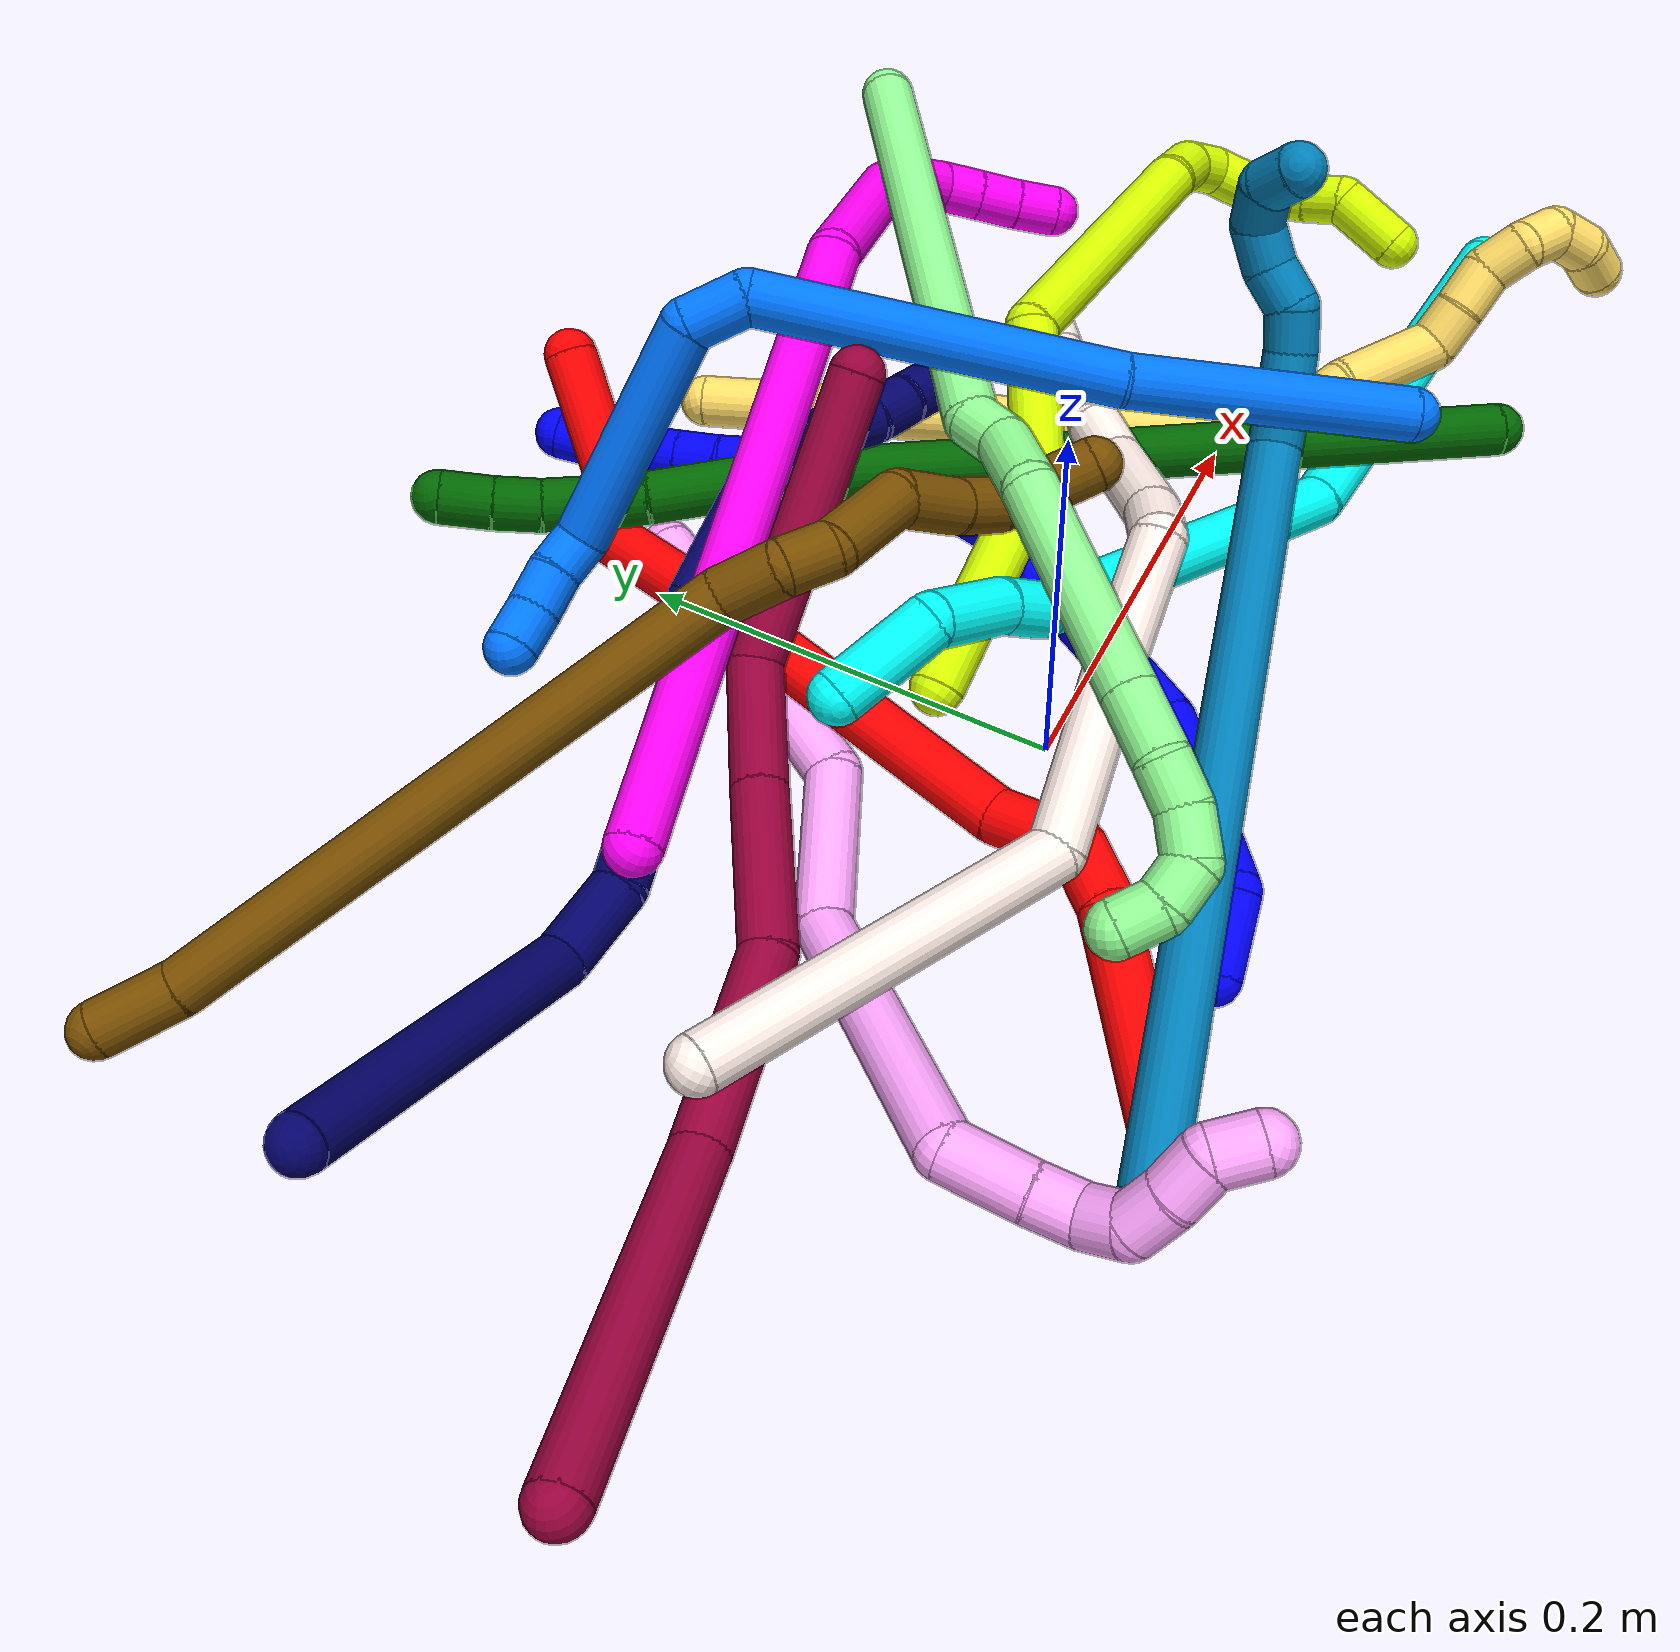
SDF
<sdf version="1.7">
 <world name="default">
  <plugin name="TubeGeneratorPlugin" filename="libtube_generator_plugin.so"/>
  <model name="photoneo_s_sensor">
   <static>1</static>
   <pose>0 0 2 1.57079 1.57079 3.14159</pose>
   <link name="link">
    <inertial><mass>0.1</mass></inertial>
    <sensor name="sensor" type="depth">
     <update_rate>30</update_rate>
     <camera>
      <horizontal_fov>1.22</horizontal_fov>
      <image><width>1920</width><height>1200</height><format>B8G8R8</format></image>
      <clip><near>0.1</near><far>4</far></clip>
      <depth_camera><output>points</output></depth_camera>
     </camera>
     <plugin name="camera_plugin" filename="libgazebo_ros_depth_camera.so">
      <baseline>0.2</baseline>
      <alwaysOn>1</alwaysOn>
      <updateRate>0.0</updateRate>
      <cameraName>camera_ir</cameraName>
      <imageTopicName>/camera/color/image_raw</imageTopicName>
      <cameraInfoTopicName>/camera/color/camera_info</cameraInfoTopicName>
      <depthImageTopicName>/camera/depth/image_raw</depthImageTopicName>
      <depthImageCameraInfoTopicName>/camera/depth/camera_info</depthImageCameraInfoTopicName>
      <pointCloudTopicName>/camera/depth/points</pointCloudTopicName>
      <frameName>fr_optical</frameName>
      <pointCloudCutoff>0.1</pointCloudCutoff>
      <pointCloudCutoffMax>2.0</pointCloudCutoffMax>
      <distortionK1>0</distortionK1>
      <distortionK2>0</distortionK2>
      <distortionK3>0</distortionK3>
      <distortionT1>0</distortionT1>
      <distortionT2>0</distortionT2>
      <CxPrime>0</CxPrime>
      <Cx>0</Cx>
      <Cy>0</Cy>
      <focalLength>0</focalLength>
      <hackBaseline>0</hackBaseline>
     </plugin>
    </sensor>
   </link>
  </model>
  <gravity>0 0 -9.8</gravity>
  <magnetic_field>6e-06 2.3e-05 -4.2e-05</magnetic_field>
  <atmosphere type="adiabatic"/>
  <physics name="default_physics" default="0" type="ode">
   <max_step_size>0.003</max_step_size>
   <real_time_factor>1</real_time_factor>
   <real_time_update_rate>1000</real_time_update_rate>
   <max_contacts>10000</max_contacts>
   <ode>
    <solver>
     <type>quick</type>
     <iters>100</iters>
     <sor>1.3</sor>
     <use_dynamic_moi_rescaling>0</use_dynamic_moi_rescaling>
    </solver>
    <constraints>
     <contact_max_correcting_vel>0</contact_max_correcting_vel>
     <contact_surface_layer>0.001</contact_surface_layer>
     <cfm>0</cfm>
     <erp>0.2</erp>
    </constraints>
   </ode>
  </physics>
  <scene><ambient>0.4 0.4 0.4 1</ambient><background>0.7 0.7 0.7 1</background><shadows>0</shadows></scene>
  <audio><device>default</device></audio>
  <spherical_coordinates>
   <surface_model>EARTH_WGS84</surface_model>
   <latitude_deg>0</latitude_deg>
   <longitude_deg>0</longitude_deg>
   <elevation>0</elevation>
   <heading_deg>0</heading_deg>
  </spherical_coordinates>
  <model name="bin">
   <static>1</static>
   <link name="bottom">
    <collision name="collision-bottom">
     <pose>0 0 -0.01 0 -0 0</pose>
     <geometry><box><size>0.8 0.6 0.02</size></box></geometry>
     <surface>
      <friction><ode><mu>100</mu><mu2>100</mu2></ode></friction>
      <contact><collide_bitmask>65535</collide_bitmask></contact>
     </surface>
    </collision>
   </link>
   <link name="west_wall">
    <collision name="collision-west_wall">
     <pose>-0.41 0 0.1 0 -0 0</pose>
     <geometry><box><size>0.02 0.6 0.2</size></box></geometry>
     <surface>
      <friction><ode><mu>100</mu><mu2>100</mu2></ode></friction>
      <contact><collide_bitmask>65535</collide_bitmask></contact>
     </surface>
    </collision>
   </link>
   <link name="east_wall">
    <collision name="collision-east_wall">
     <pose>0.41 0 0.1 0 -0 0</pose>
     <geometry><box><size>0.02 0.6 0.2</size></box></geometry>
     <surface>
      <friction><ode><mu>100</mu><mu2>100</mu2></ode></friction>
      <contact><collide_bitmask>65535</collide_bitmask></contact>
     </surface>
    </collision>
   </link>
   <link name="south_wall">
    <collision name="collision-south_wall">
     <pose>0 -0.31 0.1 0 -0 0</pose>
     <geometry><box><size>0.8 0.02 0.2</size></box></geometry>
     <surface>
      <friction><ode><mu>100</mu><mu2>100</mu2></ode></friction>
      <contact><collide_bitmask>65535</collide_bitmask></contact>
     </surface>
    </collision>
   </link>
   <link name="north_wall">
    <collision name="collision-north_wall">
     <pose>0 0.31 0.1 0 -0 0</pose>
     <geometry><box><size>0.8 0.02 0.2</size></box></geometry>
     <surface>
      <friction><ode><mu>100</mu><mu2>100</mu2></ode></friction>
      <contact><collide_bitmask>65535</collide_bitmask></contact>
     </surface>
    </collision>
   </link>
  </model>
  <model name="1">
   <static>0</static>
   <link name="1">
    <collision name="collision-cylinder-e_1_1_4">
     <pose>0.014547 0.001731 0.010417 -0.164652 0.94292 -0.084081</pose>
     <geometry><cylinder><radius>0.0125</radius><length>0.035951</length></cylinder></geometry>
     <surface>
      <friction><ode><mu>1.16</mu><mu2>1.16</mu2><slip1>0</slip1><slip2>0</slip2></ode></friction>
      <contact><ode><kp>1e+06</kp><kd>1</kd><max_vel>0</max_vel><min_depth>0.001</min_depth></ode></contact>
     </surface>
    </collision>
    <visual name="visual-cylinder-e_1_1_4">
     <pose>0.014547 0.001731 0.010417 -0.164652 0.94292 -0.084081</pose>
     <geometry><cylinder><radius>0.0125</radius><length>0.035951</length></cylinder></geometry>
     <material><ambient>0 0 1 1</ambient></material>
    </visual>
    <collision name="collision-cylinder-e_2_4_5">
     <pose>0.067886 0.036745 0.02772 -1.36675 0.851294 -0.707272</pose>
     <geometry><cylinder><radius>0.0125</radius><length>0.103152</length></cylinder></geometry>
     <surface>
      <friction><ode><mu>1.16</mu><mu2>1.16</mu2><slip1>0</slip1><slip2>0</slip2></ode></friction>
      <contact><ode><kp>1e+06</kp><kd>1</kd><max_vel>0</max_vel><min_depth>0.001</min_depth></ode></contact>
     </surface>
    </collision>
    <visual name="visual-cylinder-e_2_4_5">
     <pose>0.067886 0.036745 0.02772 -1.36675 0.851294 -0.707272</pose>
     <geometry><cylinder><radius>0.0125</radius><length>0.103152</length></cylinder></geometry>
     <material><ambient>0 0 1 1</ambient></material>
    </visual>
    <collision name="collision-cylinder-e_3_5_6">
     <pose>0.128807 0.122724 0.059596 -1.128 0.362658 -0.230909</pose>
     <geometry><cylinder><radius>0.0125</radius><length>0.124753</length></cylinder></geometry>
     <surface>
      <friction><ode><mu>1.16</mu><mu2>1.16</mu2><slip1>0</slip1><slip2>0</slip2></ode></friction>
      <contact><ode><kp>1e+06</kp><kd>1</kd><max_vel>0</max_vel><min_depth>0.001</min_depth></ode></contact>
     </surface>
    </collision>
    <visual name="visual-cylinder-e_3_5_6">
     <pose>0.128807 0.122724 0.059596 -1.128 0.362658 -0.230909</pose>
     <geometry><cylinder><radius>0.0125</radius><length>0.124753</length></cylinder></geometry>
     <material><ambient>0 0 1 1</ambient></material>
    </visual>
    <collision name="collision-cylinder-e_4_6_7">
     <pose>0.159487 0.207727 0.089319 -1.42529 0.256139 -0.221647</pose>
     <geometry><cylinder><radius>0.0125</radius><length>0.06751</length></cylinder></geometry>
     <surface>
      <friction><ode><mu>1.16</mu><mu2>1.16</mu2><slip1>0</slip1><slip2>0</slip2></ode></friction>
      <contact><ode><kp>1e+06</kp><kd>1</kd><max_vel>0</max_vel><min_depth>0.001</min_depth></ode></contact>
     </surface>
    </collision>
    <visual name="visual-cylinder-e_4_6_7">
     <pose>0.159487 0.207727 0.089319 -1.42529 0.256139 -0.221647</pose>
     <geometry><cylinder><radius>0.0125</radius><length>0.06751</length></cylinder></geometry>
     <material><ambient>0 0 1 1</ambient></material>
    </visual>
    <collision name="collision-cylinder-e_5_7_8">
     <pose>0.155161 0.263654 0.09901 -1.36393 -0.490201 0.400718</pose>
     <geometry><cylinder><radius>0.0125</radius><length>0.054706</length></cylinder></geometry>
     <surface>
      <friction><ode><mu>1.16</mu><mu2>1.16</mu2><slip1>0</slip1><slip2>0</slip2></ode></friction>
      <contact><ode><kp>1e+06</kp><kd>1</kd><max_vel>0</max_vel><min_depth>0.001</min_depth></ode></contact>
     </surface>
    </collision>
    <visual name="visual-cylinder-e_5_7_8">
     <pose>0.155161 0.263654 0.09901 -1.36393 -0.490201 0.400718</pose>
     <geometry><cylinder><radius>0.0125</radius><length>0.054706</length></cylinder></geometry>
     <material><ambient>0 0 1 1</ambient></material>
    </visual>
    <collision name="collision-cylinder-e_6_8_9">
     <pose>0.134546 0.30192 0.106939 -1.37059 -0.477641 0.392914</pose>
     <geometry><cylinder><radius>0.0125</radius><length>0.033662</length></cylinder></geometry>
     <surface>
      <friction><ode><mu>1.16</mu><mu2>1.16</mu2><slip1>0</slip1><slip2>0</slip2></ode></friction>
      <contact><ode><kp>1e+06</kp><kd>1</kd><max_vel>0</max_vel><min_depth>0.001</min_depth></ode></contact>
     </surface>
    </collision>
    <visual name="visual-cylinder-e_6_8_9">
     <pose>0.134546 0.30192 0.106939 -1.37059 -0.477641 0.392914</pose>
     <geometry><cylinder><radius>0.0125</radius><length>0.033662</length></cylinder></geometry>
     <material><ambient>0 0 1 1</ambient></material>
    </visual>
    <collision name="collision-cylinder-e_7_9_10">
     <pose>0.123809 0.326095 0.111256 -1.43054 -0.302317 0.263122</pose>
     <geometry><cylinder><radius>0.0125</radius><length>0.020156</length></cylinder></geometry>
     <surface>
      <friction><ode><mu>1.16</mu><mu2>1.16</mu2><slip1>0</slip1><slip2>0</slip2></ode></friction>
      <contact><ode><kp>1e+06</kp><kd>1</kd><max_vel>0</max_vel><min_depth>0.001</min_depth></ode></contact>
     </surface>
    </collision>
    <visual name="visual-cylinder-e_7_9_10">
     <pose>0.123809 0.326095 0.111256 -1.43054 -0.302317 0.263122</pose>
     <geometry><cylinder><radius>0.0125</radius><length>0.020156</length></cylinder></geometry>
     <material><ambient>0 0 1 1</ambient></material>
    </visual>
    <collision name="collision-cylinder-e_8_10_11">
     <pose>0.117577 0.344953 0.11421 -1.40011 -0.328832 0.277727</pose>
     <geometry><cylinder><radius>0.0125</radius><length>0.02001</length></cylinder></geometry>
     <surface>
      <friction><ode><mu>1.16</mu><mu2>1.16</mu2><slip1>0</slip1><slip2>0</slip2></ode></friction>
      <contact><ode><kp>1e+06</kp><kd>1</kd><max_vel>0</max_vel><min_depth>0.001</min_depth></ode></contact>
     </surface>
    </collision>
    <visual name="visual-cylinder-e_8_10_11">
     <pose>0.117577 0.344953 0.11421 -1.40011 -0.328832 0.277727</pose>
     <geometry><cylinder><radius>0.0125</radius><length>0.02001</length></cylinder></geometry>
     <material><ambient>0 0 1 1</ambient></material>
    </visual>
    <collision name="collision-cylinder-e_9_11_12">
     <pose>0.110504 0.36319 0.11837 -1.29174 -0.393171 0.29799</pose>
     <geometry><cylinder><radius>0.0125</radius><length>0.020058</length></cylinder></geometry>
     <surface>
      <friction><ode><mu>1.16</mu><mu2>1.16</mu2><slip1>0</slip1><slip2>0</slip2></ode></friction>
      <contact><ode><kp>1e+06</kp><kd>1</kd><max_vel>0</max_vel><min_depth>0.001</min_depth></ode></contact>
     </surface>
    </collision>
    <visual name="visual-cylinder-e_9_11_12">
     <pose>0.110504 0.36319 0.11837 -1.29174 -0.393171 0.29799</pose>
     <geometry><cylinder><radius>0.0125</radius><length>0.020058</length></cylinder></geometry>
     <material><ambient>0 0 1 1</ambient></material>
    </visual>
    <collision name="collision-cylinder-e_10_12_2">
     <pose>0.10354 0.381134 0.123916 -1.25089 -0.316839 0.229727</pose>
     <geometry><cylinder><radius>0.0125</radius><length>0.020042</length></cylinder></geometry>
     <surface>
      <friction><ode><mu>1.16</mu><mu2>1.16</mu2><slip1>0</slip1><slip2>0</slip2></ode></friction>
      <contact><ode><kp>1e+06</kp><kd>1</kd><max_vel>0</max_vel><min_depth>0.001</min_depth></ode></contact>
     </surface>
    </collision>
    <visual name="visual-cylinder-e_10_12_2">
     <pose>0.10354 0.381134 0.123916 -1.25089 -0.316839 0.229727</pose>
     <geometry><cylinder><radius>0.0125</radius><length>0.020042</length></cylinder></geometry>
     <material><ambient>0 0 1 1</ambient></material>
    </visual>
    <collision name="collision-sphere-2">
     <pose>0.100417 0.390173 0.12691 0 -0 0</pose>
     <geometry><sphere><radius>0.0125</radius></sphere></geometry>
     <surface>
      <friction><ode><mu>1.16</mu><mu2>1.16</mu2><slip1>0</slip1><slip2>0</slip2></ode></friction>
      <contact><ode><kp>1e+06</kp><kd>1</kd><max_vel>0</max_vel><min_depth>0.001</min_depth></ode></contact>
     </surface>
    </collision>
    <visual name="visual-sphere-2">
     <pose>0.100417 0.390173 0.12691 0 -0 0</pose>
     <geometry><sphere><radius>0.0125</radius></sphere></geometry>
     <material><ambient>0 0 1 1</ambient></material>
    </visual>
    <collision name="collision-sphere-12">
     <pose>0.106662 0.372095 0.120921 0 -0 0</pose>
     <geometry><sphere><radius>0.0125</radius></sphere></geometry>
     <surface>
      <friction><ode><mu>1.16</mu><mu2>1.16</mu2><slip1>0</slip1><slip2>0</slip2></ode></friction>
      <contact><ode><kp>1e+06</kp><kd>1</kd><max_vel>0</max_vel><min_depth>0.001</min_depth></ode></contact>
     </surface>
    </collision>
    <visual name="visual-sphere-12">
     <pose>0.106662 0.372095 0.120921 0 -0 0</pose>
     <geometry><sphere><radius>0.0125</radius></sphere></geometry>
     <material><ambient>0 0 1 1</ambient></material>
    </visual>
    <collision name="collision-sphere-11">
     <pose>0.114346 0.354285 0.115818 0 -0 0</pose>
     <geometry><sphere><radius>0.0125</radius></sphere></geometry>
     <surface>
      <friction><ode><mu>1.16</mu><mu2>1.16</mu2><slip1>0</slip1><slip2>0</slip2></ode></friction>
      <contact><ode><kp>1e+06</kp><kd>1</kd><max_vel>0</max_vel><min_depth>0.001</min_depth></ode></contact>
     </surface>
    </collision>
    <visual name="visual-sphere-11">
     <pose>0.114346 0.354285 0.115818 0 -0 0</pose>
     <geometry><sphere><radius>0.0125</radius></sphere></geometry>
     <material><ambient>0 0 1 1</ambient></material>
    </visual>
    <collision name="collision-sphere-10">
     <pose>0.120808 0.335622 0.112601 0 -0 0</pose>
     <geometry><sphere><radius>0.0125</radius></sphere></geometry>
     <surface>
      <friction><ode><mu>1.16</mu><mu2>1.16</mu2><slip1>0</slip1><slip2>0</slip2></ode></friction>
      <contact><ode><kp>1e+06</kp><kd>1</kd><max_vel>0</max_vel><min_depth>0.001</min_depth></ode></contact>
     </surface>
    </collision>
    <visual name="visual-sphere-10">
     <pose>0.120808 0.335622 0.112601 0 -0 0</pose>
     <geometry><sphere><radius>0.0125</radius></sphere></geometry>
     <material><ambient>0 0 1 1</ambient></material>
    </visual>
    <collision name="collision-sphere-9">
     <pose>0.126809 0.316569 0.109911 0 -0 0</pose>
     <geometry><sphere><radius>0.0125</radius></sphere></geometry>
     <surface>
      <friction><ode><mu>1.16</mu><mu2>1.16</mu2><slip1>0</slip1><slip2>0</slip2></ode></friction>
      <contact><ode><kp>1e+06</kp><kd>1</kd><max_vel>0</max_vel><min_depth>0.001</min_depth></ode></contact>
     </surface>
    </collision>
    <visual name="visual-sphere-9">
     <pose>0.126809 0.316569 0.109911 0 -0 0</pose>
     <geometry><sphere><radius>0.0125</radius></sphere></geometry>
     <material><ambient>0 0 1 1</ambient></material>
    </visual>
    <collision name="collision-sphere-4">
     <pose>0.029095 0.003462 0.020833 0 -0 0</pose>
     <geometry><sphere><radius>0.0125</radius></sphere></geometry>
     <surface>
      <friction><ode><mu>1.16</mu><mu2>1.16</mu2><slip1>0</slip1><slip2>0</slip2></ode></friction>
      <contact><ode><kp>1e+06</kp><kd>1</kd><max_vel>0</max_vel><min_depth>0.001</min_depth></ode></contact>
     </surface>
    </collision>
    <visual name="visual-sphere-4">
     <pose>0.029095 0.003462 0.020833 0 -0 0</pose>
     <geometry><sphere><radius>0.0125</radius></sphere></geometry>
     <material><ambient>0 0 1 1</ambient></material>
    </visual>
    <collision name="collision-sphere-1">
     <geometry><sphere><radius>0.0125</radius></sphere></geometry>
     <surface>
      <friction><ode><mu>1.16</mu><mu2>1.16</mu2><slip1>0</slip1><slip2>0</slip2></ode></friction>
      <contact><ode><kp>1e+06</kp><kd>1</kd><max_vel>0</max_vel><min_depth>0.001</min_depth></ode></contact>
     </surface>
    </collision>
    <visual name="visual-sphere-1">
     <geometry><sphere><radius>0.0125</radius></sphere></geometry>
     <material><ambient>0 0 1 1</ambient></material>
    </visual>
    <collision name="collision-sphere-8">
     <pose>0.142283 0.287271 0.103966 0 -0 0</pose>
     <geometry><sphere><radius>0.0125</radius></sphere></geometry>
     <surface>
      <friction><ode><mu>1.16</mu><mu2>1.16</mu2><slip1>0</slip1><slip2>0</slip2></ode></friction>
      <contact><ode><kp>1e+06</kp><kd>1</kd><max_vel>0</max_vel><min_depth>0.001</min_depth></ode></contact>
     </surface>
    </collision>
    <visual name="visual-sphere-8">
     <pose>0.142283 0.287271 0.103966 0 -0 0</pose>
     <geometry><sphere><radius>0.0125</radius></sphere></geometry>
     <material><ambient>0 0 1 1</ambient></material>
    </visual>
    <collision name="collision-sphere-5">
     <pose>0.106678 0.070029 0.034608 0 -0 0</pose>
     <geometry><sphere><radius>0.0125</radius></sphere></geometry>
     <surface>
      <friction><ode><mu>1.16</mu><mu2>1.16</mu2><slip1>0</slip1><slip2>0</slip2></ode></friction>
      <contact><ode><kp>1e+06</kp><kd>1</kd><max_vel>0</max_vel><min_depth>0.001</min_depth></ode></contact>
     </surface>
    </collision>
    <visual name="visual-sphere-5">
     <pose>0.106678 0.070029 0.034608 0 -0 0</pose>
     <geometry><sphere><radius>0.0125</radius></sphere></geometry>
     <material><ambient>0 0 1 1</ambient></material>
    </visual>
    <collision name="collision-sphere-6">
     <pose>0.150936 0.175419 0.084584 0 -0 0</pose>
     <geometry><sphere><radius>0.0125</radius></sphere></geometry>
     <surface>
      <friction><ode><mu>1.16</mu><mu2>1.16</mu2><slip1>0</slip1><slip2>0</slip2></ode></friction>
      <contact><ode><kp>1e+06</kp><kd>1</kd><max_vel>0</max_vel><min_depth>0.001</min_depth></ode></contact>
     </surface>
    </collision>
    <visual name="visual-sphere-6">
     <pose>0.150936 0.175419 0.084584 0 -0 0</pose>
     <geometry><sphere><radius>0.0125</radius></sphere></geometry>
     <material><ambient>0 0 1 1</ambient></material>
    </visual>
    <collision name="collision-sphere-7">
     <pose>0.168039 0.240036 0.094053 0 -0 0</pose>
     <geometry><sphere><radius>0.0125</radius></sphere></geometry>
     <surface>
      <friction><ode><mu>1.16</mu><mu2>1.16</mu2><slip1>0</slip1><slip2>0</slip2></ode></friction>
      <contact><ode><kp>1e+06</kp><kd>1</kd><max_vel>0</max_vel><min_depth>0.001</min_depth></ode></contact>
     </surface>
    </collision>
    <visual name="visual-sphere-7">
     <pose>0.168039 0.240036 0.094053 0 -0 0</pose>
     <geometry><sphere><radius>0.0125</radius></sphere></geometry>
     <material><ambient>0 0 1 1</ambient></material>
    </visual>
    <inertial>
     <pose>0.113038 0.172344 0.070201 0 -0 0</pose>
     <mass>0.5</mass>
     <inertia>
      <ixx>0.000185</ixx>
      <ixy>0</ixy>
      <ixz>0</ixz>
      <iyy>0.000118</iyy>
      <iyz>0</iyz>
      <izz>-0.000374</izz>
     </inertia>
    </inertial>
   </link>
   <pose>-0.081952 -0.111154 0.015054 -0.270345 0.175237 -0.089895</pose>
  </model>
  <model name="2">
   <static>0</static>
   <link name="2">
    <collision name="collision-cylinder-e_1_1_4">
     <pose>-0.01244 -0.022572 -0.020342 2.30427 -0.388569 -0.832701</pose>
     <geometry><cylinder><radius>0.0125</radius><length>0.065668</length></cylinder></geometry>
     <surface>
      <friction><ode><mu>1.16</mu><mu2>1.16</mu2><slip1>0</slip1><slip2>0</slip2></ode></friction>
      <contact><ode><kp>1e+06</kp><kd>1</kd><max_vel>0</max_vel><min_depth>0.001</min_depth></ode></contact>
     </surface>
    </collision>
    <visual name="visual-cylinder-e_1_1_4">
     <pose>-0.01244 -0.022572 -0.020342 2.30427 -0.388569 -0.832701</pose>
     <geometry><cylinder><radius>0.0125</radius><length>0.065668</length></cylinder></geometry>
     <material><ambient>1 0 0 1</ambient></material>
    </visual>
    <collision name="collision-cylinder-e_2_4_5">
     <pose>-0.023604 -0.058292 -0.049364 2.15429 0.080739 0.149849</pose>
     <geometry><cylinder><radius>0.0125</radius><length>0.031611</length></cylinder></geometry>
     <surface>
      <friction><ode><mu>1.16</mu><mu2>1.16</mu2><slip1>0</slip1><slip2>0</slip2></ode></friction>
      <contact><ode><kp>1e+06</kp><kd>1</kd><max_vel>0</max_vel><min_depth>0.001</min_depth></ode></contact>
     </surface>
    </collision>
    <visual name="visual-cylinder-e_2_4_5">
     <pose>-0.023604 -0.058292 -0.049364 2.15429 0.080739 0.149849</pose>
     <geometry><cylinder><radius>0.0125</radius><length>0.031611</length></cylinder></geometry>
     <material><ambient>1 0 0 1</ambient></material>
    </visual>
    <collision name="collision-cylinder-e_3_5_6">
     <pose>-0.013309 -0.080801 -0.096182 2.9009 0.22578 1.5063</pose>
     <geometry><cylinder><radius>0.0125</radius><length>0.080588</length></cylinder></geometry>
     <surface>
      <friction><ode><mu>1.16</mu><mu2>1.16</mu2><slip1>0</slip1><slip2>0</slip2></ode></friction>
      <contact><ode><kp>1e+06</kp><kd>1</kd><max_vel>0</max_vel><min_depth>0.001</min_depth></ode></contact>
     </surface>
    </collision>
    <visual name="visual-cylinder-e_3_5_6">
     <pose>-0.013309 -0.080801 -0.096182 2.9009 0.22578 1.5063</pose>
     <geometry><cylinder><radius>0.0125</radius><length>0.080588</length></cylinder></geometry>
     <material><ambient>1 0 0 1</ambient></material>
    </visual>
    <collision name="collision-cylinder-e_4_6_7">
     <pose>-0.007581 -0.109044 -0.209642 2.89597 -0.042378 -0.340059</pose>
     <geometry><cylinder><radius>0.0125</radius><length>0.155442</length></cylinder></geometry>
     <surface>
      <friction><ode><mu>1.16</mu><mu2>1.16</mu2><slip1>0</slip1><slip2>0</slip2></ode></friction>
      <contact><ode><kp>1e+06</kp><kd>1</kd><max_vel>0</max_vel><min_depth>0.001</min_depth></ode></contact>
     </surface>
    </collision>
    <visual name="visual-cylinder-e_4_6_7">
     <pose>-0.007581 -0.109044 -0.209642 2.89597 -0.042378 -0.340059</pose>
     <geometry><cylinder><radius>0.0125</radius><length>0.155442</length></cylinder></geometry>
     <material><ambient>1 0 0 1</ambient></material>
    </visual>
    <collision name="collision-cylinder-e_5_7_8">
     <pose>-0.005957 -0.12882 -0.304699 3.09632 0.24392 2.7763</pose>
     <geometry><cylinder><radius>0.0125</radius><length>0.040719</length></cylinder></geometry>
     <surface>
      <friction><ode><mu>1.16</mu><mu2>1.16</mu2><slip1>0</slip1><slip2>0</slip2></ode></friction>
      <contact><ode><kp>1e+06</kp><kd>1</kd><max_vel>0</max_vel><min_depth>0.001</min_depth></ode></contact>
     </surface>
    </collision>
    <visual name="visual-cylinder-e_5_7_8">
     <pose>-0.005957 -0.12882 -0.304699 3.09632 0.24392 2.7763</pose>
     <geometry><cylinder><radius>0.0125</radius><length>0.040719</length></cylinder></geometry>
     <material><ambient>1 0 0 1</ambient></material>
    </visual>
    <collision name="collision-cylinder-e_6_8_9">
     <pose>0.001335 -0.139382 -0.335799 2.43664 0.157875 0.423639</pose>
     <geometry><cylinder><radius>0.0125</radius><length>0.030216</length></cylinder></geometry>
     <surface>
      <friction><ode><mu>1.16</mu><mu2>1.16</mu2><slip1>0</slip1><slip2>0</slip2></ode></friction>
      <contact><ode><kp>1e+06</kp><kd>1</kd><max_vel>0</max_vel><min_depth>0.001</min_depth></ode></contact>
     </surface>
    </collision>
    <visual name="visual-cylinder-e_6_8_9">
     <pose>0.001335 -0.139382 -0.335799 2.43664 0.157875 0.423639</pose>
     <geometry><cylinder><radius>0.0125</radius><length>0.030216</length></cylinder></geometry>
     <material><ambient>1 0 0 1</ambient></material>
    </visual>
    <collision name="collision-cylinder-e_7_9_2">
     <pose>-0.00141 -0.187234 -0.375591 2.21076 -0.107151 -0.212755</pose>
     <geometry><cylinder><radius>0.0125</radius><length>0.095757</length></cylinder></geometry>
     <surface>
      <friction><ode><mu>1.16</mu><mu2>1.16</mu2><slip1>0</slip1><slip2>0</slip2></ode></friction>
      <contact><ode><kp>1e+06</kp><kd>1</kd><max_vel>0</max_vel><min_depth>0.001</min_depth></ode></contact>
     </surface>
    </collision>
    <visual name="visual-cylinder-e_7_9_2">
     <pose>-0.00141 -0.187234 -0.375591 2.21076 -0.107151 -0.212755</pose>
     <geometry><cylinder><radius>0.0125</radius><length>0.095757</length></cylinder></geometry>
     <material><ambient>1 0 0 1</ambient></material>
    </visual>
    <collision name="collision-sphere-2">
     <pose>-0.00653 -0.225418 -0.404018 0 -0 0</pose>
     <geometry><sphere><radius>0.0125</radius></sphere></geometry>
     <surface>
      <friction><ode><mu>1.16</mu><mu2>1.16</mu2><slip1>0</slip1><slip2>0</slip2></ode></friction>
      <contact><ode><kp>1e+06</kp><kd>1</kd><max_vel>0</max_vel><min_depth>0.001</min_depth></ode></contact>
     </surface>
    </collision>
    <visual name="visual-sphere-2">
     <pose>-0.00653 -0.225418 -0.404018 0 -0 0</pose>
     <geometry><sphere><radius>0.0125</radius></sphere></geometry>
     <material><ambient>1 0 0 1</ambient></material>
    </visual>
    <collision name="collision-sphere-9">
     <pose>0.00371 -0.14905 -0.347163 0 -0 0</pose>
     <geometry><sphere><radius>0.0125</radius></sphere></geometry>
     <surface>
      <friction><ode><mu>1.16</mu><mu2>1.16</mu2><slip1>0</slip1><slip2>0</slip2></ode></friction>
      <contact><ode><kp>1e+06</kp><kd>1</kd><max_vel>0</max_vel><min_depth>0.001</min_depth></ode></contact>
     </surface>
    </collision>
    <visual name="visual-sphere-9">
     <pose>0.00371 -0.14905 -0.347163 0 -0 0</pose>
     <geometry><sphere><radius>0.0125</radius></sphere></geometry>
     <material><ambient>1 0 0 1</ambient></material>
    </visual>
    <collision name="collision-sphere-4">
     <pose>-0.024879 -0.045145 -0.040684 0 -0 0</pose>
     <geometry><sphere><radius>0.0125</radius></sphere></geometry>
     <surface>
      <friction><ode><mu>1.16</mu><mu2>1.16</mu2><slip1>0</slip1><slip2>0</slip2></ode></friction>
      <contact><ode><kp>1e+06</kp><kd>1</kd><max_vel>0</max_vel><min_depth>0.001</min_depth></ode></contact>
     </surface>
    </collision>
    <visual name="visual-sphere-4">
     <pose>-0.024879 -0.045145 -0.040684 0 -0 0</pose>
     <geometry><sphere><radius>0.0125</radius></sphere></geometry>
     <material><ambient>1 0 0 1</ambient></material>
    </visual>
    <collision name="collision-sphere-1">
     <geometry><sphere><radius>0.0125</radius></sphere></geometry>
     <surface>
      <friction><ode><mu>1.16</mu><mu2>1.16</mu2><slip1>0</slip1><slip2>0</slip2></ode></friction>
      <contact><ode><kp>1e+06</kp><kd>1</kd><max_vel>0</max_vel><min_depth>0.001</min_depth></ode></contact>
     </surface>
    </collision>
    <visual name="visual-sphere-1">
     <geometry><sphere><radius>0.0125</radius></sphere></geometry>
     <material><ambient>1 0 0 1</ambient></material>
    </visual>
    <collision name="collision-sphere-8">
     <pose>-0.00104 -0.129714 -0.324436 0 -0 0</pose>
     <geometry><sphere><radius>0.0125</radius></sphere></geometry>
     <surface>
      <friction><ode><mu>1.16</mu><mu2>1.16</mu2><slip1>0</slip1><slip2>0</slip2></ode></friction>
      <contact><ode><kp>1e+06</kp><kd>1</kd><max_vel>0</max_vel><min_depth>0.001</min_depth></ode></contact>
     </surface>
    </collision>
    <visual name="visual-sphere-8">
     <pose>-0.00104 -0.129714 -0.324436 0 -0 0</pose>
     <geometry><sphere><radius>0.0125</radius></sphere></geometry>
     <material><ambient>1 0 0 1</ambient></material>
    </visual>
    <collision name="collision-sphere-5">
     <pose>-0.02233 -0.07144 -0.058043 0 -0 0</pose>
     <geometry><sphere><radius>0.0125</radius></sphere></geometry>
     <surface>
      <friction><ode><mu>1.16</mu><mu2>1.16</mu2><slip1>0</slip1><slip2>0</slip2></ode></friction>
      <contact><ode><kp>1e+06</kp><kd>1</kd><max_vel>0</max_vel><min_depth>0.001</min_depth></ode></contact>
     </surface>
    </collision>
    <visual name="visual-sphere-5">
     <pose>-0.02233 -0.07144 -0.058043 0 -0 0</pose>
     <geometry><sphere><radius>0.0125</radius></sphere></geometry>
     <material><ambient>1 0 0 1</ambient></material>
    </visual>
    <collision name="collision-sphere-6">
     <pose>-0.004289 -0.090162 -0.134322 0 -0 0</pose>
     <geometry><sphere><radius>0.0125</radius></sphere></geometry>
     <surface>
      <friction><ode><mu>1.16</mu><mu2>1.16</mu2><slip1>0</slip1><slip2>0</slip2></ode></friction>
      <contact><ode><kp>1e+06</kp><kd>1</kd><max_vel>0</max_vel><min_depth>0.001</min_depth></ode></contact>
     </surface>
    </collision>
    <visual name="visual-sphere-6">
     <pose>-0.004289 -0.090162 -0.134322 0 -0 0</pose>
     <geometry><sphere><radius>0.0125</radius></sphere></geometry>
     <material><ambient>1 0 0 1</ambient></material>
    </visual>
    <collision name="collision-sphere-7">
     <pose>-0.010874 -0.127926 -0.284963 0 -0 0</pose>
     <geometry><sphere><radius>0.0125</radius></sphere></geometry>
     <surface>
      <friction><ode><mu>1.16</mu><mu2>1.16</mu2><slip1>0</slip1><slip2>0</slip2></ode></friction>
      <contact><ode><kp>1e+06</kp><kd>1</kd><max_vel>0</max_vel><min_depth>0.001</min_depth></ode></contact>
     </surface>
    </collision>
    <visual name="visual-sphere-7">
     <pose>-0.010874 -0.127926 -0.284963 0 -0 0</pose>
     <geometry><sphere><radius>0.0125</radius></sphere></geometry>
     <material><ambient>1 0 0 1</ambient></material>
    </visual>
    <inertial>
     <pose>-0.008303 -0.108345 -0.203507 0 -0 0</pose>
     <mass>0.5</mass>
     <inertia>
      <ixx>0.000304</ixx>
      <ixy>0</ixy>
      <ixz>0</ixz>
      <iyy>-0.000447</iyy>
      <iyz>0</iyz>
      <izz>0.00016</izz>
     </inertia>
    </inertial>
   </link>
   <pose>0.066034 0.281114 0.063148 1.75191 -1.26348 2.94481</pose>
  </model>
  <model name="3">
   <static>0</static>
   <link name="3">
    <collision name="collision-cylinder-e_1_1_4">
     <pose>-0.071297 0.021151 -0.065256 -2.82815 -0.804683 2.43051</pose>
     <geometry><cylinder><radius>0.0125</radius><length>0.197879</length></cylinder></geometry>
     <surface>
      <friction><ode><mu>1.16</mu><mu2>1.16</mu2><slip1>0</slip1><slip2>0</slip2></ode></friction>
      <contact><ode><kp>1e+06</kp><kd>1</kd><max_vel>0</max_vel><min_depth>0.001</min_depth></ode></contact>
     </surface>
    </collision>
    <visual name="visual-cylinder-e_1_1_4">
     <pose>-0.071297 0.021151 -0.065256 -2.82815 -0.804683 2.43051</pose>
     <geometry><cylinder><radius>0.0125</radius><length>0.197879</length></cylinder></geometry>
     <material><ambient>0.003922 1 0.996078 1</ambient></material>
    </visual>
    <collision name="collision-cylinder-e_2_4_5">
     <pose>-0.219362 0.02534 -0.177843 2.79746 -0.990959 -2.51936</pose>
     <geometry><cylinder><radius>0.0125</radius><length>0.183535</length></cylinder></geometry>
     <surface>
      <friction><ode><mu>1.16</mu><mu2>1.16</mu2><slip1>0</slip1><slip2>0</slip2></ode></friction>
      <contact><ode><kp>1e+06</kp><kd>1</kd><max_vel>0</max_vel><min_depth>0.001</min_depth></ode></contact>
     </surface>
    </collision>
    <visual name="visual-cylinder-e_2_4_5">
     <pose>-0.219362 0.02534 -0.177843 2.79746 -0.990959 -2.51936</pose>
     <geometry><cylinder><radius>0.0125</radius><length>0.183535</length></cylinder></geometry>
     <material><ambient>0.003922 1 0.996078 1</ambient></material>
    </visual>
    <collision name="collision-cylinder-e_3_5_6">
     <pose>-0.305555 0.001504 -0.230858 2.26185 -0.812927 -1.48165</pose>
     <geometry><cylinder><radius>0.0125</radius><length>0.025951</length></cylinder></geometry>
     <surface>
      <friction><ode><mu>1.16</mu><mu2>1.16</mu2><slip1>0</slip1><slip2>0</slip2></ode></friction>
      <contact><ode><kp>1e+06</kp><kd>1</kd><max_vel>0</max_vel><min_depth>0.001</min_depth></ode></contact>
     </surface>
    </collision>
    <visual name="visual-cylinder-e_3_5_6">
     <pose>-0.305555 0.001504 -0.230858 2.26185 -0.812927 -1.48165</pose>
     <geometry><cylinder><radius>0.0125</radius><length>0.025951</length></cylinder></geometry>
     <material><ambient>0.003922 1 0.996078 1</ambient></material>
    </visual>
    <collision name="collision-cylinder-e_4_6_7">
     <pose>-0.33101 -0.012935 -0.248658 2.58334 -0.842978 -2.00405</pose>
     <geometry><cylinder><radius>0.0125</radius><length>0.042944</length></cylinder></geometry>
     <surface>
      <friction><ode><mu>1.16</mu><mu2>1.16</mu2><slip1>0</slip1><slip2>0</slip2></ode></friction>
      <contact><ode><kp>1e+06</kp><kd>1</kd><max_vel>0</max_vel><min_depth>0.001</min_depth></ode></contact>
     </surface>
    </collision>
    <visual name="visual-cylinder-e_4_6_7">
     <pose>-0.33101 -0.012935 -0.248658 2.58334 -0.842978 -2.00405</pose>
     <geometry><cylinder><radius>0.0125</radius><length>0.042944</length></cylinder></geometry>
     <material><ambient>0.003922 1 0.996078 1</ambient></material>
    </visual>
    <collision name="collision-cylinder-e_5_7_2">
     <pose>-0.36965 -0.013326 -0.268169 -2.37133 -1.14314 2.01685</pose>
     <geometry><cylinder><radius>0.0125</radius><length>0.049691</length></cylinder></geometry>
     <surface>
      <friction><ode><mu>1.16</mu><mu2>1.16</mu2><slip1>0</slip1><slip2>0</slip2></ode></friction>
      <contact><ode><kp>1e+06</kp><kd>1</kd><max_vel>0</max_vel><min_depth>0.001</min_depth></ode></contact>
     </surface>
    </collision>
    <visual name="visual-cylinder-e_5_7_2">
     <pose>-0.36965 -0.013326 -0.268169 -2.37133 -1.14314 2.01685</pose>
     <geometry><cylinder><radius>0.0125</radius><length>0.049691</length></cylinder></geometry>
     <material><ambient>0.003922 1 0.996078 1</ambient></material>
    </visual>
    <collision name="collision-sphere-2">
     <pose>-0.392258 -0.006151 -0.275565 0 -0 0</pose>
     <geometry><sphere><radius>0.0125</radius></sphere></geometry>
     <surface>
      <friction><ode><mu>1.16</mu><mu2>1.16</mu2><slip1>0</slip1><slip2>0</slip2></ode></friction>
      <contact><ode><kp>1e+06</kp><kd>1</kd><max_vel>0</max_vel><min_depth>0.001</min_depth></ode></contact>
     </surface>
    </collision>
    <visual name="visual-sphere-2">
     <pose>-0.392258 -0.006151 -0.275565 0 -0 0</pose>
     <geometry><sphere><radius>0.0125</radius></sphere></geometry>
     <material><ambient>0.003922 1 0.996078 1</ambient></material>
    </visual>
    <collision name="collision-sphere-7">
     <pose>-0.347042 -0.020501 -0.260774 0 -0 0</pose>
     <geometry><sphere><radius>0.0125</radius></sphere></geometry>
     <surface>
      <friction><ode><mu>1.16</mu><mu2>1.16</mu2><slip1>0</slip1><slip2>0</slip2></ode></friction>
      <contact><ode><kp>1e+06</kp><kd>1</kd><max_vel>0</max_vel><min_depth>0.001</min_depth></ode></contact>
     </surface>
    </collision>
    <visual name="visual-sphere-7">
     <pose>-0.347042 -0.020501 -0.260774 0 -0 0</pose>
     <geometry><sphere><radius>0.0125</radius></sphere></geometry>
     <material><ambient>0.003922 1 0.996078 1</ambient></material>
    </visual>
    <collision name="collision-sphere-6">
     <pose>-0.314979 -0.005369 -0.236543 0 -0 0</pose>
     <geometry><sphere><radius>0.0125</radius></sphere></geometry>
     <surface>
      <friction><ode><mu>1.16</mu><mu2>1.16</mu2><slip1>0</slip1><slip2>0</slip2></ode></friction>
      <contact><ode><kp>1e+06</kp><kd>1</kd><max_vel>0</max_vel><min_depth>0.001</min_depth></ode></contact>
     </surface>
    </collision>
    <visual name="visual-sphere-6">
     <pose>-0.314979 -0.005369 -0.236543 0 -0 0</pose>
     <geometry><sphere><radius>0.0125</radius></sphere></geometry>
     <material><ambient>0.003922 1 0.996078 1</ambient></material>
    </visual>
    <collision name="collision-sphere-5">
     <pose>-0.296131 0.008377 -0.225174 0 -0 0</pose>
     <geometry><sphere><radius>0.0125</radius></sphere></geometry>
     <surface>
      <friction><ode><mu>1.16</mu><mu2>1.16</mu2><slip1>0</slip1><slip2>0</slip2></ode></friction>
      <contact><ode><kp>1e+06</kp><kd>1</kd><max_vel>0</max_vel><min_depth>0.001</min_depth></ode></contact>
     </surface>
    </collision>
    <visual name="visual-sphere-5">
     <pose>-0.296131 0.008377 -0.225174 0 -0 0</pose>
     <geometry><sphere><radius>0.0125</radius></sphere></geometry>
     <material><ambient>0.003922 1 0.996078 1</ambient></material>
    </visual>
    <collision name="collision-sphere-1">
     <geometry><sphere><radius>0.0125</radius></sphere></geometry>
     <surface>
      <friction><ode><mu>1.16</mu><mu2>1.16</mu2><slip1>0</slip1><slip2>0</slip2></ode></friction>
      <contact><ode><kp>1e+06</kp><kd>1</kd><max_vel>0</max_vel><min_depth>0.001</min_depth></ode></contact>
     </surface>
    </collision>
    <visual name="visual-sphere-1">
     <geometry><sphere><radius>0.0125</radius></sphere></geometry>
     <material><ambient>0.003922 1 0.996078 1</ambient></material>
    </visual>
    <collision name="collision-sphere-4">
     <pose>-0.142594 0.042303 -0.130513 0 -0 0</pose>
     <geometry><sphere><radius>0.0125</radius></sphere></geometry>
     <surface>
      <friction><ode><mu>1.16</mu><mu2>1.16</mu2><slip1>0</slip1><slip2>0</slip2></ode></friction>
      <contact><ode><kp>1e+06</kp><kd>1</kd><max_vel>0</max_vel><min_depth>0.001</min_depth></ode></contact>
     </surface>
    </collision>
    <visual name="visual-sphere-4">
     <pose>-0.142594 0.042303 -0.130513 0 -0 0</pose>
     <geometry><sphere><radius>0.0125</radius></sphere></geometry>
     <material><ambient>0.003922 1 0.996078 1</ambient></material>
    </visual>
    <inertial>
     <pose>-0.189763 0.015315 -0.151097 0 -0 0</pose>
     <mass>0.5</mass>
     <inertia>
      <ixx>-0.000484</ixx>
      <ixy>0</ixy>
      <ixz>0</ixz>
      <iyy>0.001195</iyy>
      <iyz>0</iyz>
      <izz>0.000863</izz>
     </inertia>
    </inertial>
   </link>
   <pose>0.380726 -0.077654 0.012695 -1.98545 -0.105315 -0.859708</pose>
  </model>
  <model name="4">
   <static>0</static>
   <link name="4">
    <collision name="collision-cylinder-e_1_1_4">
     <pose>-0.048879 -0.060165 -0.005111 1.65554 -0.680503 -0.735655</pose>
     <geometry><cylinder><radius>0.0125</radius><length>0.155373</length></cylinder></geometry>
     <surface>
      <friction><ode><mu>1.16</mu><mu2>1.16</mu2><slip1>0</slip1><slip2>0</slip2></ode></friction>
      <contact><ode><kp>1e+06</kp><kd>1</kd><max_vel>0</max_vel><min_depth>0.001</min_depth></ode></contact>
     </surface>
    </collision>
    <visual name="visual-cylinder-e_1_1_4">
     <pose>-0.048879 -0.060165 -0.005111 1.65554 -0.680503 -0.735655</pose>
     <geometry><cylinder><radius>0.0125</radius><length>0.155373</length></cylinder></geometry>
     <material><ambient>1 0.65098 0.996078 1</ambient></material>
    </visual>
    <collision name="collision-cylinder-e_2_4_5">
     <pose>-0.127673 -0.134812 -0.027536 2.44508 -0.924397 -1.88207</pose>
     <geometry><cylinder><radius>0.0125</radius><length>0.074952</length></cylinder></geometry>
     <surface>
      <friction><ode><mu>1.16</mu><mu2>1.16</mu2><slip1>0</slip1><slip2>0</slip2></ode></friction>
      <contact><ode><kp>1e+06</kp><kd>1</kd><max_vel>0</max_vel><min_depth>0.001</min_depth></ode></contact>
     </surface>
    </collision>
    <visual name="visual-cylinder-e_2_4_5">
     <pose>-0.127673 -0.134812 -0.027536 2.44508 -0.924397 -1.88207</pose>
     <geometry><cylinder><radius>0.0125</radius><length>0.074952</length></cylinder></geometry>
     <material><ambient>1 0.65098 0.996078 1</ambient></material>
    </visual>
    <collision name="collision-cylinder-e_3_5_6">
     <pose>-0.212243 -0.186493 -0.041721 1.48684 -0.97155 -0.90381</pose>
     <geometry><cylinder><radius>0.0125</radius><length>0.132373</length></cylinder></geometry>
     <surface>
      <friction><ode><mu>1.16</mu><mu2>1.16</mu2><slip1>0</slip1><slip2>0</slip2></ode></friction>
      <contact><ode><kp>1e+06</kp><kd>1</kd><max_vel>0</max_vel><min_depth>0.001</min_depth></ode></contact>
     </surface>
    </collision>
    <visual name="visual-cylinder-e_3_5_6">
     <pose>-0.212243 -0.186493 -0.041721 1.48684 -0.97155 -0.90381</pose>
     <geometry><cylinder><radius>0.0125</radius><length>0.132373</length></cylinder></geometry>
     <material><ambient>1 0.65098 0.996078 1</ambient></material>
    </visual>
    <collision name="collision-cylinder-e_4_6_7">
     <pose>-0.270719 -0.240574 -0.03458 1.33757 -0.216778 -0.171567</pose>
     <geometry><cylinder><radius>0.0125</radius><length>0.035536</length></cylinder></geometry>
     <surface>
      <friction><ode><mu>1.16</mu><mu2>1.16</mu2><slip1>0</slip1><slip2>0</slip2></ode></friction>
      <contact><ode><kp>1e+06</kp><kd>1</kd><max_vel>0</max_vel><min_depth>0.001</min_depth></ode></contact>
     </surface>
    </collision>
    <visual name="visual-cylinder-e_4_6_7">
     <pose>-0.270719 -0.240574 -0.03458 1.33757 -0.216778 -0.171567</pose>
     <geometry><cylinder><radius>0.0125</radius><length>0.035536</length></cylinder></geometry>
     <material><ambient>1 0.65098 0.996078 1</ambient></material>
    </visual>
    <collision name="collision-cylinder-e_5_7_8">
     <pose>-0.27598 -0.267486 -0.028093 1.3288 -0.138508 -0.108543</pose>
     <geometry><cylinder><radius>0.0125</radius><length>0.020861</length></cylinder></geometry>
     <surface>
      <friction><ode><mu>1.16</mu><mu2>1.16</mu2><slip1>0</slip1><slip2>0</slip2></ode></friction>
      <contact><ode><kp>1e+06</kp><kd>1</kd><max_vel>0</max_vel><min_depth>0.001</min_depth></ode></contact>
     </surface>
    </collision>
    <visual name="visual-cylinder-e_5_7_8">
     <pose>-0.27598 -0.267486 -0.028093 1.3288 -0.138508 -0.108543</pose>
     <geometry><cylinder><radius>0.0125</radius><length>0.020861</length></cylinder></geometry>
     <material><ambient>1 0.65098 0.996078 1</ambient></material>
    </visual>
    <collision name="collision-cylinder-e_6_8_9">
     <pose>-0.282626 -0.283927 -0.019489 0.807935 -0.530691 -0.2313</pose>
     <geometry><cylinder><radius>0.0125</radius><length>0.02057</length></cylinder></geometry>
     <surface>
      <friction><ode><mu>1.16</mu><mu2>1.16</mu2><slip1>0</slip1><slip2>0</slip2></ode></friction>
      <contact><ode><kp>1e+06</kp><kd>1</kd><max_vel>0</max_vel><min_depth>0.001</min_depth></ode></contact>
     </surface>
    </collision>
    <visual name="visual-cylinder-e_6_8_9">
     <pose>-0.282626 -0.283927 -0.019489 0.807935 -0.530691 -0.2313</pose>
     <geometry><cylinder><radius>0.0125</radius><length>0.02057</length></cylinder></geometry>
     <material><ambient>1 0.65098 0.996078 1</ambient></material>
    </visual>
    <collision name="collision-cylinder-e_7_9_10">
     <pose>-0.288151 -0.292734 -0.003563 0.239758 -0.031671 -0.003815</pose>
     <geometry><cylinder><radius>0.0125</radius><length>0.020179</length></cylinder></geometry>
     <surface>
      <friction><ode><mu>1.16</mu><mu2>1.16</mu2><slip1>0</slip1><slip2>0</slip2></ode></friction>
      <contact><ode><kp>1e+06</kp><kd>1</kd><max_vel>0</max_vel><min_depth>0.001</min_depth></ode></contact>
     </surface>
    </collision>
    <visual name="visual-cylinder-e_7_9_10">
     <pose>-0.288151 -0.292734 -0.003563 0.239758 -0.031671 -0.003815</pose>
     <geometry><cylinder><radius>0.0125</radius><length>0.020179</length></cylinder></geometry>
     <material><ambient>1 0.65098 0.996078 1</ambient></material>
    </visual>
    <collision name="collision-cylinder-e_8_10_11">
     <pose>-0.287476 -0.296433 0.016108 0.131386 0.099515 0.006552</pose>
     <geometry><cylinder><radius>0.0125</radius><length>0.02002</length></cylinder></geometry>
     <surface>
      <friction><ode><mu>1.16</mu><mu2>1.16</mu2><slip1>0</slip1><slip2>0</slip2></ode></friction>
      <contact><ode><kp>1e+06</kp><kd>1</kd><max_vel>0</max_vel><min_depth>0.001</min_depth></ode></contact>
     </surface>
    </collision>
    <visual name="visual-cylinder-e_8_10_11">
     <pose>-0.287476 -0.296433 0.016108 0.131386 0.099515 0.006552</pose>
     <geometry><cylinder><radius>0.0125</radius><length>0.02002</length></cylinder></geometry>
     <material><ambient>1 0.65098 0.996078 1</ambient></material>
    </visual>
    <collision name="collision-cylinder-e_9_11_2">
     <pose>-0.284154 -0.304719 0.032855 0.793233 0.233242 0.098051</pose>
     <geometry><cylinder><radius>0.0125</radius><length>0.020137</length></cylinder></geometry>
     <surface>
      <friction><ode><mu>1.16</mu><mu2>1.16</mu2><slip1>0</slip1><slip2>0</slip2></ode></friction>
      <contact><ode><kp>1e+06</kp><kd>1</kd><max_vel>0</max_vel><min_depth>0.001</min_depth></ode></contact>
     </surface>
    </collision>
    <visual name="visual-cylinder-e_9_11_2">
     <pose>-0.284154 -0.304719 0.032855 0.793233 0.233242 0.098051</pose>
     <geometry><cylinder><radius>0.0125</radius><length>0.020137</length></cylinder></geometry>
     <material><ambient>1 0.65098 0.996078 1</ambient></material>
    </visual>
    <collision name="collision-sphere-2">
     <pose>-0.281827 -0.3117 0.039727 0 -0 0</pose>
     <geometry><sphere><radius>0.0125</radius></sphere></geometry>
     <surface>
      <friction><ode><mu>1.16</mu><mu2>1.16</mu2><slip1>0</slip1><slip2>0</slip2></ode></friction>
      <contact><ode><kp>1e+06</kp><kd>1</kd><max_vel>0</max_vel><min_depth>0.001</min_depth></ode></contact>
     </surface>
    </collision>
    <visual name="visual-sphere-2">
     <pose>-0.281827 -0.3117 0.039727 0 -0 0</pose>
     <geometry><sphere><radius>0.0125</radius></sphere></geometry>
     <material><ambient>1 0.65098 0.996078 1</ambient></material>
    </visual>
    <collision name="collision-sphere-11">
     <pose>-0.286481 -0.297738 0.025982 0 -0 0</pose>
     <geometry><sphere><radius>0.0125</radius></sphere></geometry>
     <surface>
      <friction><ode><mu>1.16</mu><mu2>1.16</mu2><slip1>0</slip1><slip2>0</slip2></ode></friction>
      <contact><ode><kp>1e+06</kp><kd>1</kd><max_vel>0</max_vel><min_depth>0.001</min_depth></ode></contact>
     </surface>
    </collision>
    <visual name="visual-sphere-11">
     <pose>-0.286481 -0.297738 0.025982 0 -0 0</pose>
     <geometry><sphere><radius>0.0125</radius></sphere></geometry>
     <material><ambient>1 0.65098 0.996078 1</ambient></material>
    </visual>
    <collision name="collision-sphere-10">
     <pose>-0.28847 -0.295128 0.006233 0 -0 0</pose>
     <geometry><sphere><radius>0.0125</radius></sphere></geometry>
     <surface>
      <friction><ode><mu>1.16</mu><mu2>1.16</mu2><slip1>0</slip1><slip2>0</slip2></ode></friction>
      <contact><ode><kp>1e+06</kp><kd>1</kd><max_vel>0</max_vel><min_depth>0.001</min_depth></ode></contact>
     </surface>
    </collision>
    <visual name="visual-sphere-10">
     <pose>-0.28847 -0.295128 0.006233 0 -0 0</pose>
     <geometry><sphere><radius>0.0125</radius></sphere></geometry>
     <material><ambient>1 0.65098 0.996078 1</ambient></material>
    </visual>
    <collision name="collision-sphere-9">
     <pose>-0.287831 -0.290339 -0.013359 0 -0 0</pose>
     <geometry><sphere><radius>0.0125</radius></sphere></geometry>
     <surface>
      <friction><ode><mu>1.16</mu><mu2>1.16</mu2><slip1>0</slip1><slip2>0</slip2></ode></friction>
      <contact><ode><kp>1e+06</kp><kd>1</kd><max_vel>0</max_vel><min_depth>0.001</min_depth></ode></contact>
     </surface>
    </collision>
    <visual name="visual-sphere-9">
     <pose>-0.287831 -0.290339 -0.013359 0 -0 0</pose>
     <geometry><sphere><radius>0.0125</radius></sphere></geometry>
     <material><ambient>1 0.65098 0.996078 1</ambient></material>
    </visual>
    <collision name="collision-sphere-4">
     <pose>-0.097758 -0.120331 -0.010221 0 -0 0</pose>
     <geometry><sphere><radius>0.0125</radius></sphere></geometry>
     <surface>
      <friction><ode><mu>1.16</mu><mu2>1.16</mu2><slip1>0</slip1><slip2>0</slip2></ode></friction>
      <contact><ode><kp>1e+06</kp><kd>1</kd><max_vel>0</max_vel><min_depth>0.001</min_depth></ode></contact>
     </surface>
    </collision>
    <visual name="visual-sphere-4">
     <pose>-0.097758 -0.120331 -0.010221 0 -0 0</pose>
     <geometry><sphere><radius>0.0125</radius></sphere></geometry>
     <material><ambient>1 0.65098 0.996078 1</ambient></material>
    </visual>
    <collision name="collision-sphere-1">
     <geometry><sphere><radius>0.0125</radius></sphere></geometry>
     <surface>
      <friction><ode><mu>1.16</mu><mu2>1.16</mu2><slip1>0</slip1><slip2>0</slip2></ode></friction>
      <contact><ode><kp>1e+06</kp><kd>1</kd><max_vel>0</max_vel><min_depth>0.001</min_depth></ode></contact>
     </surface>
    </collision>
    <visual name="visual-sphere-1">
     <geometry><sphere><radius>0.0125</radius></sphere></geometry>
     <material><ambient>1 0.65098 0.996078 1</ambient></material>
    </visual>
    <collision name="collision-sphere-8">
     <pose>-0.27742 -0.277515 -0.025618 0 -0 0</pose>
     <geometry><sphere><radius>0.0125</radius></sphere></geometry>
     <surface>
      <friction><ode><mu>1.16</mu><mu2>1.16</mu2><slip1>0</slip1><slip2>0</slip2></ode></friction>
      <contact><ode><kp>1e+06</kp><kd>1</kd><max_vel>0</max_vel><min_depth>0.001</min_depth></ode></contact>
     </surface>
    </collision>
    <visual name="visual-sphere-8">
     <pose>-0.27742 -0.277515 -0.025618 0 -0 0</pose>
     <geometry><sphere><radius>0.0125</radius></sphere></geometry>
     <material><ambient>1 0.65098 0.996078 1</ambient></material>
    </visual>
    <collision name="collision-sphere-5">
     <pose>-0.157589 -0.149294 -0.044851 0 -0 0</pose>
     <geometry><sphere><radius>0.0125</radius></sphere></geometry>
     <surface>
      <friction><ode><mu>1.16</mu><mu2>1.16</mu2><slip1>0</slip1><slip2>0</slip2></ode></friction>
      <contact><ode><kp>1e+06</kp><kd>1</kd><max_vel>0</max_vel><min_depth>0.001</min_depth></ode></contact>
     </surface>
    </collision>
    <visual name="visual-sphere-5">
     <pose>-0.157589 -0.149294 -0.044851 0 -0 0</pose>
     <geometry><sphere><radius>0.0125</radius></sphere></geometry>
     <material><ambient>1 0.65098 0.996078 1</ambient></material>
    </visual>
    <collision name="collision-sphere-6">
     <pose>-0.266897 -0.223692 -0.03859 0 -0 0</pose>
     <geometry><sphere><radius>0.0125</radius></sphere></geometry>
     <surface>
      <friction><ode><mu>1.16</mu><mu2>1.16</mu2><slip1>0</slip1><slip2>0</slip2></ode></friction>
      <contact><ode><kp>1e+06</kp><kd>1</kd><max_vel>0</max_vel><min_depth>0.001</min_depth></ode></contact>
     </surface>
    </collision>
    <visual name="visual-sphere-6">
     <pose>-0.266897 -0.223692 -0.03859 0 -0 0</pose>
     <geometry><sphere><radius>0.0125</radius></sphere></geometry>
     <material><ambient>1 0.65098 0.996078 1</ambient></material>
    </visual>
    <collision name="collision-sphere-7">
     <pose>-0.27454 -0.257456 -0.030569 0 -0 0</pose>
     <geometry><sphere><radius>0.0125</radius></sphere></geometry>
     <surface>
      <friction><ode><mu>1.16</mu><mu2>1.16</mu2><slip1>0</slip1><slip2>0</slip2></ode></friction>
      <contact><ode><kp>1e+06</kp><kd>1</kd><max_vel>0</max_vel><min_depth>0.001</min_depth></ode></contact>
     </surface>
    </collision>
    <visual name="visual-sphere-7">
     <pose>-0.27454 -0.257456 -0.030569 0 -0 0</pose>
     <geometry><sphere><radius>0.0125</radius></sphere></geometry>
     <material><ambient>1 0.65098 0.996078 1</ambient></material>
    </visual>
    <inertial>
     <pose>-0.167484 -0.164172 -0.019368 0 -0 0</pose>
     <mass>0.5</mass>
     <inertia>
      <ixx>-4.1e-05</ixx>
      <ixy>0</ixy>
      <ixz>0</ixz>
      <iyy>-1.5e-05</iyy>
      <iyz>0</iyz>
      <izz>0.000781</izz>
     </inertia>
    </inertial>
   </link>
   <pose>0.019914 0.205654 0.011478 0.43124 0.579609 0.273857</pose>
  </model>
  <model name="5">
   <static>0</static>
   <link name="5">
    <collision name="collision-cylinder-e_1_1_4">
     <pose>0.048866 -0.118893 -0.051718 1.9811 0.360432 0.542189</pose>
     <geometry><cylinder><radius>0.0125</radius><length>0.277115</length></cylinder></geometry>
     <surface>
      <friction><ode><mu>1.16</mu><mu2>1.16</mu2><slip1>0</slip1><slip2>0</slip2></ode></friction>
      <contact><ode><kp>1e+06</kp><kd>1</kd><max_vel>0</max_vel><min_depth>0.001</min_depth></ode></contact>
     </surface>
    </collision>
    <visual name="visual-cylinder-e_1_1_4">
     <pose>0.048866 -0.118893 -0.051718 1.9811 0.360432 0.542189</pose>
     <geometry><cylinder><radius>0.0125</radius><length>0.277115</length></cylinder></geometry>
     <material><ambient>1 0.858824 0.4 1</ambient></material>
    </visual>
    <collision name="collision-cylinder-e_2_4_5">
     <pose>0.112875 -0.255121 -0.097733 1.25296 0.692608 0.510905</pose>
     <geometry><cylinder><radius>0.0125</radius><length>0.047427</length></cylinder></geometry>
     <surface>
      <friction><ode><mu>1.16</mu><mu2>1.16</mu2><slip1>0</slip1><slip2>0</slip2></ode></friction>
      <contact><ode><kp>1e+06</kp><kd>1</kd><max_vel>0</max_vel><min_depth>0.001</min_depth></ode></contact>
     </surface>
    </collision>
    <visual name="visual-cylinder-e_2_4_5">
     <pose>0.112875 -0.255121 -0.097733 1.25296 0.692608 0.510905</pose>
     <geometry><cylinder><radius>0.0125</radius><length>0.047427</length></cylinder></geometry>
     <material><ambient>1 0.858824 0.4 1</ambient></material>
    </visual>
    <collision name="collision-cylinder-e_3_5_6">
     <pose>0.146227 -0.289789 -0.091537 1.54237 0.809884 0.789495</pose>
     <geometry><cylinder><radius>0.0125</radius><length>0.05029</length></cylinder></geometry>
     <surface>
      <friction><ode><mu>1.16</mu><mu2>1.16</mu2><slip1>0</slip1><slip2>0</slip2></ode></friction>
      <contact><ode><kp>1e+06</kp><kd>1</kd><max_vel>0</max_vel><min_depth>0.001</min_depth></ode></contact>
     </surface>
    </collision>
    <visual name="visual-cylinder-e_3_5_6">
     <pose>0.146227 -0.289789 -0.091537 1.54237 0.809884 0.789495</pose>
     <geometry><cylinder><radius>0.0125</radius><length>0.05029</length></cylinder></geometry>
     <material><ambient>1 0.858824 0.4 1</ambient></material>
    </visual>
    <collision name="collision-cylinder-e_4_6_7">
     <pose>0.168716 -0.314576 -0.084734 0.868352 0.412959 0.193644</pose>
     <geometry><cylinder><radius>0.0125</radius><length>0.021326</length></cylinder></geometry>
     <surface>
      <friction><ode><mu>1.16</mu><mu2>1.16</mu2><slip1>0</slip1><slip2>0</slip2></ode></friction>
      <contact><ode><kp>1e+06</kp><kd>1</kd><max_vel>0</max_vel><min_depth>0.001</min_depth></ode></contact>
     </surface>
    </collision>
    <visual name="visual-cylinder-e_4_6_7">
     <pose>0.168716 -0.314576 -0.084734 0.868352 0.412959 0.193644</pose>
     <geometry><cylinder><radius>0.0125</radius><length>0.021326</length></cylinder></geometry>
     <material><ambient>1 0.858824 0.4 1</ambient></material>
    </visual>
    <collision name="collision-cylinder-e_5_7_8">
     <pose>0.178813 -0.329124 -0.07191 0.827986 0.543462 0.243634</pose>
     <geometry><cylinder><radius>0.0125</radius><length>0.022501</length></cylinder></geometry>
     <surface>
      <friction><ode><mu>1.16</mu><mu2>1.16</mu2><slip1>0</slip1><slip2>0</slip2></ode></friction>
      <contact><ode><kp>1e+06</kp><kd>1</kd><max_vel>0</max_vel><min_depth>0.001</min_depth></ode></contact>
     </surface>
    </collision>
    <visual name="visual-cylinder-e_5_7_8">
     <pose>0.178813 -0.329124 -0.07191 0.827986 0.543462 0.243634</pose>
     <geometry><cylinder><radius>0.0125</radius><length>0.022501</length></cylinder></geometry>
     <material><ambient>1 0.858824 0.4 1</ambient></material>
    </visual>
    <collision name="collision-cylinder-e_6_8_9">
     <pose>0.188314 -0.345702 -0.062363 1.2612 0.354235 0.259869</pose>
     <geometry><cylinder><radius>0.0125</radius><length>0.021236</length></cylinder></geometry>
     <surface>
      <friction><ode><mu>1.16</mu><mu2>1.16</mu2><slip1>0</slip1><slip2>0</slip2></ode></friction>
      <contact><ode><kp>1e+06</kp><kd>1</kd><max_vel>0</max_vel><min_depth>0.001</min_depth></ode></contact>
     </surface>
    </collision>
    <visual name="visual-cylinder-e_6_8_9">
     <pose>0.188314 -0.345702 -0.062363 1.2612 0.354235 0.259869</pose>
     <geometry><cylinder><radius>0.0125</radius><length>0.021236</length></cylinder></geometry>
     <material><ambient>1 0.858824 0.4 1</ambient></material>
    </visual>
    <collision name="collision-cylinder-e_7_9_10">
     <pose>0.200287 -0.360803 -0.059203 1.54835 0.97528 0.956815</pose>
     <geometry><cylinder><radius>0.0125</radius><length>0.020027</length></cylinder></geometry>
     <surface>
      <friction><ode><mu>1.16</mu><mu2>1.16</mu2><slip1>0</slip1><slip2>0</slip2></ode></friction>
      <contact><ode><kp>1e+06</kp><kd>1</kd><max_vel>0</max_vel><min_depth>0.001</min_depth></ode></contact>
     </surface>
    </collision>
    <visual name="visual-cylinder-e_7_9_10">
     <pose>0.200287 -0.360803 -0.059203 1.54835 0.97528 0.956815</pose>
     <geometry><cylinder><radius>0.0125</radius><length>0.020027</length></cylinder></geometry>
     <material><ambient>1 0.858824 0.4 1</ambient></material>
    </visual>
    <collision name="collision-cylinder-e_8_10_11">
     <pose>0.214848 -0.37026 -0.065855 2.626 0.677689 1.85701</pose>
     <geometry><cylinder><radius>0.0125</radius><length>0.020002</length></cylinder></geometry>
     <surface>
      <friction><ode><mu>1.16</mu><mu2>1.16</mu2><slip1>0</slip1><slip2>0</slip2></ode></friction>
      <contact><ode><kp>1e+06</kp><kd>1</kd><max_vel>0</max_vel><min_depth>0.001</min_depth></ode></contact>
     </surface>
    </collision>
    <visual name="visual-cylinder-e_8_10_11">
     <pose>0.214848 -0.37026 -0.065855 2.626 0.677689 1.85701</pose>
     <geometry><cylinder><radius>0.0125</radius><length>0.020002</length></cylinder></geometry>
     <material><ambient>1 0.858824 0.4 1</ambient></material>
    </visual>
    <collision name="collision-cylinder-e_9_11_2">
     <pose>0.227716 -0.374003 -0.080198 -3.12865 0.717214 -3.10708</pose>
     <geometry><cylinder><radius>0.0125</radius><length>0.020076</length></cylinder></geometry>
     <surface>
      <friction><ode><mu>1.16</mu><mu2>1.16</mu2><slip1>0</slip1><slip2>0</slip2></ode></friction>
      <contact><ode><kp>1e+06</kp><kd>1</kd><max_vel>0</max_vel><min_depth>0.001</min_depth></ode></contact>
     </surface>
    </collision>
    <visual name="visual-cylinder-e_9_11_2">
     <pose>0.227716 -0.374003 -0.080198 -3.12865 0.717214 -3.10708</pose>
     <geometry><cylinder><radius>0.0125</radius><length>0.020076</length></cylinder></geometry>
     <material><ambient>1 0.858824 0.4 1</ambient></material>
    </visual>
    <collision name="collision-sphere-2">
     <pose>0.234314 -0.373905 -0.087762 0 -0 0</pose>
     <geometry><sphere><radius>0.0125</radius></sphere></geometry>
     <surface>
      <friction><ode><mu>1.16</mu><mu2>1.16</mu2><slip1>0</slip1><slip2>0</slip2></ode></friction>
      <contact><ode><kp>1e+06</kp><kd>1</kd><max_vel>0</max_vel><min_depth>0.001</min_depth></ode></contact>
     </surface>
    </collision>
    <visual name="visual-sphere-2">
     <pose>0.234314 -0.373905 -0.087762 0 -0 0</pose>
     <geometry><sphere><radius>0.0125</radius></sphere></geometry>
     <material><ambient>1 0.858824 0.4 1</ambient></material>
    </visual>
    <collision name="collision-sphere-11">
     <pose>0.221118 -0.374101 -0.072633 0 -0 0</pose>
     <geometry><sphere><radius>0.0125</radius></sphere></geometry>
     <surface>
      <friction><ode><mu>1.16</mu><mu2>1.16</mu2><slip1>0</slip1><slip2>0</slip2></ode></friction>
      <contact><ode><kp>1e+06</kp><kd>1</kd><max_vel>0</max_vel><min_depth>0.001</min_depth></ode></contact>
     </surface>
    </collision>
    <visual name="visual-sphere-11">
     <pose>0.221118 -0.374101 -0.072633 0 -0 0</pose>
     <geometry><sphere><radius>0.0125</radius></sphere></geometry>
     <material><ambient>1 0.858824 0.4 1</ambient></material>
    </visual>
    <collision name="collision-sphere-10">
     <pose>0.208577 -0.366418 -0.059077 0 -0 0</pose>
     <geometry><sphere><radius>0.0125</radius></sphere></geometry>
     <surface>
      <friction><ode><mu>1.16</mu><mu2>1.16</mu2><slip1>0</slip1><slip2>0</slip2></ode></friction>
      <contact><ode><kp>1e+06</kp><kd>1</kd><max_vel>0</max_vel><min_depth>0.001</min_depth></ode></contact>
     </surface>
    </collision>
    <visual name="visual-sphere-10">
     <pose>0.208577 -0.366418 -0.059077 0 -0 0</pose>
     <geometry><sphere><radius>0.0125</radius></sphere></geometry>
     <material><ambient>1 0.858824 0.4 1</ambient></material>
    </visual>
    <collision name="collision-sphere-9">
     <pose>0.191997 -0.355187 -0.059329 0 -0 0</pose>
     <geometry><sphere><radius>0.0125</radius></sphere></geometry>
     <surface>
      <friction><ode><mu>1.16</mu><mu2>1.16</mu2><slip1>0</slip1><slip2>0</slip2></ode></friction>
      <contact><ode><kp>1e+06</kp><kd>1</kd><max_vel>0</max_vel><min_depth>0.001</min_depth></ode></contact>
     </surface>
    </collision>
    <visual name="visual-sphere-9">
     <pose>0.191997 -0.355187 -0.059329 0 -0 0</pose>
     <geometry><sphere><radius>0.0125</radius></sphere></geometry>
     <material><ambient>1 0.858824 0.4 1</ambient></material>
    </visual>
    <collision name="collision-sphere-4">
     <pose>0.097733 -0.237786 -0.103436 0 -0 0</pose>
     <geometry><sphere><radius>0.0125</radius></sphere></geometry>
     <surface>
      <friction><ode><mu>1.16</mu><mu2>1.16</mu2><slip1>0</slip1><slip2>0</slip2></ode></friction>
      <contact><ode><kp>1e+06</kp><kd>1</kd><max_vel>0</max_vel><min_depth>0.001</min_depth></ode></contact>
     </surface>
    </collision>
    <visual name="visual-sphere-4">
     <pose>0.097733 -0.237786 -0.103436 0 -0 0</pose>
     <geometry><sphere><radius>0.0125</radius></sphere></geometry>
     <material><ambient>1 0.858824 0.4 1</ambient></material>
    </visual>
    <collision name="collision-sphere-1">
     <geometry><sphere><radius>0.0125</radius></sphere></geometry>
     <surface>
      <friction><ode><mu>1.16</mu><mu2>1.16</mu2><slip1>0</slip1><slip2>0</slip2></ode></friction>
      <contact><ode><kp>1e+06</kp><kd>1</kd><max_vel>0</max_vel><min_depth>0.001</min_depth></ode></contact>
     </surface>
    </collision>
    <visual name="visual-sphere-1">
     <geometry><sphere><radius>0.0125</radius></sphere></geometry>
     <material><ambient>1 0.858824 0.4 1</ambient></material>
    </visual>
    <collision name="collision-sphere-8">
     <pose>0.184631 -0.336217 -0.065397 0 -0 0</pose>
     <geometry><sphere><radius>0.0125</radius></sphere></geometry>
     <surface>
      <friction><ode><mu>1.16</mu><mu2>1.16</mu2><slip1>0</slip1><slip2>0</slip2></ode></friction>
      <contact><ode><kp>1e+06</kp><kd>1</kd><max_vel>0</max_vel><min_depth>0.001</min_depth></ode></contact>
     </surface>
    </collision>
    <visual name="visual-sphere-8">
     <pose>0.184631 -0.336217 -0.065397 0 -0 0</pose>
     <geometry><sphere><radius>0.0125</radius></sphere></geometry>
     <material><ambient>1 0.858824 0.4 1</ambient></material>
    </visual>
    <collision name="collision-sphere-5">
     <pose>0.128017 -0.272457 -0.09203 0 -0 0</pose>
     <geometry><sphere><radius>0.0125</radius></sphere></geometry>
     <surface>
      <friction><ode><mu>1.16</mu><mu2>1.16</mu2><slip1>0</slip1><slip2>0</slip2></ode></friction>
      <contact><ode><kp>1e+06</kp><kd>1</kd><max_vel>0</max_vel><min_depth>0.001</min_depth></ode></contact>
     </surface>
    </collision>
    <visual name="visual-sphere-5">
     <pose>0.128017 -0.272457 -0.09203 0 -0 0</pose>
     <geometry><sphere><radius>0.0125</radius></sphere></geometry>
     <material><ambient>1 0.858824 0.4 1</ambient></material>
    </visual>
    <collision name="collision-sphere-6">
     <pose>0.164437 -0.307122 -0.091044 0 -0 0</pose>
     <geometry><sphere><radius>0.0125</radius></sphere></geometry>
     <surface>
      <friction><ode><mu>1.16</mu><mu2>1.16</mu2><slip1>0</slip1><slip2>0</slip2></ode></friction>
      <contact><ode><kp>1e+06</kp><kd>1</kd><max_vel>0</max_vel><min_depth>0.001</min_depth></ode></contact>
     </surface>
    </collision>
    <visual name="visual-sphere-6">
     <pose>0.164437 -0.307122 -0.091044 0 -0 0</pose>
     <geometry><sphere><radius>0.0125</radius></sphere></geometry>
     <material><ambient>1 0.858824 0.4 1</ambient></material>
    </visual>
    <collision name="collision-sphere-7">
     <pose>0.172996 -0.322031 -0.078423 0 -0 0</pose>
     <geometry><sphere><radius>0.0125</radius></sphere></geometry>
     <surface>
      <friction><ode><mu>1.16</mu><mu2>1.16</mu2><slip1>0</slip1><slip2>0</slip2></ode></friction>
      <contact><ode><kp>1e+06</kp><kd>1</kd><max_vel>0</max_vel><min_depth>0.001</min_depth></ode></contact>
     </surface>
    </collision>
    <visual name="visual-sphere-7">
     <pose>0.172996 -0.322031 -0.078423 0 -0 0</pose>
     <geometry><sphere><radius>0.0125</radius></sphere></geometry>
     <material><ambient>1 0.858824 0.4 1</ambient></material>
    </visual>
    <inertial>
     <pose>0.101499 -0.206432 -0.064865 0 -0 0</pose>
     <mass>0.5</mass>
     <inertia>
      <ixx>0.00234</ixx>
      <ixy>0</ixy>
      <ixz>0</ixz>
      <iyy>0.000553</iyy>
      <iyz>0</iyz>
      <izz>0.000895</izz>
     </inertia>
    </inertial>
   </link>
   <pose>0.110346 0.237725 0.0115 -0.607636 0.411519 -0.064273</pose>
  </model>
  <model name="6">
   <static>0</static>
   <link name="6">
    <collision name="collision-cylinder-e_1_1_4">
     <pose>-0.096078 0.133636 0.056171 -1.17289 -0.585312 0.395165</pose>
     <geometry><cylinder><radius>0.0125</radius><length>0.34782</length></cylinder></geometry>
     <surface>
      <friction><ode><mu>1.16</mu><mu2>1.16</mu2><slip1>0</slip1><slip2>0</slip2></ode></friction>
      <contact><ode><kp>1e+06</kp><kd>1</kd><max_vel>0</max_vel><min_depth>0.001</min_depth></ode></contact>
     </surface>
    </collision>
    <visual name="visual-cylinder-e_1_1_4">
     <pose>-0.096078 0.133636 0.056171 -1.17289 -0.585312 0.395165</pose>
     <geometry><cylinder><radius>0.0125</radius><length>0.34782</length></cylinder></geometry>
     <material><ambient>0 0.392157 0.003922 1</ambient></material>
    </visual>
    <collision name="collision-cylinder-e_2_4_5">
     <pose>-0.209868 0.288998 0.119726 -1.24315 -0.657322 0.47917</pose>
     <geometry><cylinder><radius>0.0125</radius><length>0.057974</length></cylinder></geometry>
     <surface>
      <friction><ode><mu>1.16</mu><mu2>1.16</mu2><slip1>0</slip1><slip2>0</slip2></ode></friction>
      <contact><ode><kp>1e+06</kp><kd>1</kd><max_vel>0</max_vel><min_depth>0.001</min_depth></ode></contact>
     </surface>
    </collision>
    <visual name="visual-cylinder-e_2_4_5">
     <pose>-0.209868 0.288998 0.119726 -1.24315 -0.657322 0.47917</pose>
     <geometry><cylinder><radius>0.0125</radius><length>0.057974</length></cylinder></geometry>
     <material><ambient>0 0.392157 0.003922 1</ambient></material>
    </visual>
    <collision name="collision-cylinder-e_3_5_6">
     <pose>-0.232943 0.319147 0.129603 -1.28316 -0.548261 0.414109</pose>
     <geometry><cylinder><radius>0.0125</radius><length>0.020584</length></cylinder></geometry>
     <surface>
      <friction><ode><mu>1.16</mu><mu2>1.16</mu2><slip1>0</slip1><slip2>0</slip2></ode></friction>
      <contact><ode><kp>1e+06</kp><kd>1</kd><max_vel>0</max_vel><min_depth>0.001</min_depth></ode></contact>
     </surface>
    </collision>
    <visual name="visual-cylinder-e_3_5_6">
     <pose>-0.232943 0.319147 0.129603 -1.28316 -0.548261 0.414109</pose>
     <geometry><cylinder><radius>0.0125</radius><length>0.020584</length></cylinder></geometry>
     <material><ambient>0 0.392157 0.003922 1</ambient></material>
    </visual>
    <collision name="collision-cylinder-e_4_6_7">
     <pose>-0.246078 0.337993 0.136885 -1.13995 -0.595391 0.388337</pose>
     <geometry><cylinder><radius>0.0125</radius><length>0.027712</length></cylinder></geometry>
     <surface>
      <friction><ode><mu>1.16</mu><mu2>1.16</mu2><slip1>0</slip1><slip2>0</slip2></ode></friction>
      <contact><ode><kp>1e+06</kp><kd>1</kd><max_vel>0</max_vel><min_depth>0.001</min_depth></ode></contact>
     </surface>
    </collision>
    <visual name="visual-cylinder-e_4_6_7">
     <pose>-0.246078 0.337993 0.136885 -1.13995 -0.595391 0.388337</pose>
     <geometry><cylinder><radius>0.0125</radius><length>0.027712</length></cylinder></geometry>
     <material><ambient>0 0.392157 0.003922 1</ambient></material>
    </visual>
    <collision name="collision-cylinder-e_5_7_8">
     <pose>-0.259108 0.356732 0.146391 -1.05505 -0.502956 0.297151</pose>
     <geometry><cylinder><radius>0.0125</radius><length>0.021821</length></cylinder></geometry>
     <surface>
      <friction><ode><mu>1.16</mu><mu2>1.16</mu2><slip1>0</slip1><slip2>0</slip2></ode></friction>
      <contact><ode><kp>1e+06</kp><kd>1</kd><max_vel>0</max_vel><min_depth>0.001</min_depth></ode></contact>
     </surface>
    </collision>
    <visual name="visual-cylinder-e_5_7_8">
     <pose>-0.259108 0.356732 0.146391 -1.05505 -0.502956 0.297151</pose>
     <geometry><cylinder><radius>0.0125</radius><length>0.021821</length></cylinder></geometry>
     <material><ambient>0 0.392157 0.003922 1</ambient></material>
    </visual>
    <collision name="collision-cylinder-e_6_8_2">
     <pose>-0.269537 0.374383 0.156691 -1.0316 -0.443687 0.254399</pose>
     <geometry><cylinder><radius>0.0125</radius><length>0.024089</length></cylinder></geometry>
     <surface>
      <friction><ode><mu>1.16</mu><mu2>1.16</mu2><slip1>0</slip1><slip2>0</slip2></ode></friction>
      <contact><ode><kp>1e+06</kp><kd>1</kd><max_vel>0</max_vel><min_depth>0.001</min_depth></ode></contact>
     </surface>
    </collision>
    <visual name="visual-cylinder-e_6_8_2">
     <pose>-0.269537 0.374383 0.156691 -1.0316 -0.443687 0.254399</pose>
     <geometry><cylinder><radius>0.0125</radius><length>0.024089</length></cylinder></geometry>
     <material><ambient>0 0.392157 0.003922 1</ambient></material>
    </visual>
    <collision name="collision-sphere-2">
     <pose>-0.274708 0.383718 0.162276 0 -0 0</pose>
     <geometry><sphere><radius>0.0125</radius></sphere></geometry>
     <surface>
      <friction><ode><mu>1.16</mu><mu2>1.16</mu2><slip1>0</slip1><slip2>0</slip2></ode></friction>
      <contact><ode><kp>1e+06</kp><kd>1</kd><max_vel>0</max_vel><min_depth>0.001</min_depth></ode></contact>
     </surface>
    </collision>
    <visual name="visual-sphere-2">
     <pose>-0.274708 0.383718 0.162276 0 -0 0</pose>
     <geometry><sphere><radius>0.0125</radius></sphere></geometry>
     <material><ambient>0 0.392157 0.003922 1</ambient></material>
    </visual>
    <collision name="collision-sphere-4">
     <pose>-0.192156 0.267271 0.112342 0 -0 0</pose>
     <geometry><sphere><radius>0.0125</radius></sphere></geometry>
     <surface>
      <friction><ode><mu>1.16</mu><mu2>1.16</mu2><slip1>0</slip1><slip2>0</slip2></ode></friction>
      <contact><ode><kp>1e+06</kp><kd>1</kd><max_vel>0</max_vel><min_depth>0.001</min_depth></ode></contact>
     </surface>
    </collision>
    <visual name="visual-sphere-4">
     <pose>-0.192156 0.267271 0.112342 0 -0 0</pose>
     <geometry><sphere><radius>0.0125</radius></sphere></geometry>
     <material><ambient>0 0.392157 0.003922 1</ambient></material>
    </visual>
    <collision name="collision-sphere-1">
     <geometry><sphere><radius>0.0125</radius></sphere></geometry>
     <surface>
      <friction><ode><mu>1.16</mu><mu2>1.16</mu2><slip1>0</slip1><slip2>0</slip2></ode></friction>
      <contact><ode><kp>1e+06</kp><kd>1</kd><max_vel>0</max_vel><min_depth>0.001</min_depth></ode></contact>
     </surface>
    </collision>
    <visual name="visual-sphere-1">
     <geometry><sphere><radius>0.0125</radius></sphere></geometry>
     <material><ambient>0 0.392157 0.003922 1</ambient></material>
    </visual>
    <collision name="collision-sphere-8">
     <pose>-0.264367 0.365048 0.151106 0 -0 0</pose>
     <geometry><sphere><radius>0.0125</radius></sphere></geometry>
     <surface>
      <friction><ode><mu>1.16</mu><mu2>1.16</mu2><slip1>0</slip1><slip2>0</slip2></ode></friction>
      <contact><ode><kp>1e+06</kp><kd>1</kd><max_vel>0</max_vel><min_depth>0.001</min_depth></ode></contact>
     </surface>
    </collision>
    <visual name="visual-sphere-8">
     <pose>-0.264367 0.365048 0.151106 0 -0 0</pose>
     <geometry><sphere><radius>0.0125</radius></sphere></geometry>
     <material><ambient>0 0.392157 0.003922 1</ambient></material>
    </visual>
    <collision name="collision-sphere-5">
     <pose>-0.227579 0.310724 0.127111 0 -0 0</pose>
     <geometry><sphere><radius>0.0125</radius></sphere></geometry>
     <surface>
      <friction><ode><mu>1.16</mu><mu2>1.16</mu2><slip1>0</slip1><slip2>0</slip2></ode></friction>
      <contact><ode><kp>1e+06</kp><kd>1</kd><max_vel>0</max_vel><min_depth>0.001</min_depth></ode></contact>
     </surface>
    </collision>
    <visual name="visual-sphere-5">
     <pose>-0.227579 0.310724 0.127111 0 -0 0</pose>
     <geometry><sphere><radius>0.0125</radius></sphere></geometry>
     <material><ambient>0 0.392157 0.003922 1</ambient></material>
    </visual>
    <collision name="collision-sphere-6">
     <pose>-0.238307 0.32757 0.132094 0 -0 0</pose>
     <geometry><sphere><radius>0.0125</radius></sphere></geometry>
     <surface>
      <friction><ode><mu>1.16</mu><mu2>1.16</mu2><slip1>0</slip1><slip2>0</slip2></ode></friction>
      <contact><ode><kp>1e+06</kp><kd>1</kd><max_vel>0</max_vel><min_depth>0.001</min_depth></ode></contact>
     </surface>
    </collision>
    <visual name="visual-sphere-6">
     <pose>-0.238307 0.32757 0.132094 0 -0 0</pose>
     <geometry><sphere><radius>0.0125</radius></sphere></geometry>
     <material><ambient>0 0.392157 0.003922 1</ambient></material>
    </visual>
    <collision name="collision-sphere-7">
     <pose>-0.253849 0.348416 0.141677 0 -0 0</pose>
     <geometry><sphere><radius>0.0125</radius></sphere></geometry>
     <surface>
      <friction><ode><mu>1.16</mu><mu2>1.16</mu2><slip1>0</slip1><slip2>0</slip2></ode></friction>
      <contact><ode><kp>1e+06</kp><kd>1</kd><max_vel>0</max_vel><min_depth>0.001</min_depth></ode></contact>
     </surface>
    </collision>
    <visual name="visual-sphere-7">
     <pose>-0.253849 0.348416 0.141677 0 -0 0</pose>
     <geometry><sphere><radius>0.0125</radius></sphere></geometry>
     <material><ambient>0 0.392157 0.003922 1</ambient></material>
    </visual>
    <inertial>
     <pose>-0.138692 0.191948 0.079817 0 -0 0</pose>
     <mass>0.5</mass>
     <inertia>
      <ixx>0.003845</ixx>
      <ixy>0</ixy>
      <ixz>0</ixz>
      <iyy>0.003133</iyy>
      <iyz>0</iyz>
      <izz>-0.000752</izz>
     </inertia>
    </inertial>
   </link>
   <pose>0.246778 -0.123076 0.031665 -0.267857 -0.100233 0.005009</pose>
  </model>
  <model name="7">
   <static>0</static>
   <link name="7">
    <collision name="collision-cylinder-e_1_1_4">
     <pose>0.010124 -0.008341 -0.074289 3.02978 0.134609 1.75577</pose>
     <geometry><cylinder><radius>0.0125</radius><length>0.150876</length></cylinder></geometry>
     <surface>
      <friction><ode><mu>1.16</mu><mu2>1.16</mu2><slip1>0</slip1><slip2>0</slip2></ode></friction>
      <contact><ode><kp>1e+06</kp><kd>1</kd><max_vel>0</max_vel><min_depth>0.001</min_depth></ode></contact>
     </surface>
    </collision>
    <visual name="visual-cylinder-e_1_1_4">
     <pose>0.010124 -0.008341 -0.074289 3.02978 0.134609 1.75577</pose>
     <geometry><cylinder><radius>0.0125</radius><length>0.150876</length></cylinder></geometry>
     <material><ambient>0.003922 0 0.403922 1</ambient></material>
    </visual>
    <collision name="collision-cylinder-e_2_4_5">
     <pose>0.032054 -0.022666 -0.16267 2.74005 0.656904 2.06493</pose>
     <geometry><cylinder><radius>0.0125</radius><length>0.038666</length></cylinder></geometry>
     <surface>
      <friction><ode><mu>1.16</mu><mu2>1.16</mu2><slip1>0</slip1><slip2>0</slip2></ode></friction>
      <contact><ode><kp>1e+06</kp><kd>1</kd><max_vel>0</max_vel><min_depth>0.001</min_depth></ode></contact>
     </surface>
    </collision>
    <visual name="visual-cylinder-e_2_4_5">
     <pose>0.032054 -0.022666 -0.16267 2.74005 0.656904 2.06493</pose>
     <geometry><cylinder><radius>0.0125</radius><length>0.038666</length></cylinder></geometry>
     <material><ambient>0.003922 0 0.403922 1</ambient></material>
    </visual>
    <collision name="collision-cylinder-e_3_5_6">
     <pose>0.082025 -0.027597 -0.212113 -3.11182 0.823429 -3.07344</pose>
     <geometry><cylinder><radius>0.0125</radius><length>0.104066</length></cylinder></geometry>
     <surface>
      <friction><ode><mu>1.16</mu><mu2>1.16</mu2><slip1>0</slip1><slip2>0</slip2></ode></friction>
      <contact><ode><kp>1e+06</kp><kd>1</kd><max_vel>0</max_vel><min_depth>0.001</min_depth></ode></contact>
     </surface>
    </collision>
    <visual name="visual-cylinder-e_3_5_6">
     <pose>0.082025 -0.027597 -0.212113 -3.11182 0.823429 -3.07344</pose>
     <geometry><cylinder><radius>0.0125</radius><length>0.104066</length></cylinder></geometry>
     <material><ambient>0.003922 0 0.403922 1</ambient></material>
    </visual>
    <collision name="collision-cylinder-e_4_6_7">
     <pose>0.136266 -0.028123 -0.247806 1.78345 1.47063 1.68449</pose>
     <geometry><cylinder><radius>0.0125</radius><length>0.032312</length></cylinder></geometry>
     <surface>
      <friction><ode><mu>1.16</mu><mu2>1.16</mu2><slip1>0</slip1><slip2>0</slip2></ode></friction>
      <contact><ode><kp>1e+06</kp><kd>1</kd><max_vel>0</max_vel><min_depth>0.001</min_depth></ode></contact>
     </surface>
    </collision>
    <visual name="visual-cylinder-e_4_6_7">
     <pose>0.136266 -0.028123 -0.247806 1.78345 1.47063 1.68449</pose>
     <geometry><cylinder><radius>0.0125</radius><length>0.032312</length></cylinder></geometry>
     <material><ambient>0.003922 0 0.403922 1</ambient></material>
    </visual>
    <collision name="collision-cylinder-e_5_7_8">
     <pose>0.179721 -0.036436 -0.270883 2.85367 0.857055 2.52705</pose>
     <geometry><cylinder><radius>0.0125</radius><length>0.072441</length></cylinder></geometry>
     <surface>
      <friction><ode><mu>1.16</mu><mu2>1.16</mu2><slip1>0</slip1><slip2>0</slip2></ode></friction>
      <contact><ode><kp>1e+06</kp><kd>1</kd><max_vel>0</max_vel><min_depth>0.001</min_depth></ode></contact>
     </surface>
    </collision>
    <visual name="visual-cylinder-e_5_7_8">
     <pose>0.179721 -0.036436 -0.270883 2.85367 0.857055 2.52705</pose>
     <geometry><cylinder><radius>0.0125</radius><length>0.072441</length></cylinder></geometry>
     <material><ambient>0.003922 0 0.403922 1</ambient></material>
    </visual>
    <collision name="collision-cylinder-e_6_8_9">
     <pose>0.211237 -0.048889 -0.301742 2.52809 0.394552 1.12584</pose>
     <geometry><cylinder><radius>0.0125</radius><length>0.021523</length></cylinder></geometry>
     <surface>
      <friction><ode><mu>1.16</mu><mu2>1.16</mu2><slip1>0</slip1><slip2>0</slip2></ode></friction>
      <contact><ode><kp>1e+06</kp><kd>1</kd><max_vel>0</max_vel><min_depth>0.001</min_depth></ode></contact>
     </surface>
    </collision>
    <visual name="visual-cylinder-e_6_8_9">
     <pose>0.211237 -0.048889 -0.301742 2.52809 0.394552 1.12584</pose>
     <geometry><cylinder><radius>0.0125</radius><length>0.021523</length></cylinder></geometry>
     <material><ambient>0.003922 0 0.403922 1</ambient></material>
    </visual>
    <collision name="collision-cylinder-e_7_9_10">
     <pose>0.218379 -0.058954 -0.318366 2.66907 0.305029 1.13641</pose>
     <geometry><cylinder><radius>0.0125</radius><length>0.020018</length></cylinder></geometry>
     <surface>
      <friction><ode><mu>1.16</mu><mu2>1.16</mu2><slip1>0</slip1><slip2>0</slip2></ode></friction>
      <contact><ode><kp>1e+06</kp><kd>1</kd><max_vel>0</max_vel><min_depth>0.001</min_depth></ode></contact>
     </surface>
    </collision>
    <visual name="visual-cylinder-e_7_9_10">
     <pose>0.218379 -0.058954 -0.318366 2.66907 0.305029 1.13641</pose>
     <geometry><cylinder><radius>0.0125</radius><length>0.020018</length></cylinder></geometry>
     <material><ambient>0.003922 0 0.403922 1</ambient></material>
    </visual>
    <collision name="collision-cylinder-e_8_10_11">
     <pose>0.223279 -0.069214 -0.334742 2.49733 0.189928 0.556001</pose>
     <geometry><cylinder><radius>0.0125</radius><length>0.02006</length></cylinder></geometry>
     <surface>
      <friction><ode><mu>1.16</mu><mu2>1.16</mu2><slip1>0</slip1><slip2>0</slip2></ode></friction>
      <contact><ode><kp>1e+06</kp><kd>1</kd><max_vel>0</max_vel><min_depth>0.001</min_depth></ode></contact>
     </surface>
    </collision>
    <visual name="visual-cylinder-e_8_10_11">
     <pose>0.223279 -0.069214 -0.334742 2.49733 0.189928 0.556001</pose>
     <geometry><cylinder><radius>0.0125</radius><length>0.02006</length></cylinder></geometry>
     <material><ambient>0.003922 0 0.403922 1</ambient></material>
    </visual>
    <collision name="collision-cylinder-e_9_11_12">
     <pose>0.228829 -0.079582 -0.350799 2.64331 0.37409 1.27912</pose>
     <geometry><cylinder><radius>0.0125</radius><length>0.020014</length></cylinder></geometry>
     <surface>
      <friction><ode><mu>1.16</mu><mu2>1.16</mu2><slip1>0</slip1><slip2>0</slip2></ode></friction>
      <contact><ode><kp>1e+06</kp><kd>1</kd><max_vel>0</max_vel><min_depth>0.001</min_depth></ode></contact>
     </surface>
    </collision>
    <visual name="visual-cylinder-e_9_11_12">
     <pose>0.228829 -0.079582 -0.350799 2.64331 0.37409 1.27912</pose>
     <geometry><cylinder><radius>0.0125</radius><length>0.020014</length></cylinder></geometry>
     <material><ambient>0.003922 0 0.403922 1</ambient></material>
    </visual>
    <collision name="collision-cylinder-e_10_12_2">
     <pose>0.23534 -0.087305 -0.368003 2.79377 0.289095 1.38379</pose>
     <geometry><cylinder><radius>0.0125</radius><length>0.020024</length></cylinder></geometry>
     <surface>
      <friction><ode><mu>1.16</mu><mu2>1.16</mu2><slip1>0</slip1><slip2>0</slip2></ode></friction>
      <contact><ode><kp>1e+06</kp><kd>1</kd><max_vel>0</max_vel><min_depth>0.001</min_depth></ode></contact>
     </surface>
    </collision>
    <visual name="visual-cylinder-e_10_12_2">
     <pose>0.23534 -0.087305 -0.368003 2.79377 0.289095 1.38379</pose>
     <geometry><cylinder><radius>0.0125</radius><length>0.020024</length></cylinder></geometry>
     <material><ambient>0.003922 0 0.403922 1</ambient></material>
    </visual>
    <collision name="collision-sphere-2">
     <pose>0.238194 -0.090576 -0.377025 0 -0 0</pose>
     <geometry><sphere><radius>0.0125</radius></sphere></geometry>
     <surface>
      <friction><ode><mu>1.16</mu><mu2>1.16</mu2><slip1>0</slip1><slip2>0</slip2></ode></friction>
      <contact><ode><kp>1e+06</kp><kd>1</kd><max_vel>0</max_vel><min_depth>0.001</min_depth></ode></contact>
     </surface>
    </collision>
    <visual name="visual-sphere-2">
     <pose>0.238194 -0.090576 -0.377025 0 -0 0</pose>
     <geometry><sphere><radius>0.0125</radius></sphere></geometry>
     <material><ambient>0.003922 0 0.403922 1</ambient></material>
    </visual>
    <collision name="collision-sphere-12">
     <pose>0.232486 -0.084034 -0.358982 0 -0 0</pose>
     <geometry><sphere><radius>0.0125</radius></sphere></geometry>
     <surface>
      <friction><ode><mu>1.16</mu><mu2>1.16</mu2><slip1>0</slip1><slip2>0</slip2></ode></friction>
      <contact><ode><kp>1e+06</kp><kd>1</kd><max_vel>0</max_vel><min_depth>0.001</min_depth></ode></contact>
     </surface>
    </collision>
    <visual name="visual-sphere-12">
     <pose>0.232486 -0.084034 -0.358982 0 -0 0</pose>
     <geometry><sphere><radius>0.0125</radius></sphere></geometry>
     <material><ambient>0.003922 0 0.403922 1</ambient></material>
    </visual>
    <collision name="collision-sphere-11">
     <pose>0.225172 -0.07513 -0.342617 0 -0 0</pose>
     <geometry><sphere><radius>0.0125</radius></sphere></geometry>
     <surface>
      <friction><ode><mu>1.16</mu><mu2>1.16</mu2><slip1>0</slip1><slip2>0</slip2></ode></friction>
      <contact><ode><kp>1e+06</kp><kd>1</kd><max_vel>0</max_vel><min_depth>0.001</min_depth></ode></contact>
     </surface>
    </collision>
    <visual name="visual-sphere-11">
     <pose>0.225172 -0.07513 -0.342617 0 -0 0</pose>
     <geometry><sphere><radius>0.0125</radius></sphere></geometry>
     <material><ambient>0.003922 0 0.403922 1</ambient></material>
    </visual>
    <collision name="collision-sphere-10">
     <pose>0.221385 -0.063299 -0.326867 0 -0 0</pose>
     <geometry><sphere><radius>0.0125</radius></sphere></geometry>
     <surface>
      <friction><ode><mu>1.16</mu><mu2>1.16</mu2><slip1>0</slip1><slip2>0</slip2></ode></friction>
      <contact><ode><kp>1e+06</kp><kd>1</kd><max_vel>0</max_vel><min_depth>0.001</min_depth></ode></contact>
     </surface>
    </collision>
    <visual name="visual-sphere-10">
     <pose>0.221385 -0.063299 -0.326867 0 -0 0</pose>
     <geometry><sphere><radius>0.0125</radius></sphere></geometry>
     <material><ambient>0.003922 0 0.403922 1</ambient></material>
    </visual>
    <collision name="collision-sphere-9">
     <pose>0.215373 -0.054608 -0.309865 0 -0 0</pose>
     <geometry><sphere><radius>0.0125</radius></sphere></geometry>
     <surface>
      <friction><ode><mu>1.16</mu><mu2>1.16</mu2><slip1>0</slip1><slip2>0</slip2></ode></friction>
      <contact><ode><kp>1e+06</kp><kd>1</kd><max_vel>0</max_vel><min_depth>0.001</min_depth></ode></contact>
     </surface>
    </collision>
    <visual name="visual-sphere-9">
     <pose>0.215373 -0.054608 -0.309865 0 -0 0</pose>
     <geometry><sphere><radius>0.0125</radius></sphere></geometry>
     <material><ambient>0.003922 0 0.403922 1</ambient></material>
    </visual>
    <collision name="collision-sphere-4">
     <pose>0.020248 -0.016682 -0.148578 0 -0 0</pose>
     <geometry><sphere><radius>0.0125</radius></sphere></geometry>
     <surface>
      <friction><ode><mu>1.16</mu><mu2>1.16</mu2><slip1>0</slip1><slip2>0</slip2></ode></friction>
      <contact><ode><kp>1e+06</kp><kd>1</kd><max_vel>0</max_vel><min_depth>0.001</min_depth></ode></contact>
     </surface>
    </collision>
    <visual name="visual-sphere-4">
     <pose>0.020248 -0.016682 -0.148578 0 -0 0</pose>
     <geometry><sphere><radius>0.0125</radius></sphere></geometry>
     <material><ambient>0.003922 0 0.403922 1</ambient></material>
    </visual>
    <collision name="collision-sphere-1">
     <geometry><sphere><radius>0.0125</radius></sphere></geometry>
     <surface>
      <friction><ode><mu>1.16</mu><mu2>1.16</mu2><slip1>0</slip1><slip2>0</slip2></ode></friction>
      <contact><ode><kp>1e+06</kp><kd>1</kd><max_vel>0</max_vel><min_depth>0.001</min_depth></ode></contact>
     </surface>
    </collision>
    <visual name="visual-sphere-1">
     <geometry><sphere><radius>0.0125</radius></sphere></geometry>
     <material><ambient>0.003922 0 0.403922 1</ambient></material>
    </visual>
    <collision name="collision-sphere-8">
     <pose>0.2071 -0.043169 -0.293619 0 -0 0</pose>
     <geometry><sphere><radius>0.0125</radius></sphere></geometry>
     <surface>
      <friction><ode><mu>1.16</mu><mu2>1.16</mu2><slip1>0</slip1><slip2>0</slip2></ode></friction>
      <contact><ode><kp>1e+06</kp><kd>1</kd><max_vel>0</max_vel><min_depth>0.001</min_depth></ode></contact>
     </surface>
    </collision>
    <visual name="visual-sphere-8">
     <pose>0.2071 -0.043169 -0.293619 0 -0 0</pose>
     <geometry><sphere><radius>0.0125</radius></sphere></geometry>
     <material><ambient>0.003922 0 0.403922 1</ambient></material>
    </visual>
    <collision name="collision-sphere-5">
     <pose>0.04386 -0.028649 -0.176762 0 -0 0</pose>
     <geometry><sphere><radius>0.0125</radius></sphere></geometry>
     <surface>
      <friction><ode><mu>1.16</mu><mu2>1.16</mu2><slip1>0</slip1><slip2>0</slip2></ode></friction>
      <contact><ode><kp>1e+06</kp><kd>1</kd><max_vel>0</max_vel><min_depth>0.001</min_depth></ode></contact>
     </surface>
    </collision>
    <visual name="visual-sphere-5">
     <pose>0.04386 -0.028649 -0.176762 0 -0 0</pose>
     <geometry><sphere><radius>0.0125</radius></sphere></geometry>
     <material><ambient>0.003922 0 0.403922 1</ambient></material>
    </visual>
    <collision name="collision-sphere-6">
     <pose>0.120191 -0.026544 -0.247465 0 -0 0</pose>
     <geometry><sphere><radius>0.0125</radius></sphere></geometry>
     <surface>
      <friction><ode><mu>1.16</mu><mu2>1.16</mu2><slip1>0</slip1><slip2>0</slip2></ode></friction>
      <contact><ode><kp>1e+06</kp><kd>1</kd><max_vel>0</max_vel><min_depth>0.001</min_depth></ode></contact>
     </surface>
    </collision>
    <visual name="visual-sphere-6">
     <pose>0.120191 -0.026544 -0.247465 0 -0 0</pose>
     <geometry><sphere><radius>0.0125</radius></sphere></geometry>
     <material><ambient>0.003922 0 0.403922 1</ambient></material>
    </visual>
    <collision name="collision-sphere-7">
     <pose>0.152341 -0.029702 -0.248147 0 -0 0</pose>
     <geometry><sphere><radius>0.0125</radius></sphere></geometry>
     <surface>
      <friction><ode><mu>1.16</mu><mu2>1.16</mu2><slip1>0</slip1><slip2>0</slip2></ode></friction>
      <contact><ode><kp>1e+06</kp><kd>1</kd><max_vel>0</max_vel><min_depth>0.001</min_depth></ode></contact>
     </surface>
    </collision>
    <visual name="visual-sphere-7">
     <pose>0.152341 -0.029702 -0.248147 0 -0 0</pose>
     <geometry><sphere><radius>0.0125</radius></sphere></geometry>
     <material><ambient>0.003922 0 0.403922 1</ambient></material>
    </visual>
    <inertial>
     <pose>0.102828 -0.031033 -0.202348 0 -0 0</pose>
     <mass>0.5</mass>
     <inertia>
      <ixx>0.000185</ixx>
      <ixy>0</ixy>
      <ixz>0</ixz>
      <iyy>0.00049</iyy>
      <iyz>0</iyz>
      <izz>-0.000134</izz>
     </inertia>
    </inertial>
   </link>
   <pose>-0.326823 0.139182 0.090608 -0.375384 -0.8511 0.470401</pose>
  </model>
  <model name="8">
   <static>0</static>
   <link name="8">
    <collision name="collision-cylinder-e_1_1_4">
     <pose>0.070759 0.011874 -0.006088 -2.04459 1.38441 -1.87127</pose>
     <geometry><cylinder><radius>0.0125</radius><length>0.144012</length></cylinder></geometry>
     <surface>
      <friction><ode><mu>1.16</mu><mu2>1.16</mu2><slip1>0</slip1><slip2>0</slip2></ode></friction>
      <contact><ode><kp>1e+06</kp><kd>1</kd><max_vel>0</max_vel><min_depth>0.001</min_depth></ode></contact>
     </surface>
    </collision>
    <visual name="visual-cylinder-e_1_1_4">
     <pose>0.070759 0.011874 -0.006088 -2.04459 1.38441 -1.87127</pose>
     <geometry><cylinder><radius>0.0125</radius><length>0.144012</length></cylinder></geometry>
     <material><ambient>0.584314 0 0.227451 1</ambient></material>
    </visual>
    <collision name="collision-cylinder-e_2_4_5">
     <pose>0.18478 0.028718 -0.006951 -0.760393 1.40562 -0.65285</pose>
     <geometry><cylinder><radius>0.0125</radius><length>0.087718</length></cylinder></geometry>
     <surface>
      <friction><ode><mu>1.16</mu><mu2>1.16</mu2><slip1>0</slip1><slip2>0</slip2></ode></friction>
      <contact><ode><kp>1e+06</kp><kd>1</kd><max_vel>0</max_vel><min_depth>0.001</min_depth></ode></contact>
     </surface>
    </collision>
    <visual name="visual-cylinder-e_2_4_5">
     <pose>0.18478 0.028718 -0.006951 -0.760393 1.40562 -0.65285</pose>
     <geometry><cylinder><radius>0.0125</radius><length>0.087718</length></cylinder></geometry>
     <material><ambient>0.584314 0 0.227451 1</ambient></material>
    </visual>
    <collision name="collision-cylinder-e_3_5_6">
     <pose>0.261375 0.049334 0.007705 -1.02836 1.06946 -0.645706</pose>
     <geometry><cylinder><radius>0.0125</radius><length>0.076023</length></cylinder></geometry>
     <surface>
      <friction><ode><mu>1.16</mu><mu2>1.16</mu2><slip1>0</slip1><slip2>0</slip2></ode></friction>
      <contact><ode><kp>1e+06</kp><kd>1</kd><max_vel>0</max_vel><min_depth>0.001</min_depth></ode></contact>
     </surface>
    </collision>
    <visual name="visual-cylinder-e_3_5_6">
     <pose>0.261375 0.049334 0.007705 -1.02836 1.06946 -0.645706</pose>
     <geometry><cylinder><radius>0.0125</radius><length>0.076023</length></cylinder></geometry>
     <material><ambient>0.584314 0 0.227451 1</ambient></material>
    </visual>
    <collision name="collision-cylinder-e_4_6_7">
     <pose>0.32152 0.076574 0.026695 -0.881314 1.05995 -0.539134</pose>
     <geometry><cylinder><radius>0.0125</radius><length>0.06147</length></cylinder></geometry>
     <surface>
      <friction><ode><mu>1.16</mu><mu2>1.16</mu2><slip1>0</slip1><slip2>0</slip2></ode></friction>
      <contact><ode><kp>1e+06</kp><kd>1</kd><max_vel>0</max_vel><min_depth>0.001</min_depth></ode></contact>
     </surface>
    </collision>
    <visual name="visual-cylinder-e_4_6_7">
     <pose>0.32152 0.076574 0.026695 -0.881314 1.05995 -0.539134</pose>
     <geometry><cylinder><radius>0.0125</radius><length>0.06147</length></cylinder></geometry>
     <material><ambient>0.584314 0 0.227451 1</ambient></material>
    </visual>
    <collision name="collision-cylinder-e_5_7_2">
     <pose>0.394569 0.074794 0.080513 0.293464 0.785418 0.122288</pose>
     <geometry><cylinder><radius>0.0125</radius><length>0.130777</length></cylinder></geometry>
     <surface>
      <friction><ode><mu>1.16</mu><mu2>1.16</mu2><slip1>0</slip1><slip2>0</slip2></ode></friction>
      <contact><ode><kp>1e+06</kp><kd>1</kd><max_vel>0</max_vel><min_depth>0.001</min_depth></ode></contact>
     </surface>
    </collision>
    <visual name="visual-cylinder-e_5_7_2">
     <pose>0.394569 0.074794 0.080513 0.293464 0.785418 0.122288</pose>
     <geometry><cylinder><radius>0.0125</radius><length>0.130777</length></cylinder></geometry>
     <material><ambient>0.584314 0 0.227451 1</ambient></material>
    </visual>
    <collision name="collision-sphere-2">
     <pose>0.440807 0.061419 0.124772 0 -0 0</pose>
     <geometry><sphere><radius>0.0125</radius></sphere></geometry>
     <surface>
      <friction><ode><mu>1.16</mu><mu2>1.16</mu2><slip1>0</slip1><slip2>0</slip2></ode></friction>
      <contact><ode><kp>1e+06</kp><kd>1</kd><max_vel>0</max_vel><min_depth>0.001</min_depth></ode></contact>
     </surface>
    </collision>
    <visual name="visual-sphere-2">
     <pose>0.440807 0.061419 0.124772 0 -0 0</pose>
     <geometry><sphere><radius>0.0125</radius></sphere></geometry>
     <material><ambient>0.584314 0 0.227451 1</ambient></material>
    </visual>
    <collision name="collision-sphere-7">
     <pose>0.348331 0.088169 0.036254 0 -0 0</pose>
     <geometry><sphere><radius>0.0125</radius></sphere></geometry>
     <surface>
      <friction><ode><mu>1.16</mu><mu2>1.16</mu2><slip1>0</slip1><slip2>0</slip2></ode></friction>
      <contact><ode><kp>1e+06</kp><kd>1</kd><max_vel>0</max_vel><min_depth>0.001</min_depth></ode></contact>
     </surface>
    </collision>
    <visual name="visual-sphere-7">
     <pose>0.348331 0.088169 0.036254 0 -0 0</pose>
     <geometry><sphere><radius>0.0125</radius></sphere></geometry>
     <material><ambient>0.584314 0 0.227451 1</ambient></material>
    </visual>
    <collision name="collision-sphere-6">
     <pose>0.294709 0.06498 0.017136 0 -0 0</pose>
     <geometry><sphere><radius>0.0125</radius></sphere></geometry>
     <surface>
      <friction><ode><mu>1.16</mu><mu2>1.16</mu2><slip1>0</slip1><slip2>0</slip2></ode></friction>
      <contact><ode><kp>1e+06</kp><kd>1</kd><max_vel>0</max_vel><min_depth>0.001</min_depth></ode></contact>
     </surface>
    </collision>
    <visual name="visual-sphere-6">
     <pose>0.294709 0.06498 0.017136 0 -0 0</pose>
     <geometry><sphere><radius>0.0125</radius></sphere></geometry>
     <material><ambient>0.584314 0 0.227451 1</ambient></material>
    </visual>
    <collision name="collision-sphere-5">
     <pose>0.228041 0.033688 -0.001725 0 -0 0</pose>
     <geometry><sphere><radius>0.0125</radius></sphere></geometry>
     <surface>
      <friction><ode><mu>1.16</mu><mu2>1.16</mu2><slip1>0</slip1><slip2>0</slip2></ode></friction>
      <contact><ode><kp>1e+06</kp><kd>1</kd><max_vel>0</max_vel><min_depth>0.001</min_depth></ode></contact>
     </surface>
    </collision>
    <visual name="visual-sphere-5">
     <pose>0.228041 0.033688 -0.001725 0 -0 0</pose>
     <geometry><sphere><radius>0.0125</radius></sphere></geometry>
     <material><ambient>0.584314 0 0.227451 1</ambient></material>
    </visual>
    <collision name="collision-sphere-1">
     <geometry><sphere><radius>0.0125</radius></sphere></geometry>
     <surface>
      <friction><ode><mu>1.16</mu><mu2>1.16</mu2><slip1>0</slip1><slip2>0</slip2></ode></friction>
      <contact><ode><kp>1e+06</kp><kd>1</kd><max_vel>0</max_vel><min_depth>0.001</min_depth></ode></contact>
     </surface>
    </collision>
    <visual name="visual-sphere-1">
     <geometry><sphere><radius>0.0125</radius></sphere></geometry>
     <material><ambient>0.584314 0 0.227451 1</ambient></material>
    </visual>
    <collision name="collision-sphere-4">
     <pose>0.141518 0.023747 -0.012176 0 -0 0</pose>
     <geometry><sphere><radius>0.0125</radius></sphere></geometry>
     <surface>
      <friction><ode><mu>1.16</mu><mu2>1.16</mu2><slip1>0</slip1><slip2>0</slip2></ode></friction>
      <contact><ode><kp>1e+06</kp><kd>1</kd><max_vel>0</max_vel><min_depth>0.001</min_depth></ode></contact>
     </surface>
    </collision>
    <visual name="visual-sphere-4">
     <pose>0.141518 0.023747 -0.012176 0 -0 0</pose>
     <geometry><sphere><radius>0.0125</radius></sphere></geometry>
     <material><ambient>0.584314 0 0.227451 1</ambient></material>
    </visual>
    <inertial>
     <pose>0.235267 0.044936 0.022539 0 -0 0</pose>
     <mass>0.5</mass>
     <inertia>
      <ixx>0.000136</ixx>
      <ixy>0</ixy>
      <ixz>0</ixz>
      <iyy>0.0005</iyy>
      <iyz>0</iyz>
      <izz>-0.000522</izz>
     </inertia>
    </inertial>
   </link>
   <pose>-0.388505 -0.004439 0.082483 -0.2336 0.126222 0.078413</pose>
  </model>
  <model name="9">
   <static>0</static>
   <link name="9">
    <collision name="collision-cylinder-e_1_1_4">
     <pose>0.14513 0.03217 -0.097425 -2.82266 0.955425 -2.53918</pose>
     <geometry><cylinder><radius>0.0125</radius><length>0.355467</length></cylinder></geometry>
     <surface>
      <friction><ode><mu>1.16</mu><mu2>1.16</mu2><slip1>0</slip1><slip2>0</slip2></ode></friction>
      <contact><ode><kp>1e+06</kp><kd>1</kd><max_vel>0</max_vel><min_depth>0.001</min_depth></ode></contact>
     </surface>
    </collision>
    <visual name="visual-cylinder-e_1_1_4">
     <pose>0.14513 0.03217 -0.097425 -2.82266 0.955425 -2.53918</pose>
     <geometry><cylinder><radius>0.0125</radius><length>0.355467</length></cylinder></geometry>
     <material><ambient>0 0.490196 0.709804 1</ambient></material>
    </visual>
    <collision name="collision-cylinder-e_2_4_5">
     <pose>0.300763 0.06599 -0.192666 -0.646911 1.31585 -0.506972</pose>
     <geometry><cylinder><radius>0.0125</radius><length>0.021707</length></cylinder></geometry>
     <surface>
      <friction><ode><mu>1.16</mu><mu2>1.16</mu2><slip1>0</slip1><slip2>0</slip2></ode></friction>
      <contact><ode><kp>1e+06</kp><kd>1</kd><max_vel>0</max_vel><min_depth>0.001</min_depth></ode></contact>
     </surface>
    </collision>
    <visual name="visual-cylinder-e_2_4_5">
     <pose>0.300763 0.06599 -0.192666 -0.646911 1.31585 -0.506972</pose>
     <geometry><cylinder><radius>0.0125</radius><length>0.021707</length></cylinder></geometry>
     <material><ambient>0 0.490196 0.709804 1</ambient></material>
    </visual>
    <collision name="collision-cylinder-e_3_5_6">
     <pose>0.322241 0.069684 -0.189076 -0.968375 1.34849 -0.795813</pose>
     <geometry><cylinder><radius>0.0125</radius><length>0.022504</length></cylinder></geometry>
     <surface>
      <friction><ode><mu>1.16</mu><mu2>1.16</mu2><slip1>0</slip1><slip2>0</slip2></ode></friction>
      <contact><ode><kp>1e+06</kp><kd>1</kd><max_vel>0</max_vel><min_depth>0.001</min_depth></ode></contact>
     </surface>
    </collision>
    <visual name="visual-cylinder-e_3_5_6">
     <pose>0.322241 0.069684 -0.189076 -0.968375 1.34849 -0.795813</pose>
     <geometry><cylinder><radius>0.0125</radius><length>0.022504</length></cylinder></geometry>
     <material><ambient>0 0.490196 0.709804 1</ambient></material>
    </visual>
    <collision name="collision-cylinder-e_4_6_7">
     <pose>0.342297 0.07459 -0.184203 -0.690082 1.11107 -0.439027</pose>
     <geometry><cylinder><radius>0.0125</radius><length>0.020264</length></cylinder></geometry>
     <surface>
      <friction><ode><mu>1.16</mu><mu2>1.16</mu2><slip1>0</slip1><slip2>0</slip2></ode></friction>
      <contact><ode><kp>1e+06</kp><kd>1</kd><max_vel>0</max_vel><min_depth>0.001</min_depth></ode></contact>
     </surface>
    </collision>
    <visual name="visual-cylinder-e_4_6_7">
     <pose>0.342297 0.07459 -0.184203 -0.690082 1.11107 -0.439027</pose>
     <geometry><cylinder><radius>0.0125</radius><length>0.020264</length></cylinder></geometry>
     <material><ambient>0 0.490196 0.709804 1</ambient></material>
    </visual>
    <collision name="collision-cylinder-e_5_7_8">
     <pose>0.357798 0.085031 -0.17944 -1.40151 0.69577 -0.593739</pose>
     <geometry><cylinder><radius>0.0125</radius><length>0.020035</length></cylinder></geometry>
     <surface>
      <friction><ode><mu>1.16</mu><mu2>1.16</mu2><slip1>0</slip1><slip2>0</slip2></ode></friction>
      <contact><ode><kp>1e+06</kp><kd>1</kd><max_vel>0</max_vel><min_depth>0.001</min_depth></ode></contact>
     </surface>
    </collision>
    <visual name="visual-cylinder-e_5_7_8">
     <pose>0.357798 0.085031 -0.17944 -1.40151 0.69577 -0.593739</pose>
     <geometry><cylinder><radius>0.0125</radius><length>0.020035</length></cylinder></geometry>
     <material><ambient>0 0.490196 0.709804 1</ambient></material>
    </visual>
    <collision name="collision-cylinder-e_6_8_9">
     <pose>0.371957 0.098103 -0.174958 -1.04504 0.883584 -0.531878</pose>
     <geometry><cylinder><radius>0.0125</radius><length>0.020021</length></cylinder></geometry>
     <surface>
      <friction><ode><mu>1.16</mu><mu2>1.16</mu2><slip1>0</slip1><slip2>0</slip2></ode></friction>
      <contact><ode><kp>1e+06</kp><kd>1</kd><max_vel>0</max_vel><min_depth>0.001</min_depth></ode></contact>
     </surface>
    </collision>
    <visual name="visual-cylinder-e_6_8_9">
     <pose>0.371957 0.098103 -0.174958 -1.04504 0.883584 -0.531878</pose>
     <geometry><cylinder><radius>0.0125</radius><length>0.020021</length></cylinder></geometry>
     <material><ambient>0 0.490196 0.709804 1</ambient></material>
    </visual>
    <collision name="collision-cylinder-e_7_9_10">
     <pose>0.38684 0.103885 -0.16478 -0.041306 0.79583 -0.017364</pose>
     <geometry><cylinder><radius>0.0125</radius><length>0.02</length></cylinder></geometry>
     <surface>
      <friction><ode><mu>1.16</mu><mu2>1.16</mu2><slip1>0</slip1><slip2>0</slip2></ode></friction>
      <contact><ode><kp>1e+06</kp><kd>1</kd><max_vel>0</max_vel><min_depth>0.001</min_depth></ode></contact>
     </surface>
    </collision>
    <visual name="visual-cylinder-e_7_9_10">
     <pose>0.38684 0.103885 -0.16478 -0.041306 0.79583 -0.017364</pose>
     <geometry><cylinder><radius>0.0125</radius><length>0.02</length></cylinder></geometry>
     <material><ambient>0 0.490196 0.709804 1</ambient></material>
    </visual>
    <collision name="collision-cylinder-e_8_10_2">
     <pose>0.398051 0.097908 -0.15114 0.755726 0.418752 0.168292</pose>
     <geometry><cylinder><radius>0.0125</radius><length>0.02</length></cylinder></geometry>
     <surface>
      <friction><ode><mu>1.16</mu><mu2>1.16</mu2><slip1>0</slip1><slip2>0</slip2></ode></friction>
      <contact><ode><kp>1e+06</kp><kd>1</kd><max_vel>0</max_vel><min_depth>0.001</min_depth></ode></contact>
     </surface>
    </collision>
    <visual name="visual-cylinder-e_8_10_2">
     <pose>0.398051 0.097908 -0.15114 0.755726 0.418752 0.168292</pose>
     <geometry><cylinder><radius>0.0125</radius><length>0.02</length></cylinder></geometry>
     <material><ambient>0 0.490196 0.709804 1</ambient></material>
    </visual>
    <collision name="collision-sphere-2">
     <pose>0.402117 0.091643 -0.144491 0 -0 0</pose>
     <geometry><sphere><radius>0.0125</radius></sphere></geometry>
     <surface>
      <friction><ode><mu>1.16</mu><mu2>1.16</mu2><slip1>0</slip1><slip2>0</slip2></ode></friction>
      <contact><ode><kp>1e+06</kp><kd>1</kd><max_vel>0</max_vel><min_depth>0.001</min_depth></ode></contact>
     </surface>
    </collision>
    <visual name="visual-sphere-2">
     <pose>0.402117 0.091643 -0.144491 0 -0 0</pose>
     <geometry><sphere><radius>0.0125</radius></sphere></geometry>
     <material><ambient>0 0.490196 0.709804 1</ambient></material>
    </visual>
    <collision name="collision-sphere-10">
     <pose>0.393985 0.104174 -0.157789 0 -0 0</pose>
     <geometry><sphere><radius>0.0125</radius></sphere></geometry>
     <surface>
      <friction><ode><mu>1.16</mu><mu2>1.16</mu2><slip1>0</slip1><slip2>0</slip2></ode></friction>
      <contact><ode><kp>1e+06</kp><kd>1</kd><max_vel>0</max_vel><min_depth>0.001</min_depth></ode></contact>
     </surface>
    </collision>
    <visual name="visual-sphere-10">
     <pose>0.393985 0.104174 -0.157789 0 -0 0</pose>
     <geometry><sphere><radius>0.0125</radius></sphere></geometry>
     <material><ambient>0 0.490196 0.709804 1</ambient></material>
    </visual>
    <collision name="collision-sphere-9">
     <pose>0.379696 0.103596 -0.171771 0 -0 0</pose>
     <geometry><sphere><radius>0.0125</radius></sphere></geometry>
     <surface>
      <friction><ode><mu>1.16</mu><mu2>1.16</mu2><slip1>0</slip1><slip2>0</slip2></ode></friction>
      <contact><ode><kp>1e+06</kp><kd>1</kd><max_vel>0</max_vel><min_depth>0.001</min_depth></ode></contact>
     </surface>
    </collision>
    <visual name="visual-sphere-9">
     <pose>0.379696 0.103596 -0.171771 0 -0 0</pose>
     <geometry><sphere><radius>0.0125</radius></sphere></geometry>
     <material><ambient>0 0.490196 0.709804 1</ambient></material>
    </visual>
    <collision name="collision-sphere-4">
     <pose>0.29026 0.06434 -0.19485 0 -0 0</pose>
     <geometry><sphere><radius>0.0125</radius></sphere></geometry>
     <surface>
      <friction><ode><mu>1.16</mu><mu2>1.16</mu2><slip1>0</slip1><slip2>0</slip2></ode></friction>
      <contact><ode><kp>1e+06</kp><kd>1</kd><max_vel>0</max_vel><min_depth>0.001</min_depth></ode></contact>
     </surface>
    </collision>
    <visual name="visual-sphere-4">
     <pose>0.29026 0.06434 -0.19485 0 -0 0</pose>
     <geometry><sphere><radius>0.0125</radius></sphere></geometry>
     <material><ambient>0 0.490196 0.709804 1</ambient></material>
    </visual>
    <collision name="collision-sphere-1">
     <geometry><sphere><radius>0.0125</radius></sphere></geometry>
     <surface>
      <friction><ode><mu>1.16</mu><mu2>1.16</mu2><slip1>0</slip1><slip2>0</slip2></ode></friction>
      <contact><ode><kp>1e+06</kp><kd>1</kd><max_vel>0</max_vel><min_depth>0.001</min_depth></ode></contact>
     </surface>
    </collision>
    <visual name="visual-sphere-1">
     <geometry><sphere><radius>0.0125</radius></sphere></geometry>
     <material><ambient>0 0.490196 0.709804 1</ambient></material>
    </visual>
    <collision name="collision-sphere-8">
     <pose>0.364219 0.09261 -0.178145 0 -0 0</pose>
     <geometry><sphere><radius>0.0125</radius></sphere></geometry>
     <surface>
      <friction><ode><mu>1.16</mu><mu2>1.16</mu2><slip1>0</slip1><slip2>0</slip2></ode></friction>
      <contact><ode><kp>1e+06</kp><kd>1</kd><max_vel>0</max_vel><min_depth>0.001</min_depth></ode></contact>
     </surface>
    </collision>
    <visual name="visual-sphere-8">
     <pose>0.364219 0.09261 -0.178145 0 -0 0</pose>
     <geometry><sphere><radius>0.0125</radius></sphere></geometry>
     <material><ambient>0 0.490196 0.709804 1</ambient></material>
    </visual>
    <collision name="collision-sphere-5">
     <pose>0.311266 0.06764 -0.190481 0 -0 0</pose>
     <geometry><sphere><radius>0.0125</radius></sphere></geometry>
     <surface>
      <friction><ode><mu>1.16</mu><mu2>1.16</mu2><slip1>0</slip1><slip2>0</slip2></ode></friction>
      <contact><ode><kp>1e+06</kp><kd>1</kd><max_vel>0</max_vel><min_depth>0.001</min_depth></ode></contact>
     </surface>
    </collision>
    <visual name="visual-sphere-5">
     <pose>0.311266 0.06764 -0.190481 0 -0 0</pose>
     <geometry><sphere><radius>0.0125</radius></sphere></geometry>
     <material><ambient>0 0.490196 0.709804 1</ambient></material>
    </visual>
    <collision name="collision-sphere-6">
     <pose>0.333216 0.071728 -0.18767 0 -0 0</pose>
     <geometry><sphere><radius>0.0125</radius></sphere></geometry>
     <surface>
      <friction><ode><mu>1.16</mu><mu2>1.16</mu2><slip1>0</slip1><slip2>0</slip2></ode></friction>
      <contact><ode><kp>1e+06</kp><kd>1</kd><max_vel>0</max_vel><min_depth>0.001</min_depth></ode></contact>
     </surface>
    </collision>
    <visual name="visual-sphere-6">
     <pose>0.333216 0.071728 -0.18767 0 -0 0</pose>
     <geometry><sphere><radius>0.0125</radius></sphere></geometry>
     <material><ambient>0 0.490196 0.709804 1</ambient></material>
    </visual>
    <collision name="collision-sphere-7">
     <pose>0.351377 0.077452 -0.180736 0 -0 0</pose>
     <geometry><sphere><radius>0.0125</radius></sphere></geometry>
     <surface>
      <friction><ode><mu>1.16</mu><mu2>1.16</mu2><slip1>0</slip1><slip2>0</slip2></ode></friction>
      <contact><ode><kp>1e+06</kp><kd>1</kd><max_vel>0</max_vel><min_depth>0.001</min_depth></ode></contact>
     </surface>
    </collision>
    <visual name="visual-sphere-7">
     <pose>0.351377 0.077452 -0.180736 0 -0 0</pose>
     <geometry><sphere><radius>0.0125</radius></sphere></geometry>
     <material><ambient>0 0.490196 0.709804 1</ambient></material>
    </visual>
    <inertial>
     <pose>0.205239 0.047302 -0.120436 0 -0 0</pose>
     <mass>0.5</mass>
     <inertia>
      <ixx>-0.002981</ixx>
      <ixy>0</ixy>
      <ixz>0</ixz>
      <iyy>0.00227</iyy>
      <iyz>0</iyz>
      <izz>-0.003769</izz>
     </inertia>
    </inertial>
   </link>
   <pose>-0.190909 -0.127706 0.037859 0.076802 -0.668066 0.023258</pose>
  </model>
  <model name="10">
   <static>0</static>
   <link name="10">
    <collision name="collision-cylinder-e_1_1_4">
     <pose>0.128772 0.063383 0.052817 -0.876076 1.00099 -0.501574</pose>
     <geometry><cylinder><radius>0.0125</radius><length>0.305871</length></cylinder></geometry>
     <surface>
      <friction><ode><mu>1.16</mu><mu2>1.16</mu2><slip1>0</slip1><slip2>0</slip2></ode></friction>
      <contact><ode><kp>1e+06</kp><kd>1</kd><max_vel>0</max_vel><min_depth>0.001</min_depth></ode></contact>
     </surface>
    </collision>
    <visual name="visual-cylinder-e_1_1_4">
     <pose>0.128772 0.063383 0.052817 -0.876076 1.00099 -0.501574</pose>
     <geometry><cylinder><radius>0.0125</radius><length>0.305871</length></cylinder></geometry>
     <material><ambient>1 0 0.964706 1</ambient></material>
    </visual>
    <collision name="collision-cylinder-e_2_4_5">
     <pose>0.302389 0.136298 0.102545 -1.88415 1.35094 -1.66761</pose>
     <geometry><cylinder><radius>0.0125</radius><length>0.091901</length></cylinder></geometry>
     <surface>
      <friction><ode><mu>1.16</mu><mu2>1.16</mu2><slip1>0</slip1><slip2>0</slip2></ode></friction>
      <contact><ode><kp>1e+06</kp><kd>1</kd><max_vel>0</max_vel><min_depth>0.001</min_depth></ode></contact>
     </surface>
    </collision>
    <visual name="visual-cylinder-e_2_4_5">
     <pose>0.302389 0.136298 0.102545 -1.88415 1.35094 -1.66761</pose>
     <geometry><cylinder><radius>0.0125</radius><length>0.091901</length></cylinder></geometry>
     <material><ambient>1 0 0.964706 1</ambient></material>
    </visual>
    <collision name="collision-cylinder-e_3_5_6">
     <pose>0.357241 0.143836 0.099358 1.61975 1.37376 1.422</pose>
     <geometry><cylinder><radius>0.0125</radius><length>0.020409</length></cylinder></geometry>
     <surface>
      <friction><ode><mu>1.16</mu><mu2>1.16</mu2><slip1>0</slip1><slip2>0</slip2></ode></friction>
      <contact><ode><kp>1e+06</kp><kd>1</kd><max_vel>0</max_vel><min_depth>0.001</min_depth></ode></contact>
     </surface>
    </collision>
    <visual name="visual-cylinder-e_3_5_6">
     <pose>0.357241 0.143836 0.099358 1.61975 1.37376 1.422</pose>
     <geometry><cylinder><radius>0.0125</radius><length>0.020409</length></cylinder></geometry>
     <material><ambient>1 0 0.964706 1</ambient></material>
    </visual>
    <collision name="collision-cylinder-e_4_6_7">
     <pose>0.376602 0.136808 0.098981 1.62628 1.07651 1.12601</pose>
     <geometry><cylinder><radius>0.0125</radius><length>0.021252</length></cylinder></geometry>
     <surface>
      <friction><ode><mu>1.16</mu><mu2>1.16</mu2><slip1>0</slip1><slip2>0</slip2></ode></friction>
      <contact><ode><kp>1e+06</kp><kd>1</kd><max_vel>0</max_vel><min_depth>0.001</min_depth></ode></contact>
     </surface>
    </collision>
    <visual name="visual-cylinder-e_4_6_7">
     <pose>0.376602 0.136808 0.098981 1.62628 1.07651 1.12601</pose>
     <geometry><cylinder><radius>0.0125</radius><length>0.021252</length></cylinder></geometry>
     <material><ambient>1 0 0.964706 1</ambient></material>
    </visual>
    <collision name="collision-cylinder-e_5_7_8">
     <pose>0.391335 0.123507 0.101012 1.2983 0.559747 0.429493</pose>
     <geometry><cylinder><radius>0.0125</radius><length>0.020262</length></cylinder></geometry>
     <surface>
      <friction><ode><mu>1.16</mu><mu2>1.16</mu2><slip1>0</slip1><slip2>0</slip2></ode></friction>
      <contact><ode><kp>1e+06</kp><kd>1</kd><max_vel>0</max_vel><min_depth>0.001</min_depth></ode></contact>
     </surface>
    </collision>
    <visual name="visual-cylinder-e_5_7_8">
     <pose>0.391335 0.123507 0.101012 1.2983 0.559747 0.429493</pose>
     <geometry><cylinder><radius>0.0125</radius><length>0.020262</length></cylinder></geometry>
     <material><ambient>1 0 0.964706 1</ambient></material>
    </visual>
    <collision name="collision-cylinder-e_6_8_9">
     <pose>0.401877 0.106888 0.105675 1.29611 0.536781 0.410599</pose>
     <geometry><cylinder><radius>0.0125</radius><length>0.020191</length></cylinder></geometry>
     <surface>
      <friction><ode><mu>1.16</mu><mu2>1.16</mu2><slip1>0</slip1><slip2>0</slip2></ode></friction>
      <contact><ode><kp>1e+06</kp><kd>1</kd><max_vel>0</max_vel><min_depth>0.001</min_depth></ode></contact>
     </surface>
    </collision>
    <visual name="visual-cylinder-e_6_8_9">
     <pose>0.401877 0.106888 0.105675 1.29611 0.536781 0.410599</pose>
     <geometry><cylinder><radius>0.0125</radius><length>0.020191</length></cylinder></geometry>
     <material><ambient>1 0 0.964706 1</ambient></material>
    </visual>
    <collision name="collision-cylinder-e_7_9_2">
     <pose>0.412285 0.090452 0.110903 1.22927 0.548669 0.392185</pose>
     <geometry><cylinder><radius>0.0125</radius><length>0.020114</length></cylinder></geometry>
     <surface>
      <friction><ode><mu>1.16</mu><mu2>1.16</mu2><slip1>0</slip1><slip2>0</slip2></ode></friction>
      <contact><ode><kp>1e+06</kp><kd>1</kd><max_vel>0</max_vel><min_depth>0.001</min_depth></ode></contact>
     </surface>
    </collision>
    <visual name="visual-cylinder-e_7_9_2">
     <pose>0.412285 0.090452 0.110903 1.22927 0.548669 0.392185</pose>
     <geometry><cylinder><radius>0.0125</radius><length>0.020114</length></cylinder></geometry>
     <material><ambient>1 0 0.964706 1</ambient></material>
    </visual>
    <collision name="collision-sphere-2">
     <pose>0.41753 0.082367 0.113776 0 -0 0</pose>
     <geometry><sphere><radius>0.0125</radius></sphere></geometry>
     <surface>
      <friction><ode><mu>1.16</mu><mu2>1.16</mu2><slip1>0</slip1><slip2>0</slip2></ode></friction>
      <contact><ode><kp>1e+06</kp><kd>1</kd><max_vel>0</max_vel><min_depth>0.001</min_depth></ode></contact>
     </surface>
    </collision>
    <visual name="visual-sphere-2">
     <pose>0.41753 0.082367 0.113776 0 -0 0</pose>
     <geometry><sphere><radius>0.0125</radius></sphere></geometry>
     <material><ambient>1 0 0.964706 1</ambient></material>
    </visual>
    <collision name="collision-sphere-9">
     <pose>0.40704 0.098538 0.108029 0 -0 0</pose>
     <geometry><sphere><radius>0.0125</radius></sphere></geometry>
     <surface>
      <friction><ode><mu>1.16</mu><mu2>1.16</mu2><slip1>0</slip1><slip2>0</slip2></ode></friction>
      <contact><ode><kp>1e+06</kp><kd>1</kd><max_vel>0</max_vel><min_depth>0.001</min_depth></ode></contact>
     </surface>
    </collision>
    <visual name="visual-sphere-9">
     <pose>0.40704 0.098538 0.108029 0 -0 0</pose>
     <geometry><sphere><radius>0.0125</radius></sphere></geometry>
     <material><ambient>1 0 0.964706 1</ambient></material>
    </visual>
    <collision name="collision-sphere-4">
     <pose>0.257545 0.126765 0.105634 0 -0 0</pose>
     <geometry><sphere><radius>0.0125</radius></sphere></geometry>
     <surface>
      <friction><ode><mu>1.16</mu><mu2>1.16</mu2><slip1>0</slip1><slip2>0</slip2></ode></friction>
      <contact><ode><kp>1e+06</kp><kd>1</kd><max_vel>0</max_vel><min_depth>0.001</min_depth></ode></contact>
     </surface>
    </collision>
    <visual name="visual-sphere-4">
     <pose>0.257545 0.126765 0.105634 0 -0 0</pose>
     <geometry><sphere><radius>0.0125</radius></sphere></geometry>
     <material><ambient>1 0 0.964706 1</ambient></material>
    </visual>
    <collision name="collision-sphere-1">
     <geometry><sphere><radius>0.0125</radius></sphere></geometry>
     <surface>
      <friction><ode><mu>1.16</mu><mu2>1.16</mu2><slip1>0</slip1><slip2>0</slip2></ode></friction>
      <contact><ode><kp>1e+06</kp><kd>1</kd><max_vel>0</max_vel><min_depth>0.001</min_depth></ode></contact>
     </surface>
    </collision>
    <visual name="visual-sphere-1">
     <geometry><sphere><radius>0.0125</radius></sphere></geometry>
     <material><ambient>1 0 0.964706 1</ambient></material>
    </visual>
    <collision name="collision-sphere-8">
     <pose>0.396715 0.115238 0.103322 0 -0 0</pose>
     <geometry><sphere><radius>0.0125</radius></sphere></geometry>
     <surface>
      <friction><ode><mu>1.16</mu><mu2>1.16</mu2><slip1>0</slip1><slip2>0</slip2></ode></friction>
      <contact><ode><kp>1e+06</kp><kd>1</kd><max_vel>0</max_vel><min_depth>0.001</min_depth></ode></contact>
     </surface>
    </collision>
    <visual name="visual-sphere-8">
     <pose>0.396715 0.115238 0.103322 0 -0 0</pose>
     <geometry><sphere><radius>0.0125</radius></sphere></geometry>
     <material><ambient>1 0 0.964706 1</ambient></material>
    </visual>
    <collision name="collision-sphere-5">
     <pose>0.347234 0.145832 0.099456 0 -0 0</pose>
     <geometry><sphere><radius>0.0125</radius></sphere></geometry>
     <surface>
      <friction><ode><mu>1.16</mu><mu2>1.16</mu2><slip1>0</slip1><slip2>0</slip2></ode></friction>
      <contact><ode><kp>1e+06</kp><kd>1</kd><max_vel>0</max_vel><min_depth>0.001</min_depth></ode></contact>
     </surface>
    </collision>
    <visual name="visual-sphere-5">
     <pose>0.347234 0.145832 0.099456 0 -0 0</pose>
     <geometry><sphere><radius>0.0125</radius></sphere></geometry>
     <material><ambient>1 0 0.964706 1</ambient></material>
    </visual>
    <collision name="collision-sphere-6">
     <pose>0.367248 0.141841 0.09926 0 -0 0</pose>
     <geometry><sphere><radius>0.0125</radius></sphere></geometry>
     <surface>
      <friction><ode><mu>1.16</mu><mu2>1.16</mu2><slip1>0</slip1><slip2>0</slip2></ode></friction>
      <contact><ode><kp>1e+06</kp><kd>1</kd><max_vel>0</max_vel><min_depth>0.001</min_depth></ode></contact>
     </surface>
    </collision>
    <visual name="visual-sphere-6">
     <pose>0.367248 0.141841 0.09926 0 -0 0</pose>
     <geometry><sphere><radius>0.0125</radius></sphere></geometry>
     <material><ambient>1 0 0.964706 1</ambient></material>
    </visual>
    <collision name="collision-sphere-7">
     <pose>0.385956 0.131775 0.098701 0 -0 0</pose>
     <geometry><sphere><radius>0.0125</radius></sphere></geometry>
     <surface>
      <friction><ode><mu>1.16</mu><mu2>1.16</mu2><slip1>0</slip1><slip2>0</slip2></ode></friction>
      <contact><ode><kp>1e+06</kp><kd>1</kd><max_vel>0</max_vel><min_depth>0.001</min_depth></ode></contact>
     </surface>
    </collision>
    <visual name="visual-sphere-7">
     <pose>0.385956 0.131775 0.098701 0 -0 0</pose>
     <geometry><sphere><radius>0.0125</radius></sphere></geometry>
     <material><ambient>1 0 0.964706 1</ambient></material>
    </visual>
    <inertial>
     <pose>0.213617 0.088472 0.072243 0 -0 0</pose>
     <mass>0.5</mass>
     <inertia>
      <ixx>0.000535</ixx>
      <ixy>0</ixy>
      <ixz>0</ixz>
      <iyy>0.001533</iyy>
      <iyz>0</iyz>
      <izz>-0.003084</izz>
     </inertia>
    </inertial>
   </link>
   <pose>-0.161474 0.10701 0.071561 0.401642 0.372202 -0.028739</pose>
  </model>
  <model name="11">
   <static>0</static>
   <link name="11">
    <collision name="collision-cylinder-e_1_1_4">
     <pose>0.064138 0.000991 -0.054583 -3.12344 0.865627 -3.1023</pose>
     <geometry><cylinder><radius>0.0125</radius><length>0.16845</length></cylinder></geometry>
     <surface>
      <friction><ode><mu>1.16</mu><mu2>1.16</mu2><slip1>0</slip1><slip2>0</slip2></ode></friction>
      <contact><ode><kp>1e+06</kp><kd>1</kd><max_vel>0</max_vel><min_depth>0.001</min_depth></ode></contact>
     </surface>
    </collision>
    <visual name="visual-cylinder-e_1_1_4">
     <pose>0.064138 0.000991 -0.054583 -3.12344 0.865627 -3.1023</pose>
     <geometry><cylinder><radius>0.0125</radius><length>0.16845</length></cylinder></geometry>
     <material><ambient>1 0.933333 0.909804 1</ambient></material>
    </visual>
    <collision name="collision-cylinder-e_2_4_5">
     <pose>0.171 0.005897 -0.10979 -1.72905 1.47829 -1.63703</pose>
     <geometry><cylinder><radius>0.0125</radius><length>0.085817</length></cylinder></geometry>
     <surface>
      <friction><ode><mu>1.16</mu><mu2>1.16</mu2><slip1>0</slip1><slip2>0</slip2></ode></friction>
      <contact><ode><kp>1e+06</kp><kd>1</kd><max_vel>0</max_vel><min_depth>0.001</min_depth></ode></contact>
     </surface>
    </collision>
    <visual name="visual-cylinder-e_2_4_5">
     <pose>0.171 0.005897 -0.10979 -1.72905 1.47829 -1.63703</pose>
     <geometry><cylinder><radius>0.0125</radius><length>0.085817</length></cylinder></geometry>
     <material><ambient>1 0.933333 0.909804 1</ambient></material>
    </visual>
    <collision name="collision-cylinder-e_3_5_6">
     <pose>0.243139 0.0114 -0.111402 -2.12703 1.50727 -2.07215</pose>
     <geometry><cylinder><radius>0.0125</radius><length>0.058947</length></cylinder></geometry>
     <surface>
      <friction><ode><mu>1.16</mu><mu2>1.16</mu2><slip1>0</slip1><slip2>0</slip2></ode></friction>
      <contact><ode><kp>1e+06</kp><kd>1</kd><max_vel>0</max_vel><min_depth>0.001</min_depth></ode></contact>
     </surface>
    </collision>
    <visual name="visual-cylinder-e_3_5_6">
     <pose>0.243139 0.0114 -0.111402 -2.12703 1.50727 -2.07215</pose>
     <geometry><cylinder><radius>0.0125</radius><length>0.058947</length></cylinder></geometry>
     <material><ambient>1 0.933333 0.909804 1</ambient></material>
    </visual>
    <collision name="collision-cylinder-e_4_6_7">
     <pose>0.281309 0.022312 -0.113247 -1.66243 0.75195 -0.816734</pose>
     <geometry><cylinder><radius>0.0125</radius><length>0.025638</length></cylinder></geometry>
     <surface>
      <friction><ode><mu>1.16</mu><mu2>1.16</mu2><slip1>0</slip1><slip2>0</slip2></ode></friction>
      <contact><ode><kp>1e+06</kp><kd>1</kd><max_vel>0</max_vel><min_depth>0.001</min_depth></ode></contact>
     </surface>
    </collision>
    <visual name="visual-cylinder-e_4_6_7">
     <pose>0.281309 0.022312 -0.113247 -1.66243 0.75195 -0.816734</pose>
     <geometry><cylinder><radius>0.0125</radius><length>0.025638</length></cylinder></geometry>
     <material><ambient>1 0.933333 0.909804 1</ambient></material>
    </visual>
    <collision name="collision-cylinder-e_5_7_8">
     <pose>0.306718 0.053061 -0.111198 -1.43598 0.656288 -0.578125</pose>
     <geometry><cylinder><radius>0.0125</radius><length>0.054582</length></cylinder></geometry>
     <surface>
      <friction><ode><mu>1.16</mu><mu2>1.16</mu2><slip1>0</slip1><slip2>0</slip2></ode></friction>
      <contact><ode><kp>1e+06</kp><kd>1</kd><max_vel>0</max_vel><min_depth>0.001</min_depth></ode></contact>
     </surface>
    </collision>
    <visual name="visual-cylinder-e_5_7_8">
     <pose>0.306718 0.053061 -0.111198 -1.43598 0.656288 -0.578125</pose>
     <geometry><cylinder><radius>0.0125</radius><length>0.054582</length></cylinder></geometry>
     <material><ambient>1 0.933333 0.909804 1</ambient></material>
    </visual>
    <collision name="collision-cylinder-e_6_8_9">
     <pose>0.332171 0.08211 -0.103334 -0.994246 0.769012 -0.432243</pose>
     <geometry><cylinder><radius>0.0125</radius><length>0.02531</length></cylinder></geometry>
     <surface>
      <friction><ode><mu>1.16</mu><mu2>1.16</mu2><slip1>0</slip1><slip2>0</slip2></ode></friction>
      <contact><ode><kp>1e+06</kp><kd>1</kd><max_vel>0</max_vel><min_depth>0.001</min_depth></ode></contact>
     </surface>
    </collision>
    <visual name="visual-cylinder-e_6_8_9">
     <pose>0.332171 0.08211 -0.103334 -0.994246 0.769012 -0.432243</pose>
     <geometry><cylinder><radius>0.0125</radius><length>0.02531</length></cylinder></geometry>
     <material><ambient>1 0.933333 0.909804 1</ambient></material>
    </visual>
    <collision name="collision-cylinder-e_7_9_10">
     <pose>0.349264 0.095996 -0.097216 -1.38741 0.915855 -0.777958</pose>
     <geometry><cylinder><radius>0.0125</radius><length>0.020914</length></cylinder></geometry>
     <surface>
      <friction><ode><mu>1.16</mu><mu2>1.16</mu2><slip1>0</slip1><slip2>0</slip2></ode></friction>
      <contact><ode><kp>1e+06</kp><kd>1</kd><max_vel>0</max_vel><min_depth>0.001</min_depth></ode></contact>
     </surface>
    </collision>
    <visual name="visual-cylinder-e_7_9_10">
     <pose>0.349264 0.095996 -0.097216 -1.38741 0.915855 -0.777958</pose>
     <geometry><cylinder><radius>0.0125</radius><length>0.020914</length></cylinder></geometry>
     <material><ambient>1 0.933333 0.909804 1</ambient></material>
    </visual>
    <collision name="collision-cylinder-e_8_10_11">
     <pose>0.363618 0.108929 -0.091494 -0.971188 0.643573 -0.348306</pose>
     <geometry><cylinder><radius>0.0125</radius><length>0.0202</length></cylinder></geometry>
     <surface>
      <friction><ode><mu>1.16</mu><mu2>1.16</mu2><slip1>0</slip1><slip2>0</slip2></ode></friction>
      <contact><ode><kp>1e+06</kp><kd>1</kd><max_vel>0</max_vel><min_depth>0.001</min_depth></ode></contact>
     </surface>
    </collision>
    <visual name="visual-cylinder-e_8_10_11">
     <pose>0.363618 0.108929 -0.091494 -0.971188 0.643573 -0.348306</pose>
     <geometry><cylinder><radius>0.0125</radius><length>0.0202</length></cylinder></geometry>
     <material><ambient>1 0.933333 0.909804 1</ambient></material>
    </visual>
    <collision name="collision-cylinder-e_9_11_12">
     <pose>0.376606 0.12273 -0.085722 -1.40229 0.763837 -0.653831</pose>
     <geometry><cylinder><radius>0.0125</radius><length>0.02003</length></cylinder></geometry>
     <surface>
      <friction><ode><mu>1.16</mu><mu2>1.16</mu2><slip1>0</slip1><slip2>0</slip2></ode></friction>
      <contact><ode><kp>1e+06</kp><kd>1</kd><max_vel>0</max_vel><min_depth>0.001</min_depth></ode></contact>
     </surface>
    </collision>
    <visual name="visual-cylinder-e_9_11_12">
     <pose>0.376606 0.12273 -0.085722 -1.40229 0.763837 -0.653831</pose>
     <geometry><cylinder><radius>0.0125</radius><length>0.02003</length></cylinder></geometry>
     <material><ambient>1 0.933333 0.909804 1</ambient></material>
    </visual>
    <collision name="collision-cylinder-e_10_12_2">
     <pose>0.391661 0.133788 -0.080076 -0.72496 0.941024 -0.381087</pose>
     <geometry><cylinder><radius>0.0125</radius><length>0.020112</length></cylinder></geometry>
     <surface>
      <friction><ode><mu>1.16</mu><mu2>1.16</mu2><slip1>0</slip1><slip2>0</slip2></ode></friction>
      <contact><ode><kp>1e+06</kp><kd>1</kd><max_vel>0</max_vel><min_depth>0.001</min_depth></ode></contact>
     </surface>
    </collision>
    <visual name="visual-cylinder-e_10_12_2">
     <pose>0.391661 0.133788 -0.080076 -0.72496 0.941024 -0.381087</pose>
     <geometry><cylinder><radius>0.0125</radius><length>0.020112</length></cylinder></geometry>
     <material><ambient>1 0.933333 0.909804 1</ambient></material>
    </visual>
    <collision name="collision-sphere-2">
     <pose>0.399788 0.137715 -0.075642 0 -0 0</pose>
     <geometry><sphere><radius>0.0125</radius></sphere></geometry>
     <surface>
      <friction><ode><mu>1.16</mu><mu2>1.16</mu2><slip1>0</slip1><slip2>0</slip2></ode></friction>
      <contact><ode><kp>1e+06</kp><kd>1</kd><max_vel>0</max_vel><min_depth>0.001</min_depth></ode></contact>
     </surface>
    </collision>
    <visual name="visual-sphere-2">
     <pose>0.399788 0.137715 -0.075642 0 -0 0</pose>
     <geometry><sphere><radius>0.0125</radius></sphere></geometry>
     <material><ambient>1 0.933333 0.909804 1</ambient></material>
    </visual>
    <collision name="collision-sphere-12">
     <pose>0.383534 0.12986 -0.084509 0 -0 0</pose>
     <geometry><sphere><radius>0.0125</radius></sphere></geometry>
     <surface>
      <friction><ode><mu>1.16</mu><mu2>1.16</mu2><slip1>0</slip1><slip2>0</slip2></ode></friction>
      <contact><ode><kp>1e+06</kp><kd>1</kd><max_vel>0</max_vel><min_depth>0.001</min_depth></ode></contact>
     </surface>
    </collision>
    <visual name="visual-sphere-12">
     <pose>0.383534 0.12986 -0.084509 0 -0 0</pose>
     <geometry><sphere><radius>0.0125</radius></sphere></geometry>
     <material><ambient>1 0.933333 0.909804 1</ambient></material>
    </visual>
    <collision name="collision-sphere-11">
     <pose>0.369679 0.1156 -0.086935 0 -0 0</pose>
     <geometry><sphere><radius>0.0125</radius></sphere></geometry>
     <surface>
      <friction><ode><mu>1.16</mu><mu2>1.16</mu2><slip1>0</slip1><slip2>0</slip2></ode></friction>
      <contact><ode><kp>1e+06</kp><kd>1</kd><max_vel>0</max_vel><min_depth>0.001</min_depth></ode></contact>
     </surface>
    </collision>
    <visual name="visual-sphere-11">
     <pose>0.369679 0.1156 -0.086935 0 -0 0</pose>
     <geometry><sphere><radius>0.0125</radius></sphere></geometry>
     <material><ambient>1 0.933333 0.909804 1</ambient></material>
    </visual>
    <collision name="collision-sphere-10">
     <pose>0.357558 0.102259 -0.096054 0 -0 0</pose>
     <geometry><sphere><radius>0.0125</radius></sphere></geometry>
     <surface>
      <friction><ode><mu>1.16</mu><mu2>1.16</mu2><slip1>0</slip1><slip2>0</slip2></ode></friction>
      <contact><ode><kp>1e+06</kp><kd>1</kd><max_vel>0</max_vel><min_depth>0.001</min_depth></ode></contact>
     </surface>
    </collision>
    <visual name="visual-sphere-10">
     <pose>0.357558 0.102259 -0.096054 0 -0 0</pose>
     <geometry><sphere><radius>0.0125</radius></sphere></geometry>
     <material><ambient>1 0.933333 0.909804 1</ambient></material>
    </visual>
    <collision name="collision-sphere-9">
     <pose>0.340971 0.089734 -0.098377 0 -0 0</pose>
     <geometry><sphere><radius>0.0125</radius></sphere></geometry>
     <surface>
      <friction><ode><mu>1.16</mu><mu2>1.16</mu2><slip1>0</slip1><slip2>0</slip2></ode></friction>
      <contact><ode><kp>1e+06</kp><kd>1</kd><max_vel>0</max_vel><min_depth>0.001</min_depth></ode></contact>
     </surface>
    </collision>
    <visual name="visual-sphere-9">
     <pose>0.340971 0.089734 -0.098377 0 -0 0</pose>
     <geometry><sphere><radius>0.0125</radius></sphere></geometry>
     <material><ambient>1 0.933333 0.909804 1</ambient></material>
    </visual>
    <collision name="collision-sphere-4">
     <pose>0.128275 0.001982 -0.109165 0 -0 0</pose>
     <geometry><sphere><radius>0.0125</radius></sphere></geometry>
     <surface>
      <friction><ode><mu>1.16</mu><mu2>1.16</mu2><slip1>0</slip1><slip2>0</slip2></ode></friction>
      <contact><ode><kp>1e+06</kp><kd>1</kd><max_vel>0</max_vel><min_depth>0.001</min_depth></ode></contact>
     </surface>
    </collision>
    <visual name="visual-sphere-4">
     <pose>0.128275 0.001982 -0.109165 0 -0 0</pose>
     <geometry><sphere><radius>0.0125</radius></sphere></geometry>
     <material><ambient>1 0.933333 0.909804 1</ambient></material>
    </visual>
    <collision name="collision-sphere-1">
     <geometry><sphere><radius>0.0125</radius></sphere></geometry>
     <surface>
      <friction><ode><mu>1.16</mu><mu2>1.16</mu2><slip1>0</slip1><slip2>0</slip2></ode></friction>
      <contact><ode><kp>1e+06</kp><kd>1</kd><max_vel>0</max_vel><min_depth>0.001</min_depth></ode></contact>
     </surface>
    </collision>
    <visual name="visual-sphere-1">
     <geometry><sphere><radius>0.0125</radius></sphere></geometry>
     <material><ambient>1 0.933333 0.909804 1</ambient></material>
    </visual>
    <collision name="collision-sphere-8">
     <pose>0.32337 0.074486 -0.108292 0 -0 0</pose>
     <geometry><sphere><radius>0.0125</radius></sphere></geometry>
     <surface>
      <friction><ode><mu>1.16</mu><mu2>1.16</mu2><slip1>0</slip1><slip2>0</slip2></ode></friction>
      <contact><ode><kp>1e+06</kp><kd>1</kd><max_vel>0</max_vel><min_depth>0.001</min_depth></ode></contact>
     </surface>
    </collision>
    <visual name="visual-sphere-8">
     <pose>0.32337 0.074486 -0.108292 0 -0 0</pose>
     <geometry><sphere><radius>0.0125</radius></sphere></geometry>
     <material><ambient>1 0.933333 0.909804 1</ambient></material>
    </visual>
    <collision name="collision-sphere-5">
     <pose>0.213725 0.009811 -0.110415 0 -0 0</pose>
     <geometry><sphere><radius>0.0125</radius></sphere></geometry>
     <surface>
      <friction><ode><mu>1.16</mu><mu2>1.16</mu2><slip1>0</slip1><slip2>0</slip2></ode></friction>
      <contact><ode><kp>1e+06</kp><kd>1</kd><max_vel>0</max_vel><min_depth>0.001</min_depth></ode></contact>
     </surface>
    </collision>
    <visual name="visual-sphere-5">
     <pose>0.213725 0.009811 -0.110415 0 -0 0</pose>
     <geometry><sphere><radius>0.0125</radius></sphere></geometry>
     <material><ambient>1 0.933333 0.909804 1</ambient></material>
    </visual>
    <collision name="collision-sphere-6">
     <pose>0.272553 0.012989 -0.11239 0 -0 0</pose>
     <geometry><sphere><radius>0.0125</radius></sphere></geometry>
     <surface>
      <friction><ode><mu>1.16</mu><mu2>1.16</mu2><slip1>0</slip1><slip2>0</slip2></ode></friction>
      <contact><ode><kp>1e+06</kp><kd>1</kd><max_vel>0</max_vel><min_depth>0.001</min_depth></ode></contact>
     </surface>
    </collision>
    <visual name="visual-sphere-6">
     <pose>0.272553 0.012989 -0.11239 0 -0 0</pose>
     <geometry><sphere><radius>0.0125</radius></sphere></geometry>
     <material><ambient>1 0.933333 0.909804 1</ambient></material>
    </visual>
    <collision name="collision-sphere-7">
     <pose>0.290065 0.031635 -0.114104 0 -0 0</pose>
     <geometry><sphere><radius>0.0125</radius></sphere></geometry>
     <surface>
      <friction><ode><mu>1.16</mu><mu2>1.16</mu2><slip1>0</slip1><slip2>0</slip2></ode></friction>
      <contact><ode><kp>1e+06</kp><kd>1</kd><max_vel>0</max_vel><min_depth>0.001</min_depth></ode></contact>
     </surface>
    </collision>
    <visual name="visual-sphere-7">
     <pose>0.290065 0.031635 -0.114104 0 -0 0</pose>
     <geometry><sphere><radius>0.0125</radius></sphere></geometry>
     <material><ambient>1 0.933333 0.909804 1</ambient></material>
    </visual>
    <inertial>
     <pose>0.204484 0.032497 -0.08796 0 -0 0</pose>
     <mass>0.5</mass>
     <inertia>
      <ixx>-0.000243</ixx>
      <ixy>0</ixy>
      <ixz>0</ixz>
      <iyy>0.000477</iyy>
      <iyz>0</iyz>
      <izz>-0.000436</izz>
     </inertia>
    </inertial>
   </link>
   <pose>-0.233692 0.035381 0.077076 -1.00231 -0.332445 0.105934</pose>
  </model>
  <model name="12">
   <static>0</static>
   <link name="12">
    <collision name="collision-cylinder-e_1_1_4">
     <pose>0.008766 -0.006528 -0.01416 2.70962 0.512149 1.74663</pose>
     <geometry><cylinder><radius>0.0125</radius><length>0.035775</length></cylinder></geometry>
     <surface>
      <friction><ode><mu>1.16</mu><mu2>1.16</mu2><slip1>0</slip1><slip2>0</slip2></ode></friction>
      <contact><ode><kp>1e+06</kp><kd>1</kd><max_vel>0</max_vel><min_depth>0.001</min_depth></ode></contact>
     </surface>
    </collision>
    <visual name="visual-cylinder-e_1_1_4">
     <pose>0.008766 -0.006528 -0.01416 2.70962 0.512149 1.74663</pose>
     <geometry><cylinder><radius>0.0125</radius><length>0.035775</length></cylinder></geometry>
     <material><ambient>0.466667 0.301961 0 1</ambient></material>
    </visual>
    <collision name="collision-cylinder-e_2_4_5">
     <pose>0.092769 -0.040617 -0.135213 2.88925 0.598246 2.36111</pose>
     <geometry><cylinder><radius>0.0125</radius><length>0.26718</length></cylinder></geometry>
     <surface>
      <friction><ode><mu>1.16</mu><mu2>1.16</mu2><slip1>0</slip1><slip2>0</slip2></ode></friction>
      <contact><ode><kp>1e+06</kp><kd>1</kd><max_vel>0</max_vel><min_depth>0.001</min_depth></ode></contact>
     </surface>
    </collision>
    <visual name="visual-cylinder-e_2_4_5">
     <pose>0.092769 -0.040617 -0.135213 2.88925 0.598246 2.36111</pose>
     <geometry><cylinder><radius>0.0125</radius><length>0.26718</length></cylinder></geometry>
     <material><ambient>0.466667 0.301961 0 1</ambient></material>
    </visual>
    <collision name="collision-cylinder-e_3_5_6">
     <pose>0.178732 -0.073027 -0.249943 2.58759 0.86101 2.03291</pose>
     <geometry><cylinder><radius>0.0125</radius><length>0.028282</length></cylinder></geometry>
     <surface>
      <friction><ode><mu>1.16</mu><mu2>1.16</mu2><slip1>0</slip1><slip2>0</slip2></ode></friction>
      <contact><ode><kp>1e+06</kp><kd>1</kd><max_vel>0</max_vel><min_depth>0.001</min_depth></ode></contact>
     </surface>
    </collision>
    <visual name="visual-cylinder-e_3_5_6">
     <pose>0.178732 -0.073027 -0.249943 2.58759 0.86101 2.03291</pose>
     <geometry><cylinder><radius>0.0125</radius><length>0.028282</length></cylinder></geometry>
     <material><ambient>0.466667 0.301961 0 1</ambient></material>
    </visual>
    <collision name="collision-cylinder-e_4_6_7">
     <pose>0.193001 -0.083027 -0.267027 2.63324 0.322964 1.12013</pose>
     <geometry><cylinder><radius>0.0125</radius><length>0.022326</length></cylinder></geometry>
     <surface>
      <friction><ode><mu>1.16</mu><mu2>1.16</mu2><slip1>0</slip1><slip2>0</slip2></ode></friction>
      <contact><ode><kp>1e+06</kp><kd>1</kd><max_vel>0</max_vel><min_depth>0.001</min_depth></ode></contact>
     </surface>
    </collision>
    <visual name="visual-cylinder-e_4_6_7">
     <pose>0.193001 -0.083027 -0.267027 2.63324 0.322964 1.12013</pose>
     <geometry><cylinder><radius>0.0125</radius><length>0.022326</length></cylinder></geometry>
     <material><ambient>0.466667 0.301961 0 1</ambient></material>
    </visual>
    <collision name="collision-cylinder-e_5_7_8">
     <pose>0.19513 -0.092155 -0.297534 2.95673 -0.065279 -0.677347</pose>
     <geometry><cylinder><radius>0.0125</radius><length>0.043349</length></cylinder></geometry>
     <surface>
      <friction><ode><mu>1.16</mu><mu2>1.16</mu2><slip1>0</slip1><slip2>0</slip2></ode></friction>
      <contact><ode><kp>1e+06</kp><kd>1</kd><max_vel>0</max_vel><min_depth>0.001</min_depth></ode></contact>
     </surface>
    </collision>
    <visual name="visual-cylinder-e_5_7_8">
     <pose>0.19513 -0.092155 -0.297534 2.95673 -0.065279 -0.677347</pose>
     <geometry><cylinder><radius>0.0125</radius><length>0.043349</length></cylinder></geometry>
     <material><ambient>0.466667 0.301961 0 1</ambient></material>
    </visual>
    <collision name="collision-cylinder-e_6_8_9">
     <pose>0.190317 -0.107521 -0.330156 2.35493 -0.208234 -0.493387</pose>
     <geometry><cylinder><radius>0.0125</radius><length>0.032887</length></cylinder></geometry>
     <surface>
      <friction><ode><mu>1.16</mu><mu2>1.16</mu2><slip1>0</slip1><slip2>0</slip2></ode></friction>
      <contact><ode><kp>1e+06</kp><kd>1</kd><max_vel>0</max_vel><min_depth>0.001</min_depth></ode></contact>
     </surface>
    </collision>
    <visual name="visual-cylinder-e_6_8_9">
     <pose>0.190317 -0.107521 -0.330156 2.35493 -0.208234 -0.493387</pose>
     <geometry><cylinder><radius>0.0125</radius><length>0.032887</length></cylinder></geometry>
     <material><ambient>0.466667 0.301961 0 1</ambient></material>
    </visual>
    <collision name="collision-cylinder-e_7_9_10">
     <pose>0.184789 -0.12625 -0.351314 2.49874 -0.172148 -0.507126</pose>
     <geometry><cylinder><radius>0.0125</radius><length>0.024847</length></cylinder></geometry>
     <surface>
      <friction><ode><mu>1.16</mu><mu2>1.16</mu2><slip1>0</slip1><slip2>0</slip2></ode></friction>
      <contact><ode><kp>1e+06</kp><kd>1</kd><max_vel>0</max_vel><min_depth>0.001</min_depth></ode></contact>
     </surface>
    </collision>
    <visual name="visual-cylinder-e_7_9_10">
     <pose>0.184789 -0.12625 -0.351314 2.49874 -0.172148 -0.507126</pose>
     <geometry><cylinder><radius>0.0125</radius><length>0.024847</length></cylinder></geometry>
     <material><ambient>0.466667 0.301961 0 1</ambient></material>
    </visual>
    <collision name="collision-cylinder-e_8_10_11">
     <pose>0.188079 -0.139045 -0.370377 2.60924 0.466669 1.43391</pose>
     <geometry><cylinder><radius>0.0125</radius><length>0.024083</length></cylinder></geometry>
     <surface>
      <friction><ode><mu>1.16</mu><mu2>1.16</mu2><slip1>0</slip1><slip2>0</slip2></ode></friction>
      <contact><ode><kp>1e+06</kp><kd>1</kd><max_vel>0</max_vel><min_depth>0.001</min_depth></ode></contact>
     </surface>
    </collision>
    <visual name="visual-cylinder-e_8_10_11">
     <pose>0.188079 -0.139045 -0.370377 2.60924 0.466669 1.43391</pose>
     <geometry><cylinder><radius>0.0125</radius><length>0.024083</length></cylinder></geometry>
     <material><ambient>0.466667 0.301961 0 1</ambient></material>
    </visual>
    <collision name="collision-cylinder-e_9_11_2">
     <pose>0.199423 -0.148706 -0.387408 2.64554 0.591172 1.75411</pose>
     <geometry><cylinder><radius>0.0125</radius><length>0.02127</length></cylinder></geometry>
     <surface>
      <friction><ode><mu>1.16</mu><mu2>1.16</mu2><slip1>0</slip1><slip2>0</slip2></ode></friction>
      <contact><ode><kp>1e+06</kp><kd>1</kd><max_vel>0</max_vel><min_depth>0.001</min_depth></ode></contact>
     </surface>
    </collision>
    <visual name="visual-cylinder-e_9_11_2">
     <pose>0.199423 -0.148706 -0.387408 2.64554 0.591172 1.75411</pose>
     <geometry><cylinder><radius>0.0125</radius><length>0.02127</length></cylinder></geometry>
     <material><ambient>0.466667 0.301961 0 1</ambient></material>
    </visual>
    <collision name="collision-sphere-2">
     <pose>0.205351 -0.152909 -0.395174 0 -0 0</pose>
     <geometry><sphere><radius>0.0125</radius></sphere></geometry>
     <surface>
      <friction><ode><mu>1.16</mu><mu2>1.16</mu2><slip1>0</slip1><slip2>0</slip2></ode></friction>
      <contact><ode><kp>1e+06</kp><kd>1</kd><max_vel>0</max_vel><min_depth>0.001</min_depth></ode></contact>
     </surface>
    </collision>
    <visual name="visual-sphere-2">
     <pose>0.205351 -0.152909 -0.395174 0 -0 0</pose>
     <geometry><sphere><radius>0.0125</radius></sphere></geometry>
     <material><ambient>0.466667 0.301961 0 1</ambient></material>
    </visual>
    <collision name="collision-sphere-11">
     <pose>0.193496 -0.144504 -0.379642 0 -0 0</pose>
     <geometry><sphere><radius>0.0125</radius></sphere></geometry>
     <surface>
      <friction><ode><mu>1.16</mu><mu2>1.16</mu2><slip1>0</slip1><slip2>0</slip2></ode></friction>
      <contact><ode><kp>1e+06</kp><kd>1</kd><max_vel>0</max_vel><min_depth>0.001</min_depth></ode></contact>
     </surface>
    </collision>
    <visual name="visual-sphere-11">
     <pose>0.193496 -0.144504 -0.379642 0 -0 0</pose>
     <geometry><sphere><radius>0.0125</radius></sphere></geometry>
     <material><ambient>0.466667 0.301961 0 1</ambient></material>
    </visual>
    <collision name="collision-sphere-10">
     <pose>0.182661 -0.133587 -0.361111 0 -0 0</pose>
     <geometry><sphere><radius>0.0125</radius></sphere></geometry>
     <surface>
      <friction><ode><mu>1.16</mu><mu2>1.16</mu2><slip1>0</slip1><slip2>0</slip2></ode></friction>
      <contact><ode><kp>1e+06</kp><kd>1</kd><max_vel>0</max_vel><min_depth>0.001</min_depth></ode></contact>
     </surface>
    </collision>
    <visual name="visual-sphere-10">
     <pose>0.182661 -0.133587 -0.361111 0 -0 0</pose>
     <geometry><sphere><radius>0.0125</radius></sphere></geometry>
     <material><ambient>0.466667 0.301961 0 1</ambient></material>
    </visual>
    <collision name="collision-sphere-9">
     <pose>0.186917 -0.118912 -0.341518 0 -0 0</pose>
     <geometry><sphere><radius>0.0125</radius></sphere></geometry>
     <surface>
      <friction><ode><mu>1.16</mu><mu2>1.16</mu2><slip1>0</slip1><slip2>0</slip2></ode></friction>
      <contact><ode><kp>1e+06</kp><kd>1</kd><max_vel>0</max_vel><min_depth>0.001</min_depth></ode></contact>
     </surface>
    </collision>
    <visual name="visual-sphere-9">
     <pose>0.186917 -0.118912 -0.341518 0 -0 0</pose>
     <geometry><sphere><radius>0.0125</radius></sphere></geometry>
     <material><ambient>0.466667 0.301961 0 1</ambient></material>
    </visual>
    <collision name="collision-sphere-4">
     <pose>0.017532 -0.013056 -0.028321 0 -0 0</pose>
     <geometry><sphere><radius>0.0125</radius></sphere></geometry>
     <surface>
      <friction><ode><mu>1.16</mu><mu2>1.16</mu2><slip1>0</slip1><slip2>0</slip2></ode></friction>
      <contact><ode><kp>1e+06</kp><kd>1</kd><max_vel>0</max_vel><min_depth>0.001</min_depth></ode></contact>
     </surface>
    </collision>
    <visual name="visual-sphere-4">
     <pose>0.017532 -0.013056 -0.028321 0 -0 0</pose>
     <geometry><sphere><radius>0.0125</radius></sphere></geometry>
     <material><ambient>0.466667 0.301961 0 1</ambient></material>
    </visual>
    <collision name="collision-sphere-1">
     <geometry><sphere><radius>0.0125</radius></sphere></geometry>
     <surface>
      <friction><ode><mu>1.16</mu><mu2>1.16</mu2><slip1>0</slip1><slip2>0</slip2></ode></friction>
      <contact><ode><kp>1e+06</kp><kd>1</kd><max_vel>0</max_vel><min_depth>0.001</min_depth></ode></contact>
     </surface>
    </collision>
    <visual name="visual-sphere-1">
     <geometry><sphere><radius>0.0125</radius></sphere></geometry>
     <material><ambient>0.466667 0.301961 0 1</ambient></material>
    </visual>
    <collision name="collision-sphere-8">
     <pose>0.193716 -0.096131 -0.318794 0 -0 0</pose>
     <geometry><sphere><radius>0.0125</radius></sphere></geometry>
     <surface>
      <friction><ode><mu>1.16</mu><mu2>1.16</mu2><slip1>0</slip1><slip2>0</slip2></ode></friction>
      <contact><ode><kp>1e+06</kp><kd>1</kd><max_vel>0</max_vel><min_depth>0.001</min_depth></ode></contact>
     </surface>
    </collision>
    <visual name="visual-sphere-8">
     <pose>0.193716 -0.096131 -0.318794 0 -0 0</pose>
     <geometry><sphere><radius>0.0125</radius></sphere></geometry>
     <material><ambient>0.466667 0.301961 0 1</ambient></material>
    </visual>
    <collision name="collision-sphere-5">
     <pose>0.168006 -0.068178 -0.242106 0 -0 0</pose>
     <geometry><sphere><radius>0.0125</radius></sphere></geometry>
     <surface>
      <friction><ode><mu>1.16</mu><mu2>1.16</mu2><slip1>0</slip1><slip2>0</slip2></ode></friction>
      <contact><ode><kp>1e+06</kp><kd>1</kd><max_vel>0</max_vel><min_depth>0.001</min_depth></ode></contact>
     </surface>
    </collision>
    <visual name="visual-sphere-5">
     <pose>0.168006 -0.068178 -0.242106 0 -0 0</pose>
     <geometry><sphere><radius>0.0125</radius></sphere></geometry>
     <material><ambient>0.466667 0.301961 0 1</ambient></material>
    </visual>
    <collision name="collision-sphere-6">
     <pose>0.189458 -0.077875 -0.25778 0 -0 0</pose>
     <geometry><sphere><radius>0.0125</radius></sphere></geometry>
     <surface>
      <friction><ode><mu>1.16</mu><mu2>1.16</mu2><slip1>0</slip1><slip2>0</slip2></ode></friction>
      <contact><ode><kp>1e+06</kp><kd>1</kd><max_vel>0</max_vel><min_depth>0.001</min_depth></ode></contact>
     </surface>
    </collision>
    <visual name="visual-sphere-6">
     <pose>0.189458 -0.077875 -0.25778 0 -0 0</pose>
     <geometry><sphere><radius>0.0125</radius></sphere></geometry>
     <material><ambient>0.466667 0.301961 0 1</ambient></material>
    </visual>
    <collision name="collision-sphere-7">
     <pose>0.196544 -0.08818 -0.276275 0 -0 0</pose>
     <geometry><sphere><radius>0.0125</radius></sphere></geometry>
     <surface>
      <friction><ode><mu>1.16</mu><mu2>1.16</mu2><slip1>0</slip1><slip2>0</slip2></ode></friction>
      <contact><ode><kp>1e+06</kp><kd>1</kd><max_vel>0</max_vel><min_depth>0.001</min_depth></ode></contact>
     </surface>
    </collision>
    <visual name="visual-sphere-7">
     <pose>0.196544 -0.08818 -0.276275 0 -0 0</pose>
     <geometry><sphere><radius>0.0125</radius></sphere></geometry>
     <material><ambient>0.466667 0.301961 0 1</ambient></material>
    </visual>
    <inertial>
     <pose>0.125088 -0.064368 -0.198617 0 -0 0</pose>
     <mass>0.5</mass>
     <inertia>
      <ixx>2.1e-05</ixx>
      <ixy>0</ixy>
      <ixz>0</ixz>
      <iyy>0.002174</iyy>
      <iyz>0</iyz>
      <izz>-0.000596</izz>
     </inertia>
    </inertial>
   </link>
   <pose>-0.302221 0.277989 0.014629 1.51536 -1.01762 -1.57679</pose>
  </model>
  <model name="13">
   <static>0</static>
   <link name="13">
    <collision name="collision-cylinder-e_1_1_4">
     <pose>-0.060105 -0.064379 -0.070353 2.4005 -0.562379 -1.27866</pose>
     <geometry><cylinder><radius>0.0125</radius><length>0.22545</length></cylinder></geometry>
     <surface>
      <friction><ode><mu>1.16</mu><mu2>1.16</mu2><slip1>0</slip1><slip2>0</slip2></ode></friction>
      <contact><ode><kp>1e+06</kp><kd>1</kd><max_vel>0</max_vel><min_depth>0.001</min_depth></ode></contact>
     </surface>
    </collision>
    <visual name="visual-cylinder-e_1_1_4">
     <pose>-0.060105 -0.064379 -0.070353 2.4005 -0.562379 -1.27866</pose>
     <geometry><cylinder><radius>0.0125</radius><length>0.22545</length></cylinder></geometry>
     <material><ambient>0.564706 0.984314 0.572549 1</ambient></material>
    </visual>
    <collision name="collision-cylinder-e_2_4_5">
     <pose>-0.121539 -0.13814 -0.145514 2.04434 -0.125467 -0.204824</pose>
     <geometry><cylinder><radius>0.0125</radius><length>0.021249</length></cylinder></geometry>
     <surface>
      <friction><ode><mu>1.16</mu><mu2>1.16</mu2><slip1>0</slip1><slip2>0</slip2></ode></friction>
      <contact><ode><kp>1e+06</kp><kd>1</kd><max_vel>0</max_vel><min_depth>0.001</min_depth></ode></contact>
     </surface>
    </collision>
    <visual name="visual-cylinder-e_2_4_5">
     <pose>-0.121539 -0.13814 -0.145514 2.04434 -0.125467 -0.204824</pose>
     <geometry><cylinder><radius>0.0125</radius><length>0.021249</length></cylinder></geometry>
     <material><ambient>0.564706 0.984314 0.572549 1</ambient></material>
    </visual>
    <collision name="collision-cylinder-e_3_5_6">
     <pose>-0.133475 -0.161329 -0.157527 2.0518 -0.597835 -0.940708</pose>
     <geometry><cylinder><radius>0.0125</radius><length>0.037686</length></cylinder></geometry>
     <surface>
      <friction><ode><mu>1.16</mu><mu2>1.16</mu2><slip1>0</slip1><slip2>0</slip2></ode></friction>
      <contact><ode><kp>1e+06</kp><kd>1</kd><max_vel>0</max_vel><min_depth>0.001</min_depth></ode></contact>
     </surface>
    </collision>
    <visual name="visual-cylinder-e_3_5_6">
     <pose>-0.133475 -0.161329 -0.157527 2.0518 -0.597835 -0.940708</pose>
     <geometry><cylinder><radius>0.0125</radius><length>0.037686</length></cylinder></geometry>
     <material><ambient>0.564706 0.984314 0.572549 1</ambient></material>
    </visual>
    <collision name="collision-cylinder-e_4_6_7">
     <pose>-0.158442 -0.205854 -0.202473 2.45842 -0.286975 -0.772002</pose>
     <geometry><cylinder><radius>0.0125</radius><length>0.101472</length></cylinder></geometry>
     <surface>
      <friction><ode><mu>1.16</mu><mu2>1.16</mu2><slip1>0</slip1><slip2>0</slip2></ode></friction>
      <contact><ode><kp>1e+06</kp><kd>1</kd><max_vel>0</max_vel><min_depth>0.001</min_depth></ode></contact>
     </surface>
    </collision>
    <visual name="visual-cylinder-e_4_6_7">
     <pose>-0.158442 -0.205854 -0.202473 2.45842 -0.286975 -0.772002</pose>
     <geometry><cylinder><radius>0.0125</radius><length>0.101472</length></cylinder></geometry>
     <material><ambient>0.564706 0.984314 0.572549 1</ambient></material>
    </visual>
    <collision name="collision-cylinder-e_5_7_8">
     <pose>-0.177157 -0.245821 -0.251619 2.46019 -0.288244 -0.777089</pose>
     <geometry><cylinder><radius>0.0125</radius><length>0.030634</length></cylinder></geometry>
     <surface>
      <friction><ode><mu>1.16</mu><mu2>1.16</mu2><slip1>0</slip1><slip2>0</slip2></ode></friction>
      <contact><ode><kp>1e+06</kp><kd>1</kd><max_vel>0</max_vel><min_depth>0.001</min_depth></ode></contact>
     </surface>
    </collision>
    <visual name="visual-cylinder-e_5_7_8">
     <pose>-0.177157 -0.245821 -0.251619 2.46019 -0.288244 -0.777089</pose>
     <geometry><cylinder><radius>0.0125</radius><length>0.030634</length></cylinder></geometry>
     <material><ambient>0.564706 0.984314 0.572549 1</ambient></material>
    </visual>
    <collision name="collision-cylinder-e_6_8_9">
     <pose>-0.182526 -0.260085 -0.2725 2.65488 -0.094398 -0.376003</pose>
     <geometry><cylinder><radius>0.0125</radius><length>0.021536</length></cylinder></geometry>
     <surface>
      <friction><ode><mu>1.16</mu><mu2>1.16</mu2><slip1>0</slip1><slip2>0</slip2></ode></friction>
      <contact><ode><kp>1e+06</kp><kd>1</kd><max_vel>0</max_vel><min_depth>0.001</min_depth></ode></contact>
     </surface>
    </collision>
    <visual name="visual-cylinder-e_6_8_9">
     <pose>-0.182526 -0.260085 -0.2725 2.65488 -0.094398 -0.376003</pose>
     <geometry><cylinder><radius>0.0125</radius><length>0.021536</length></cylinder></geometry>
     <material><ambient>0.564706 0.984314 0.572549 1</ambient></material>
    </visual>
    <collision name="collision-cylinder-e_7_9_10">
     <pose>-0.18769 -0.268769 -0.291412 2.77075 -0.388917 -1.61955</pose>
     <geometry><cylinder><radius>0.0125</radius><length>0.021884</length></cylinder></geometry>
     <surface>
      <friction><ode><mu>1.16</mu><mu2>1.16</mu2><slip1>0</slip1><slip2>0</slip2></ode></friction>
      <contact><ode><kp>1e+06</kp><kd>1</kd><max_vel>0</max_vel><min_depth>0.001</min_depth></ode></contact>
     </surface>
    </collision>
    <visual name="visual-cylinder-e_7_9_10">
     <pose>-0.18769 -0.268769 -0.291412 2.77075 -0.388917 -1.61955</pose>
     <geometry><cylinder><radius>0.0125</radius><length>0.021884</length></cylinder></geometry>
     <material><ambient>0.564706 0.984314 0.572549 1</ambient></material>
    </visual>
    <collision name="collision-cylinder-e_8_10_11">
     <pose>-0.198944 -0.269499 -0.307288 -2.71348 -0.787218 2.17709</pose>
     <geometry><cylinder><radius>0.0125</radius><length>0.020059</length></cylinder></geometry>
     <surface>
      <friction><ode><mu>1.16</mu><mu2>1.16</mu2><slip1>0</slip1><slip2>0</slip2></ode></friction>
      <contact><ode><kp>1e+06</kp><kd>1</kd><max_vel>0</max_vel><min_depth>0.001</min_depth></ode></contact>
     </surface>
    </collision>
    <visual name="visual-cylinder-e_8_10_11">
     <pose>-0.198944 -0.269499 -0.307288 -2.71348 -0.787218 2.17709</pose>
     <geometry><cylinder><radius>0.0125</radius><length>0.020059</length></cylinder></geometry>
     <material><ambient>0.564706 0.984314 0.572549 1</ambient></material>
    </visual>
    <collision name="collision-cylinder-e_9_11_2">
     <pose>-0.212951 -0.260004 -0.31684 -2.0139 -0.760383 1.12725</pose>
     <geometry><cylinder><radius>0.0125</radius><length>0.02003</length></cylinder></geometry>
     <surface>
      <friction><ode><mu>1.16</mu><mu2>1.16</mu2><slip1>0</slip1><slip2>0</slip2></ode></friction>
      <contact><ode><kp>1e+06</kp><kd>1</kd><max_vel>0</max_vel><min_depth>0.001</min_depth></ode></contact>
     </surface>
    </collision>
    <visual name="visual-cylinder-e_9_11_2">
     <pose>-0.212951 -0.260004 -0.31684 -2.0139 -0.760383 1.12725</pose>
     <geometry><cylinder><radius>0.0125</radius><length>0.02003</length></cylinder></geometry>
     <material><ambient>0.564706 0.984314 0.572549 1</ambient></material>
    </visual>
    <collision name="collision-sphere-2">
     <pose>-0.219853 -0.253448 -0.319951 0 -0 0</pose>
     <geometry><sphere><radius>0.0125</radius></sphere></geometry>
     <surface>
      <friction><ode><mu>1.16</mu><mu2>1.16</mu2><slip1>0</slip1><slip2>0</slip2></ode></friction>
      <contact><ode><kp>1e+06</kp><kd>1</kd><max_vel>0</max_vel><min_depth>0.001</min_depth></ode></contact>
     </surface>
    </collision>
    <visual name="visual-sphere-2">
     <pose>-0.219853 -0.253448 -0.319951 0 -0 0</pose>
     <geometry><sphere><radius>0.0125</radius></sphere></geometry>
     <material><ambient>0.564706 0.984314 0.572549 1</ambient></material>
    </visual>
    <collision name="collision-sphere-11">
     <pose>-0.206048 -0.26656 -0.313728 0 -0 0</pose>
     <geometry><sphere><radius>0.0125</radius></sphere></geometry>
     <surface>
      <friction><ode><mu>1.16</mu><mu2>1.16</mu2><slip1>0</slip1><slip2>0</slip2></ode></friction>
      <contact><ode><kp>1e+06</kp><kd>1</kd><max_vel>0</max_vel><min_depth>0.001</min_depth></ode></contact>
     </surface>
    </collision>
    <visual name="visual-sphere-11">
     <pose>-0.206048 -0.26656 -0.313728 0 -0 0</pose>
     <geometry><sphere><radius>0.0125</radius></sphere></geometry>
     <material><ambient>0.564706 0.984314 0.572549 1</ambient></material>
    </visual>
    <collision name="collision-sphere-10">
     <pose>-0.191839 -0.272438 -0.300848 0 -0 0</pose>
     <geometry><sphere><radius>0.0125</radius></sphere></geometry>
     <surface>
      <friction><ode><mu>1.16</mu><mu2>1.16</mu2><slip1>0</slip1><slip2>0</slip2></ode></friction>
      <contact><ode><kp>1e+06</kp><kd>1</kd><max_vel>0</max_vel><min_depth>0.001</min_depth></ode></contact>
     </surface>
    </collision>
    <visual name="visual-sphere-10">
     <pose>-0.191839 -0.272438 -0.300848 0 -0 0</pose>
     <geometry><sphere><radius>0.0125</radius></sphere></geometry>
     <material><ambient>0.564706 0.984314 0.572549 1</ambient></material>
    </visual>
    <collision name="collision-sphere-9">
     <pose>-0.183541 -0.265099 -0.281975 0 -0 0</pose>
     <geometry><sphere><radius>0.0125</radius></sphere></geometry>
     <surface>
      <friction><ode><mu>1.16</mu><mu2>1.16</mu2><slip1>0</slip1><slip2>0</slip2></ode></friction>
      <contact><ode><kp>1e+06</kp><kd>1</kd><max_vel>0</max_vel><min_depth>0.001</min_depth></ode></contact>
     </surface>
    </collision>
    <visual name="visual-sphere-9">
     <pose>-0.183541 -0.265099 -0.281975 0 -0 0</pose>
     <geometry><sphere><radius>0.0125</radius></sphere></geometry>
     <material><ambient>0.564706 0.984314 0.572549 1</ambient></material>
    </visual>
    <collision name="collision-sphere-4">
     <pose>-0.12021 -0.128759 -0.140706 0 -0 0</pose>
     <geometry><sphere><radius>0.0125</radius></sphere></geometry>
     <surface>
      <friction><ode><mu>1.16</mu><mu2>1.16</mu2><slip1>0</slip1><slip2>0</slip2></ode></friction>
      <contact><ode><kp>1e+06</kp><kd>1</kd><max_vel>0</max_vel><min_depth>0.001</min_depth></ode></contact>
     </surface>
    </collision>
    <visual name="visual-sphere-4">
     <pose>-0.12021 -0.128759 -0.140706 0 -0 0</pose>
     <geometry><sphere><radius>0.0125</radius></sphere></geometry>
     <material><ambient>0.564706 0.984314 0.572549 1</ambient></material>
    </visual>
    <collision name="collision-sphere-1">
     <geometry><sphere><radius>0.0125</radius></sphere></geometry>
     <surface>
      <friction><ode><mu>1.16</mu><mu2>1.16</mu2><slip1>0</slip1><slip2>0</slip2></ode></friction>
      <contact><ode><kp>1e+06</kp><kd>1</kd><max_vel>0</max_vel><min_depth>0.001</min_depth></ode></contact>
     </surface>
    </collision>
    <visual name="visual-sphere-1">
     <geometry><sphere><radius>0.0125</radius></sphere></geometry>
     <material><ambient>0.564706 0.984314 0.572549 1</ambient></material>
    </visual>
    <collision name="collision-sphere-8">
     <pose>-0.181511 -0.255071 -0.263025 0 -0 0</pose>
     <geometry><sphere><radius>0.0125</radius></sphere></geometry>
     <surface>
      <friction><ode><mu>1.16</mu><mu2>1.16</mu2><slip1>0</slip1><slip2>0</slip2></ode></friction>
      <contact><ode><kp>1e+06</kp><kd>1</kd><max_vel>0</max_vel><min_depth>0.001</min_depth></ode></contact>
     </surface>
    </collision>
    <visual name="visual-sphere-8">
     <pose>-0.181511 -0.255071 -0.263025 0 -0 0</pose>
     <geometry><sphere><radius>0.0125</radius></sphere></geometry>
     <material><ambient>0.564706 0.984314 0.572549 1</ambient></material>
    </visual>
    <collision name="collision-sphere-5">
     <pose>-0.122869 -0.147521 -0.150321 0 -0 0</pose>
     <geometry><sphere><radius>0.0125</radius></sphere></geometry>
     <surface>
      <friction><ode><mu>1.16</mu><mu2>1.16</mu2><slip1>0</slip1><slip2>0</slip2></ode></friction>
      <contact><ode><kp>1e+06</kp><kd>1</kd><max_vel>0</max_vel><min_depth>0.001</min_depth></ode></contact>
     </surface>
    </collision>
    <visual name="visual-sphere-5">
     <pose>-0.122869 -0.147521 -0.150321 0 -0 0</pose>
     <geometry><sphere><radius>0.0125</radius></sphere></geometry>
     <material><ambient>0.564706 0.984314 0.572549 1</ambient></material>
    </visual>
    <collision name="collision-sphere-6">
     <pose>-0.144081 -0.175136 -0.164733 0 -0 0</pose>
     <geometry><sphere><radius>0.0125</radius></sphere></geometry>
     <surface>
      <friction><ode><mu>1.16</mu><mu2>1.16</mu2><slip1>0</slip1><slip2>0</slip2></ode></friction>
      <contact><ode><kp>1e+06</kp><kd>1</kd><max_vel>0</max_vel><min_depth>0.001</min_depth></ode></contact>
     </surface>
    </collision>
    <visual name="visual-sphere-6">
     <pose>-0.144081 -0.175136 -0.164733 0 -0 0</pose>
     <geometry><sphere><radius>0.0125</radius></sphere></geometry>
     <material><ambient>0.564706 0.984314 0.572549 1</ambient></material>
    </visual>
    <collision name="collision-sphere-7">
     <pose>-0.172802 -0.236571 -0.240213 0 -0 0</pose>
     <geometry><sphere><radius>0.0125</radius></sphere></geometry>
     <surface>
      <friction><ode><mu>1.16</mu><mu2>1.16</mu2><slip1>0</slip1><slip2>0</slip2></ode></friction>
      <contact><ode><kp>1e+06</kp><kd>1</kd><max_vel>0</max_vel><min_depth>0.001</min_depth></ode></contact>
     </surface>
    </collision>
    <visual name="visual-sphere-7">
     <pose>-0.172802 -0.236571 -0.240213 0 -0 0</pose>
     <geometry><sphere><radius>0.0125</radius></sphere></geometry>
     <material><ambient>0.564706 0.984314 0.572549 1</ambient></material>
    </visual>
    <inertial>
     <pose>-0.117924 -0.14809 -0.155798 0 -0 0</pose>
     <mass>0.5</mass>
     <inertia>
      <ixx>-0.00056</ixx>
      <ixy>0</ixy>
      <ixz>0</ixz>
      <iyy>-0.000781</iyy>
      <iyz>0</iyz>
      <izz>0.001135</izz>
     </inertia>
    </inertial>
   </link>
   <pose>0.25433 0.208285 0.10848 -0.534105 0.437148 -0.30642</pose>
  </model>
  <model name="14">
   <static>0</static>
   <link name="14">
    <collision name="collision-cylinder-e_1_1_4">
     <pose>-0.003034 0.062284 0.023144 -1.21502 -0.045628 0.031724</pose>
     <geometry><cylinder><radius>0.0125</radius><length>0.133028</length></cylinder></geometry>
     <surface>
      <friction><ode><mu>1.16</mu><mu2>1.16</mu2><slip1>0</slip1><slip2>0</slip2></ode></friction>
      <contact><ode><kp>1e+06</kp><kd>1</kd><max_vel>0</max_vel><min_depth>0.001</min_depth></ode></contact>
     </surface>
    </collision>
    <visual name="visual-cylinder-e_1_1_4">
     <pose>-0.003034 0.062284 0.023144 -1.21502 -0.045628 0.031724</pose>
     <geometry><cylinder><radius>0.0125</radius><length>0.133028</length></cylinder></geometry>
     <material><ambient>0 0.462745 1 1</ambient></material>
    </visual>
    <collision name="collision-cylinder-e_2_4_5">
     <pose>0.003572 0.20175 0.075182 -1.21258 0.116437 -0.080785</pose>
     <geometry><cylinder><radius>0.0125</radius><length>0.165951</length></cylinder></geometry>
     <surface>
      <friction><ode><mu>1.16</mu><mu2>1.16</mu2><slip1>0</slip1><slip2>0</slip2></ode></friction>
      <contact><ode><kp>1e+06</kp><kd>1</kd><max_vel>0</max_vel><min_depth>0.001</min_depth></ode></contact>
     </surface>
    </collision>
    <visual name="visual-cylinder-e_2_4_5">
     <pose>0.003572 0.20175 0.075182 -1.21258 0.116437 -0.080785</pose>
     <geometry><cylinder><radius>0.0125</radius><length>0.165951</length></cylinder></geometry>
     <material><ambient>0 0.462745 1 1</ambient></material>
    </visual>
    <collision name="collision-cylinder-e_3_5_6">
     <pose>0.009877 0.292582 0.101411 -1.76366 -0.235301 0.285077</pose>
     <geometry><cylinder><radius>0.0125</radius><length>0.028604</length></cylinder></geometry>
     <surface>
      <friction><ode><mu>1.16</mu><mu2>1.16</mu2><slip1>0</slip1><slip2>0</slip2></ode></friction>
      <contact><ode><kp>1e+06</kp><kd>1</kd><max_vel>0</max_vel><min_depth>0.001</min_depth></ode></contact>
     </surface>
    </collision>
    <visual name="visual-cylinder-e_3_5_6">
     <pose>0.009877 0.292582 0.101411 -1.76366 -0.235301 0.285077</pose>
     <geometry><cylinder><radius>0.0125</radius><length>0.028604</length></cylinder></geometry>
     <material><ambient>0 0.462745 1 1</ambient></material>
    </visual>
    <collision name="collision-cylinder-e_4_6_7">
     <pose>-0.008201 0.339768 0.056118 -2.475 -0.26542 0.736041</pose>
     <geometry><cylinder><radius>0.0125</radius><length>0.112414</length></cylinder></geometry>
     <surface>
      <friction><ode><mu>1.16</mu><mu2>1.16</mu2><slip1>0</slip1><slip2>0</slip2></ode></friction>
      <contact><ode><kp>1e+06</kp><kd>1</kd><max_vel>0</max_vel><min_depth>0.001</min_depth></ode></contact>
     </surface>
    </collision>
    <visual name="visual-cylinder-e_4_6_7">
     <pose>-0.008201 0.339768 0.056118 -2.475 -0.26542 0.736041</pose>
     <geometry><cylinder><radius>0.0125</radius><length>0.112414</length></cylinder></geometry>
     <material><ambient>0 0.462745 1 1</ambient></material>
    </visual>
    <collision name="collision-cylinder-e_5_7_8">
     <pose>-0.030473 0.379483 0.011218 -1.92312 -0.852291 1.15356</pose>
     <geometry><cylinder><radius>0.0125</radius><length>0.020001</length></cylinder></geometry>
     <surface>
      <friction><ode><mu>1.16</mu><mu2>1.16</mu2><slip1>0</slip1><slip2>0</slip2></ode></friction>
      <contact><ode><kp>1e+06</kp><kd>1</kd><max_vel>0</max_vel><min_depth>0.001</min_depth></ode></contact>
     </surface>
    </collision>
    <visual name="visual-cylinder-e_5_7_8">
     <pose>-0.030473 0.379483 0.011218 -1.92312 -0.852291 1.15356</pose>
     <geometry><cylinder><radius>0.0125</radius><length>0.020001</length></cylinder></geometry>
     <material><ambient>0 0.462745 1 1</ambient></material>
    </visual>
    <collision name="collision-cylinder-e_6_8_9">
     <pose>-0.04585 0.390747 0.005402 -2.17949 -0.902335 1.4964</pose>
     <geometry><cylinder><radius>0.0125</radius><length>0.020002</length></cylinder></geometry>
     <surface>
      <friction><ode><mu>1.16</mu><mu2>1.16</mu2><slip1>0</slip1><slip2>0</slip2></ode></friction>
      <contact><ode><kp>1e+06</kp><kd>1</kd><max_vel>0</max_vel><min_depth>0.001</min_depth></ode></contact>
     </surface>
    </collision>
    <visual name="visual-cylinder-e_6_8_9">
     <pose>-0.04585 0.390747 0.005402 -2.17949 -0.902335 1.4964</pose>
     <geometry><cylinder><radius>0.0125</radius><length>0.020002</length></cylinder></geometry>
     <material><ambient>0 0.462745 1 1</ambient></material>
    </visual>
    <collision name="collision-cylinder-e_7_9_2">
     <pose>-0.062259 0.40057 -0.000211 -1.98239 -1.02749 1.42287</pose>
     <geometry><cylinder><radius>0.0125</radius><length>0.020001</length></cylinder></geometry>
     <surface>
      <friction><ode><mu>1.16</mu><mu2>1.16</mu2><slip1>0</slip1><slip2>0</slip2></ode></friction>
      <contact><ode><kp>1e+06</kp><kd>1</kd><max_vel>0</max_vel><min_depth>0.001</min_depth></ode></contact>
     </surface>
    </collision>
    <visual name="visual-cylinder-e_7_9_2">
     <pose>-0.062259 0.40057 -0.000211 -1.98239 -1.02749 1.42287</pose>
     <geometry><cylinder><radius>0.0125</radius><length>0.020001</length></cylinder></geometry>
     <material><ambient>0 0.462745 1 1</ambient></material>
    </visual>
    <collision name="collision-sphere-2">
     <pose>-0.070819 0.405308 -0.002279 0 -0 0</pose>
     <geometry><sphere><radius>0.0125</radius></sphere></geometry>
     <surface>
      <friction><ode><mu>1.16</mu><mu2>1.16</mu2><slip1>0</slip1><slip2>0</slip2></ode></friction>
      <contact><ode><kp>1e+06</kp><kd>1</kd><max_vel>0</max_vel><min_depth>0.001</min_depth></ode></contact>
     </surface>
    </collision>
    <visual name="visual-sphere-2">
     <pose>-0.070819 0.405308 -0.002279 0 -0 0</pose>
     <geometry><sphere><radius>0.0125</radius></sphere></geometry>
     <material><ambient>0 0.462745 1 1</ambient></material>
    </visual>
    <collision name="collision-sphere-9">
     <pose>-0.053698 0.395832 0.001858 0 -0 0</pose>
     <geometry><sphere><radius>0.0125</radius></sphere></geometry>
     <surface>
      <friction><ode><mu>1.16</mu><mu2>1.16</mu2><slip1>0</slip1><slip2>0</slip2></ode></friction>
      <contact><ode><kp>1e+06</kp><kd>1</kd><max_vel>0</max_vel><min_depth>0.001</min_depth></ode></contact>
     </surface>
    </collision>
    <visual name="visual-sphere-9">
     <pose>-0.053698 0.395832 0.001858 0 -0 0</pose>
     <geometry><sphere><radius>0.0125</radius></sphere></geometry>
     <material><ambient>0 0.462745 1 1</ambient></material>
    </visual>
    <collision name="collision-sphere-4">
     <pose>-0.006068 0.124567 0.046287 0 -0 0</pose>
     <geometry><sphere><radius>0.0125</radius></sphere></geometry>
     <surface>
      <friction><ode><mu>1.16</mu><mu2>1.16</mu2><slip1>0</slip1><slip2>0</slip2></ode></friction>
      <contact><ode><kp>1e+06</kp><kd>1</kd><max_vel>0</max_vel><min_depth>0.001</min_depth></ode></contact>
     </surface>
    </collision>
    <visual name="visual-sphere-4">
     <pose>-0.006068 0.124567 0.046287 0 -0 0</pose>
     <geometry><sphere><radius>0.0125</radius></sphere></geometry>
     <material><ambient>0 0.462745 1 1</ambient></material>
    </visual>
    <collision name="collision-sphere-1">
     <geometry><sphere><radius>0.0125</radius></sphere></geometry>
     <surface>
      <friction><ode><mu>1.16</mu><mu2>1.16</mu2><slip1>0</slip1><slip2>0</slip2></ode></friction>
      <contact><ode><kp>1e+06</kp><kd>1</kd><max_vel>0</max_vel><min_depth>0.001</min_depth></ode></contact>
     </surface>
    </collision>
    <visual name="visual-sphere-1">
     <geometry><sphere><radius>0.0125</radius></sphere></geometry>
     <material><ambient>0 0.462745 1 1</ambient></material>
    </visual>
    <collision name="collision-sphere-8">
     <pose>-0.038002 0.385662 0.008946 0 -0 0</pose>
     <geometry><sphere><radius>0.0125</radius></sphere></geometry>
     <surface>
      <friction><ode><mu>1.16</mu><mu2>1.16</mu2><slip1>0</slip1><slip2>0</slip2></ode></friction>
      <contact><ode><kp>1e+06</kp><kd>1</kd><max_vel>0</max_vel><min_depth>0.001</min_depth></ode></contact>
     </surface>
    </collision>
    <visual name="visual-sphere-8">
     <pose>-0.038002 0.385662 0.008946 0 -0 0</pose>
     <geometry><sphere><radius>0.0125</radius></sphere></geometry>
     <material><ambient>0 0.462745 1 1</ambient></material>
    </visual>
    <collision name="collision-sphere-5">
     <pose>0.013211 0.278932 0.104077 0 -0 0</pose>
     <geometry><sphere><radius>0.0125</radius></sphere></geometry>
     <surface>
      <friction><ode><mu>1.16</mu><mu2>1.16</mu2><slip1>0</slip1><slip2>0</slip2></ode></friction>
      <contact><ode><kp>1e+06</kp><kd>1</kd><max_vel>0</max_vel><min_depth>0.001</min_depth></ode></contact>
     </surface>
    </collision>
    <visual name="visual-sphere-5">
     <pose>0.013211 0.278932 0.104077 0 -0 0</pose>
     <geometry><sphere><radius>0.0125</radius></sphere></geometry>
     <material><ambient>0 0.462745 1 1</ambient></material>
    </visual>
    <collision name="collision-sphere-6">
     <pose>0.006543 0.306232 0.098746 0 -0 0</pose>
     <geometry><sphere><radius>0.0125</radius></sphere></geometry>
     <surface>
      <friction><ode><mu>1.16</mu><mu2>1.16</mu2><slip1>0</slip1><slip2>0</slip2></ode></friction>
      <contact><ode><kp>1e+06</kp><kd>1</kd><max_vel>0</max_vel><min_depth>0.001</min_depth></ode></contact>
     </surface>
    </collision>
    <visual name="visual-sphere-6">
     <pose>0.006543 0.306232 0.098746 0 -0 0</pose>
     <geometry><sphere><radius>0.0125</radius></sphere></geometry>
     <material><ambient>0 0.462745 1 1</ambient></material>
    </visual>
    <collision name="collision-sphere-7">
     <pose>-0.022945 0.373305 0.013489 0 -0 0</pose>
     <geometry><sphere><radius>0.0125</radius></sphere></geometry>
     <surface>
      <friction><ode><mu>1.16</mu><mu2>1.16</mu2><slip1>0</slip1><slip2>0</slip2></ode></friction>
      <contact><ode><kp>1e+06</kp><kd>1</kd><max_vel>0</max_vel><min_depth>0.001</min_depth></ode></contact>
     </surface>
    </collision>
    <visual name="visual-sphere-7">
     <pose>-0.022945 0.373305 0.013489 0 -0 0</pose>
     <geometry><sphere><radius>0.0125</radius></sphere></geometry>
     <material><ambient>0 0.462745 1 1</ambient></material>
    </visual>
    <inertial>
     <pose>-0.006444 0.223494 0.050185 0 -0 0</pose>
     <mass>0.5</mass>
     <inertia>
      <ixx>0.000728</ixx>
      <ixy>0</ixy>
      <ixz>0</ixz>
      <iyy>0.000243</iyy>
      <iyz>0</iyz>
      <izz>-0.000627</izz>
     </inertia>
    </inertial>
   </link>
   <pose>0.177669 -0.092916 0.09216 -0.150094 0.11921 0.491462</pose>
  </model>
  <model name="15">
   <static>0</static>
   <link name="15">
    <collision name="collision-cylinder-e_1_1_4">
     <pose>0.007873 0.002359 0.054168 -0.043528 0.144198 -0.003144</pose>
     <geometry><cylinder><radius>0.0125</radius><length>0.109576</length></cylinder></geometry>
     <surface>
      <friction><ode><mu>1.16</mu><mu2>1.16</mu2><slip1>0</slip1><slip2>0</slip2></ode></friction>
      <contact><ode><kp>1e+06</kp><kd>1</kd><max_vel>0</max_vel><min_depth>0.001</min_depth></ode></contact>
     </surface>
    </collision>
    <visual name="visual-cylinder-e_1_1_4">
     <pose>0.007873 0.002359 0.054168 -0.043528 0.144198 -0.003144</pose>
     <geometry><cylinder><radius>0.0125</radius><length>0.109576</length></cylinder></geometry>
     <material><ambient>0.835294 1 0 1</ambient></material>
    </visual>
    <collision name="collision-cylinder-e_2_4_5">
     <pose>0.03144 0.018647 0.139355 -0.422053 0.432425 -0.094034</pose>
     <geometry><cylinder><radius>0.0125</radius><length>0.074898</length></cylinder></geometry>
     <surface>
      <friction><ode><mu>1.16</mu><mu2>1.16</mu2><slip1>0</slip1><slip2>0</slip2></ode></friction>
      <contact><ode><kp>1e+06</kp><kd>1</kd><max_vel>0</max_vel><min_depth>0.001</min_depth></ode></contact>
     </surface>
    </collision>
    <visual name="visual-cylinder-e_2_4_5">
     <pose>0.03144 0.018647 0.139355 -0.422053 0.432425 -0.094034</pose>
     <geometry><cylinder><radius>0.0125</radius><length>0.074898</length></cylinder></geometry>
     <material><ambient>0.835294 1 0 1</ambient></material>
    </visual>
    <collision name="collision-cylinder-e_3_5_6">
     <pose>0.079613 0.00706 0.234058 0.381073 0.44216 0.086645</pose>
     <geometry><cylinder><radius>0.0125</radius><length>0.151812</length></cylinder></geometry>
     <surface>
      <friction><ode><mu>1.16</mu><mu2>1.16</mu2><slip1>0</slip1><slip2>0</slip2></ode></friction>
      <contact><ode><kp>1e+06</kp><kd>1</kd><max_vel>0</max_vel><min_depth>0.001</min_depth></ode></contact>
     </surface>
    </collision>
    <visual name="visual-cylinder-e_3_5_6">
     <pose>0.079613 0.00706 0.234058 0.381073 0.44216 0.086645</pose>
     <geometry><cylinder><radius>0.0125</radius><length>0.151812</length></cylinder></geometry>
     <material><ambient>0.835294 1 0 1</ambient></material>
    </visual>
    <collision name="collision-cylinder-e_4_6_7">
     <pose>0.123182 -0.025722 0.30863 0.5885 0.702871 0.22132</pose>
     <geometry><cylinder><radius>0.0125</radius><length>0.03431</length></cylinder></geometry>
     <surface>
      <friction><ode><mu>1.16</mu><mu2>1.16</mu2><slip1>0</slip1><slip2>0</slip2></ode></friction>
      <contact><ode><kp>1e+06</kp><kd>1</kd><max_vel>0</max_vel><min_depth>0.001</min_depth></ode></contact>
     </surface>
    </collision>
    <visual name="visual-cylinder-e_4_6_7">
     <pose>0.123182 -0.025722 0.30863 0.5885 0.702871 0.22132</pose>
     <geometry><cylinder><radius>0.0125</radius><length>0.03431</length></cylinder></geometry>
     <material><ambient>0.835294 1 0 1</ambient></material>
    </visual>
    <collision name="collision-cylinder-e_5_7_8">
     <pose>0.137994 -0.041782 0.324822 1.02797 0.347761 0.197703</pose>
     <geometry><cylinder><radius>0.0125</radius><length>0.021849</length></cylinder></geometry>
     <surface>
      <friction><ode><mu>1.16</mu><mu2>1.16</mu2><slip1>0</slip1><slip2>0</slip2></ode></friction>
      <contact><ode><kp>1e+06</kp><kd>1</kd><max_vel>0</max_vel><min_depth>0.001</min_depth></ode></contact>
     </surface>
    </collision>
    <visual name="visual-cylinder-e_5_7_8">
     <pose>0.137994 -0.041782 0.324822 1.02797 0.347761 0.197703</pose>
     <geometry><cylinder><radius>0.0125</radius><length>0.021849</length></cylinder></geometry>
     <material><ambient>0.835294 1 0 1</ambient></material>
    </visual>
    <collision name="collision-cylinder-e_6_8_9">
     <pose>0.137354 -0.062866 0.332192 1.40437 -0.336794 -0.285703</pose>
     <geometry><cylinder><radius>0.0125</radius><length>0.026407</length></cylinder></geometry>
     <surface>
      <friction><ode><mu>1.16</mu><mu2>1.16</mu2><slip1>0</slip1><slip2>0</slip2></ode></friction>
      <contact><ode><kp>1e+06</kp><kd>1</kd><max_vel>0</max_vel><min_depth>0.001</min_depth></ode></contact>
     </surface>
    </collision>
    <visual name="visual-cylinder-e_6_8_9">
     <pose>0.137354 -0.062866 0.332192 1.40437 -0.336794 -0.285703</pose>
     <geometry><cylinder><radius>0.0125</radius><length>0.026407</length></cylinder></geometry>
     <material><ambient>0.835294 1 0 1</ambient></material>
    </visual>
    <collision name="collision-cylinder-e_7_9_10">
     <pose>0.124574 -0.084188 0.338286 1.15118 -0.705068 -0.468682</pose>
     <geometry><cylinder><radius>0.0125</radius><length>0.025975</length></cylinder></geometry>
     <surface>
      <friction><ode><mu>1.16</mu><mu2>1.16</mu2><slip1>0</slip1><slip2>0</slip2></ode></friction>
      <contact><ode><kp>1e+06</kp><kd>1</kd><max_vel>0</max_vel><min_depth>0.001</min_depth></ode></contact>
     </surface>
    </collision>
    <visual name="visual-cylinder-e_7_9_10">
     <pose>0.124574 -0.084188 0.338286 1.15118 -0.705068 -0.468682</pose>
     <geometry><cylinder><radius>0.0125</radius><length>0.025975</length></cylinder></geometry>
     <material><ambient>0.835294 1 0 1</ambient></material>
    </visual>
    <collision name="collision-cylinder-e_8_10_11">
     <pose>0.108099 -0.098554 0.345081 1.09242 -0.930214 -0.592187</pose>
     <geometry><cylinder><radius>0.0125</radius><length>0.020102</length></cylinder></geometry>
     <surface>
      <friction><ode><mu>1.16</mu><mu2>1.16</mu2><slip1>0</slip1><slip2>0</slip2></ode></friction>
      <contact><ode><kp>1e+06</kp><kd>1</kd><max_vel>0</max_vel><min_depth>0.001</min_depth></ode></contact>
     </surface>
    </collision>
    <visual name="visual-cylinder-e_8_10_11">
     <pose>0.108099 -0.098554 0.345081 1.09242 -0.930214 -0.592187</pose>
     <geometry><cylinder><radius>0.0125</radius><length>0.020102</length></cylinder></geometry>
     <material><ambient>0.835294 1 0 1</ambient></material>
    </visual>
    <collision name="collision-cylinder-e_9_11_2">
     <pose>0.091406 -0.118754 0.344397 1.79877 -0.514843 -0.639899</pose>
     <geometry><cylinder><radius>0.0125</radius><length>0.035071</length></cylinder></geometry>
     <surface>
      <friction><ode><mu>1.16</mu><mu2>1.16</mu2><slip1>0</slip1><slip2>0</slip2></ode></friction>
      <contact><ode><kp>1e+06</kp><kd>1</kd><max_vel>0</max_vel><min_depth>0.001</min_depth></ode></contact>
     </surface>
    </collision>
    <visual name="visual-cylinder-e_9_11_2">
     <pose>0.091406 -0.118754 0.344397 1.79877 -0.514843 -0.639899</pose>
     <geometry><cylinder><radius>0.0125</radius><length>0.035071</length></cylinder></geometry>
     <material><ambient>0.835294 1 0 1</ambient></material>
    </visual>
    <collision name="collision-sphere-2">
     <pose>0.082772 -0.133621 0.340947 0 -0 0</pose>
     <geometry><sphere><radius>0.0125</radius></sphere></geometry>
     <surface>
      <friction><ode><mu>1.16</mu><mu2>1.16</mu2><slip1>0</slip1><slip2>0</slip2></ode></friction>
      <contact><ode><kp>1e+06</kp><kd>1</kd><max_vel>0</max_vel><min_depth>0.001</min_depth></ode></contact>
     </surface>
    </collision>
    <visual name="visual-sphere-2">
     <pose>0.082772 -0.133621 0.340947 0 -0 0</pose>
     <geometry><sphere><radius>0.0125</radius></sphere></geometry>
     <material><ambient>0.835294 1 0 1</ambient></material>
    </visual>
    <collision name="collision-sphere-11">
     <pose>0.100041 -0.103886 0.347846 0 -0 0</pose>
     <geometry><sphere><radius>0.0125</radius></sphere></geometry>
     <surface>
      <friction><ode><mu>1.16</mu><mu2>1.16</mu2><slip1>0</slip1><slip2>0</slip2></ode></friction>
      <contact><ode><kp>1e+06</kp><kd>1</kd><max_vel>0</max_vel><min_depth>0.001</min_depth></ode></contact>
     </surface>
    </collision>
    <visual name="visual-sphere-11">
     <pose>0.100041 -0.103886 0.347846 0 -0 0</pose>
     <geometry><sphere><radius>0.0125</radius></sphere></geometry>
     <material><ambient>0.835294 1 0 1</ambient></material>
    </visual>
    <collision name="collision-sphere-10">
     <pose>0.116157 -0.093221 0.342316 0 -0 0</pose>
     <geometry><sphere><radius>0.0125</radius></sphere></geometry>
     <surface>
      <friction><ode><mu>1.16</mu><mu2>1.16</mu2><slip1>0</slip1><slip2>0</slip2></ode></friction>
      <contact><ode><kp>1e+06</kp><kd>1</kd><max_vel>0</max_vel><min_depth>0.001</min_depth></ode></contact>
     </surface>
    </collision>
    <visual name="visual-sphere-10">
     <pose>0.116157 -0.093221 0.342316 0 -0 0</pose>
     <geometry><sphere><radius>0.0125</radius></sphere></geometry>
     <material><ambient>0.835294 1 0 1</ambient></material>
    </visual>
    <collision name="collision-sphere-9">
     <pose>0.132991 -0.075156 0.334256 0 -0 0</pose>
     <geometry><sphere><radius>0.0125</radius></sphere></geometry>
     <surface>
      <friction><ode><mu>1.16</mu><mu2>1.16</mu2><slip1>0</slip1><slip2>0</slip2></ode></friction>
      <contact><ode><kp>1e+06</kp><kd>1</kd><max_vel>0</max_vel><min_depth>0.001</min_depth></ode></contact>
     </surface>
    </collision>
    <visual name="visual-sphere-9">
     <pose>0.132991 -0.075156 0.334256 0 -0 0</pose>
     <geometry><sphere><radius>0.0125</radius></sphere></geometry>
     <material><ambient>0.835294 1 0 1</ambient></material>
    </visual>
    <collision name="collision-sphere-4">
     <pose>0.015746 0.004719 0.108336 0 -0 0</pose>
     <geometry><sphere><radius>0.0125</radius></sphere></geometry>
     <surface>
      <friction><ode><mu>1.16</mu><mu2>1.16</mu2><slip1>0</slip1><slip2>0</slip2></ode></friction>
      <contact><ode><kp>1e+06</kp><kd>1</kd><max_vel>0</max_vel><min_depth>0.001</min_depth></ode></contact>
     </surface>
    </collision>
    <visual name="visual-sphere-4">
     <pose>0.015746 0.004719 0.108336 0 -0 0</pose>
     <geometry><sphere><radius>0.0125</radius></sphere></geometry>
     <material><ambient>0.835294 1 0 1</ambient></material>
    </visual>
    <collision name="collision-sphere-1">
     <geometry><sphere><radius>0.0125</radius></sphere></geometry>
     <surface>
      <friction><ode><mu>1.16</mu><mu2>1.16</mu2><slip1>0</slip1><slip2>0</slip2></ode></friction>
      <contact><ode><kp>1e+06</kp><kd>1</kd><max_vel>0</max_vel><min_depth>0.001</min_depth></ode></contact>
     </surface>
    </collision>
    <visual name="visual-sphere-1">
     <geometry><sphere><radius>0.0125</radius></sphere></geometry>
     <material><ambient>0.835294 1 0 1</ambient></material>
    </visual>
    <collision name="collision-sphere-8">
     <pose>0.141718 -0.050577 0.330128 0 -0 0</pose>
     <geometry><sphere><radius>0.0125</radius></sphere></geometry>
     <surface>
      <friction><ode><mu>1.16</mu><mu2>1.16</mu2><slip1>0</slip1><slip2>0</slip2></ode></friction>
      <contact><ode><kp>1e+06</kp><kd>1</kd><max_vel>0</max_vel><min_depth>0.001</min_depth></ode></contact>
     </surface>
    </collision>
    <visual name="visual-sphere-8">
     <pose>0.141718 -0.050577 0.330128 0 -0 0</pose>
     <geometry><sphere><radius>0.0125</radius></sphere></geometry>
     <material><ambient>0.835294 1 0 1</ambient></material>
    </visual>
    <collision name="collision-sphere-5">
     <pose>0.047134 0.032575 0.170373 0 -0 0</pose>
     <geometry><sphere><radius>0.0125</radius></sphere></geometry>
     <surface>
      <friction><ode><mu>1.16</mu><mu2>1.16</mu2><slip1>0</slip1><slip2>0</slip2></ode></friction>
      <contact><ode><kp>1e+06</kp><kd>1</kd><max_vel>0</max_vel><min_depth>0.001</min_depth></ode></contact>
     </surface>
    </collision>
    <visual name="visual-sphere-5">
     <pose>0.047134 0.032575 0.170373 0 -0 0</pose>
     <geometry><sphere><radius>0.0125</radius></sphere></geometry>
     <material><ambient>0.835294 1 0 1</ambient></material>
    </visual>
    <collision name="collision-sphere-6">
     <pose>0.112093 -0.018456 0.297742 0 -0 0</pose>
     <geometry><sphere><radius>0.0125</radius></sphere></geometry>
     <surface>
      <friction><ode><mu>1.16</mu><mu2>1.16</mu2><slip1>0</slip1><slip2>0</slip2></ode></friction>
      <contact><ode><kp>1e+06</kp><kd>1</kd><max_vel>0</max_vel><min_depth>0.001</min_depth></ode></contact>
     </surface>
    </collision>
    <visual name="visual-sphere-6">
     <pose>0.112093 -0.018456 0.297742 0 -0 0</pose>
     <geometry><sphere><radius>0.0125</radius></sphere></geometry>
     <material><ambient>0.835294 1 0 1</ambient></material>
    </visual>
    <collision name="collision-sphere-7">
     <pose>0.134271 -0.032988 0.319517 0 -0 0</pose>
     <geometry><sphere><radius>0.0125</radius></sphere></geometry>
     <surface>
      <friction><ode><mu>1.16</mu><mu2>1.16</mu2><slip1>0</slip1><slip2>0</slip2></ode></friction>
      <contact><ode><kp>1e+06</kp><kd>1</kd><max_vel>0</max_vel><min_depth>0.001</min_depth></ode></contact>
     </surface>
    </collision>
    <visual name="visual-sphere-7">
     <pose>0.134271 -0.032988 0.319517 0 -0 0</pose>
     <geometry><sphere><radius>0.0125</radius></sphere></geometry>
     <material><ambient>0.835294 1 0 1</ambient></material>
    </visual>
    <inertial>
     <pose>0.069574 -0.018123 0.212332 0 -0 0</pose>
     <mass>0.5</mass>
     <inertia>
      <ixx>0.000451</ixx>
      <ixy>0</ixy>
      <ixz>0</ixz>
      <iyy>0.000443</iyy>
      <iyz>0</iyz>
      <izz>-3.7e-05</izz>
     </inertia>
    </inertial>
   </link>
   <pose>-0.007133 0.050808 0.024645 1.01732 0.674339 1.0594</pose>
  </model>
 </world>
</sdf>
